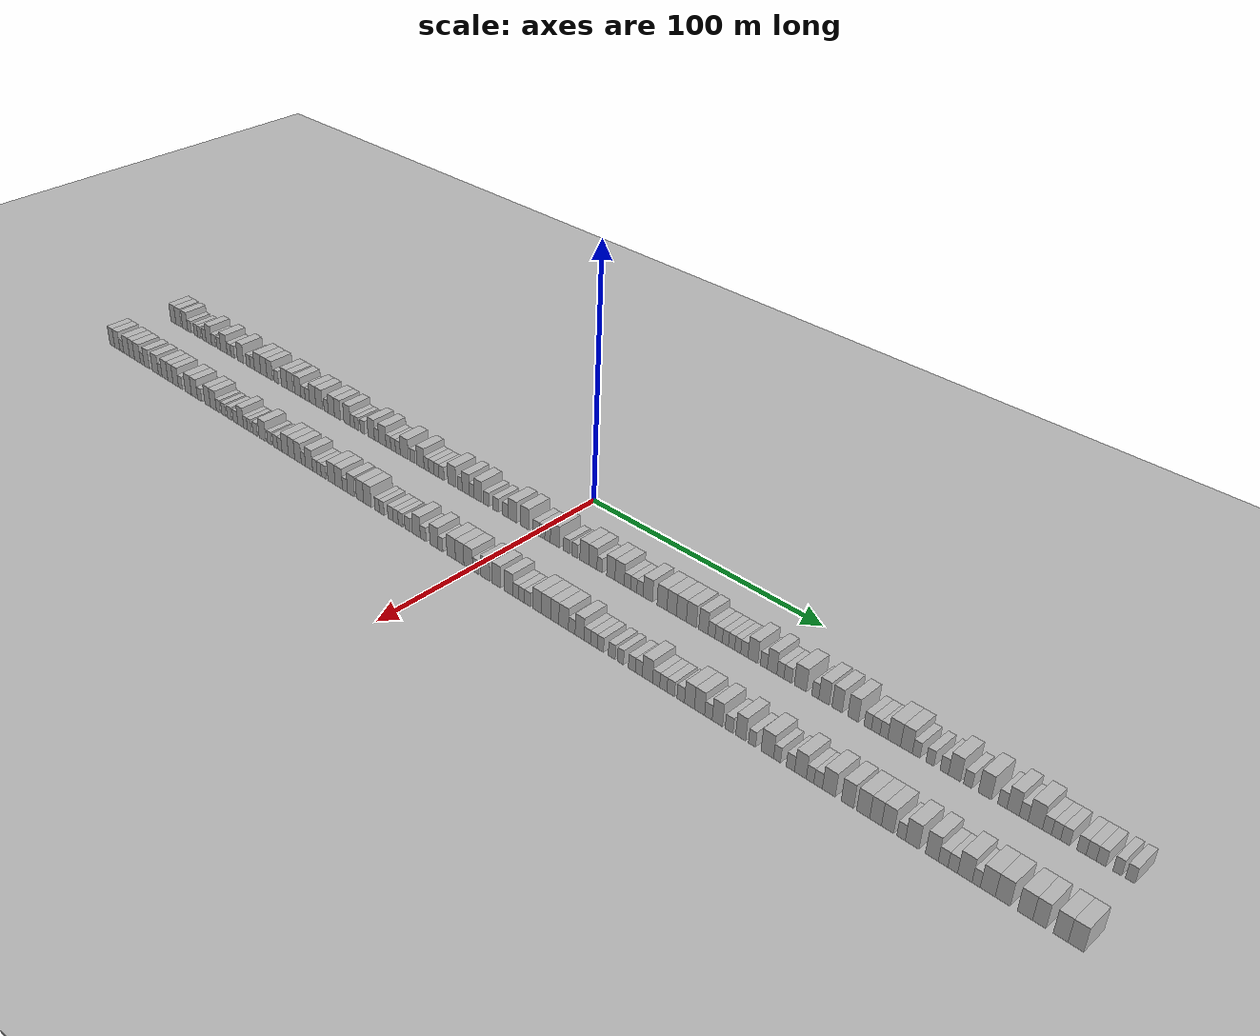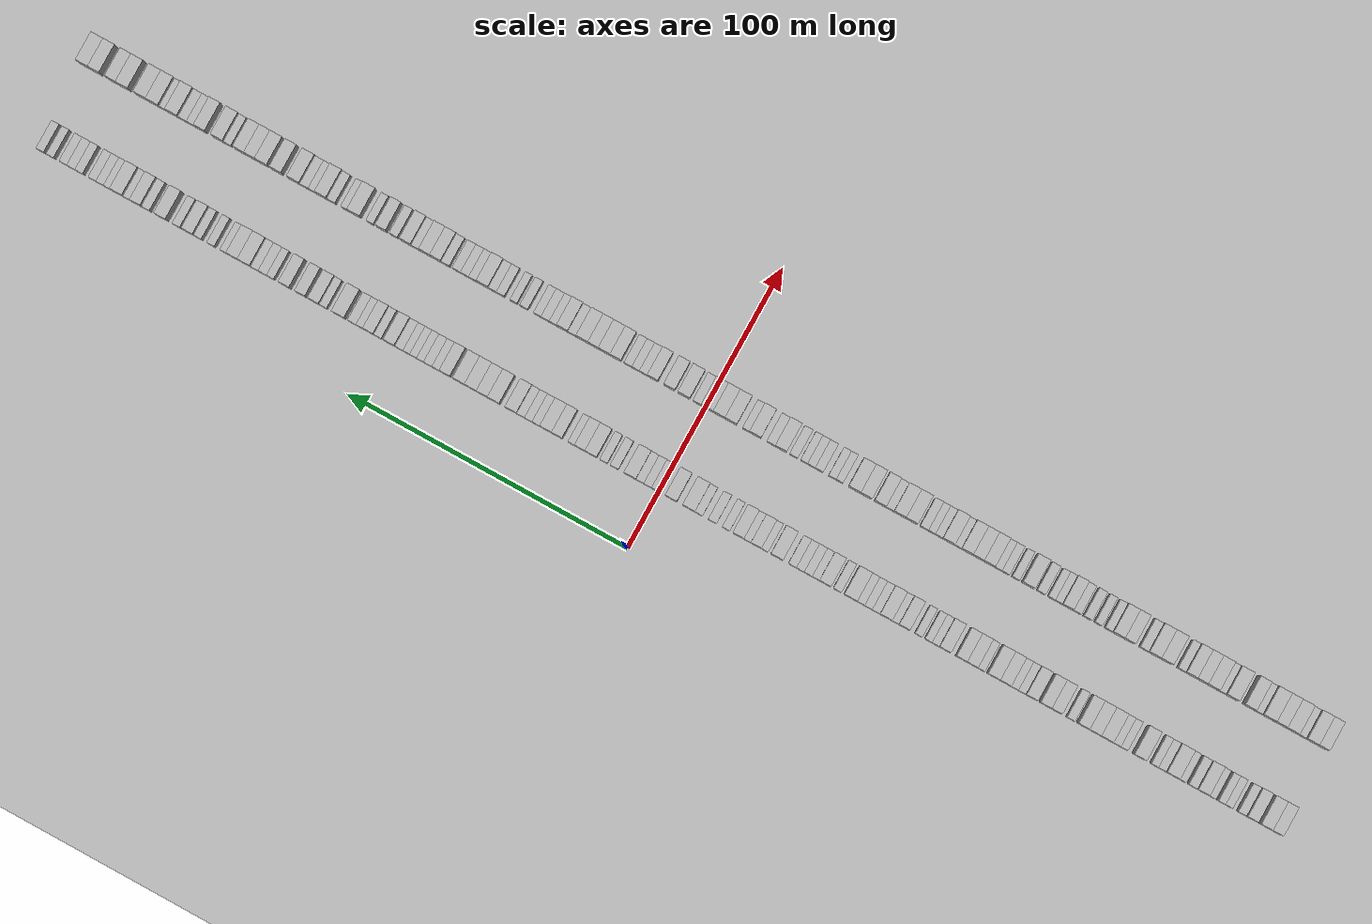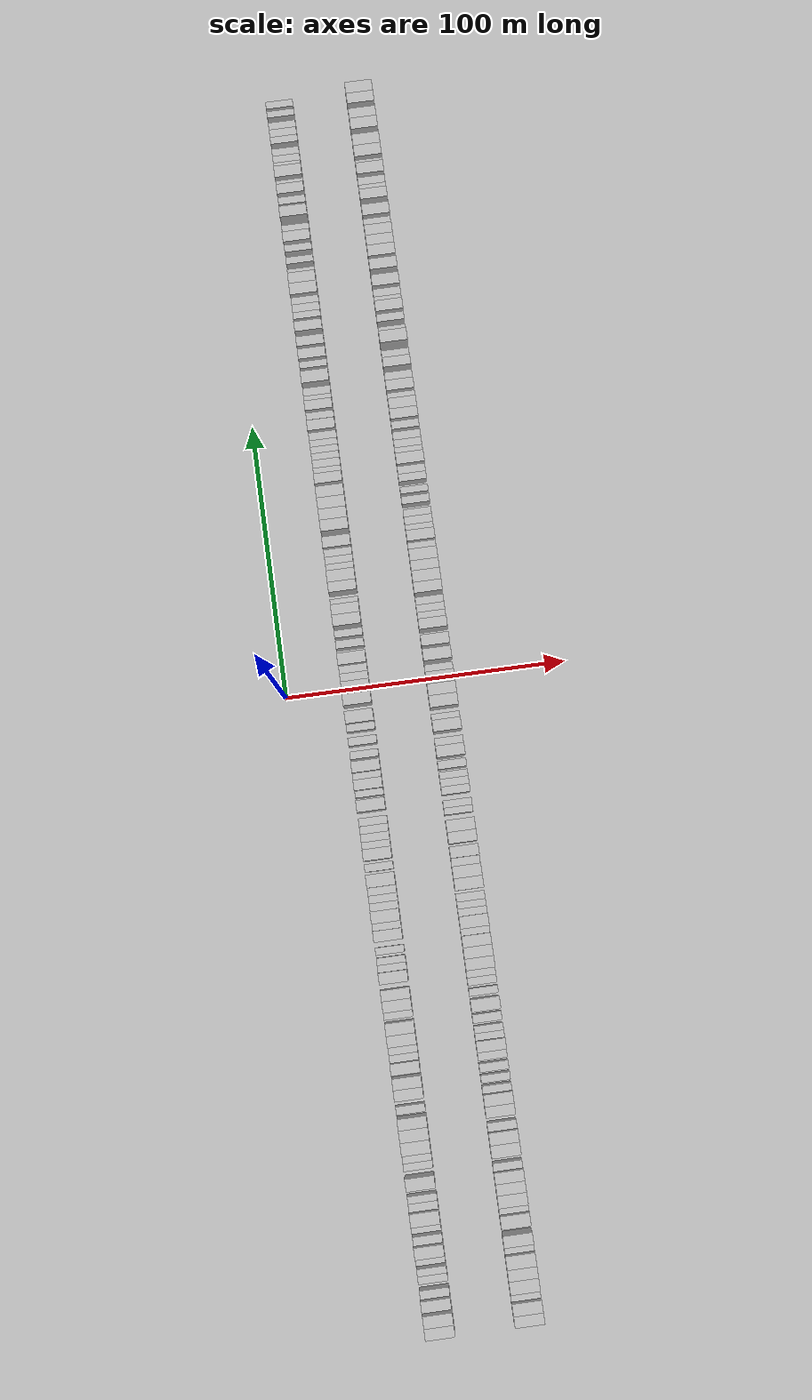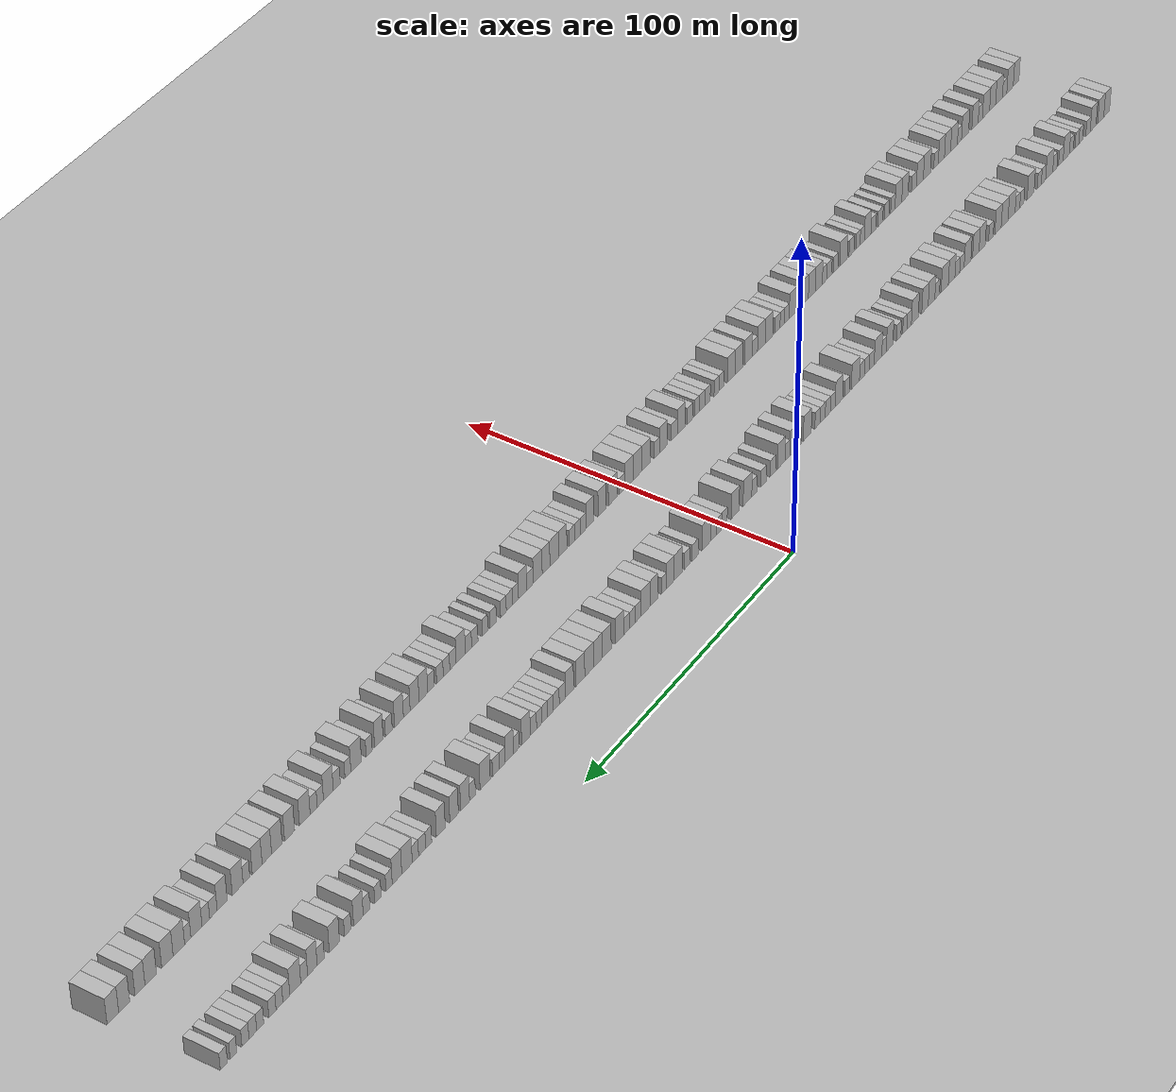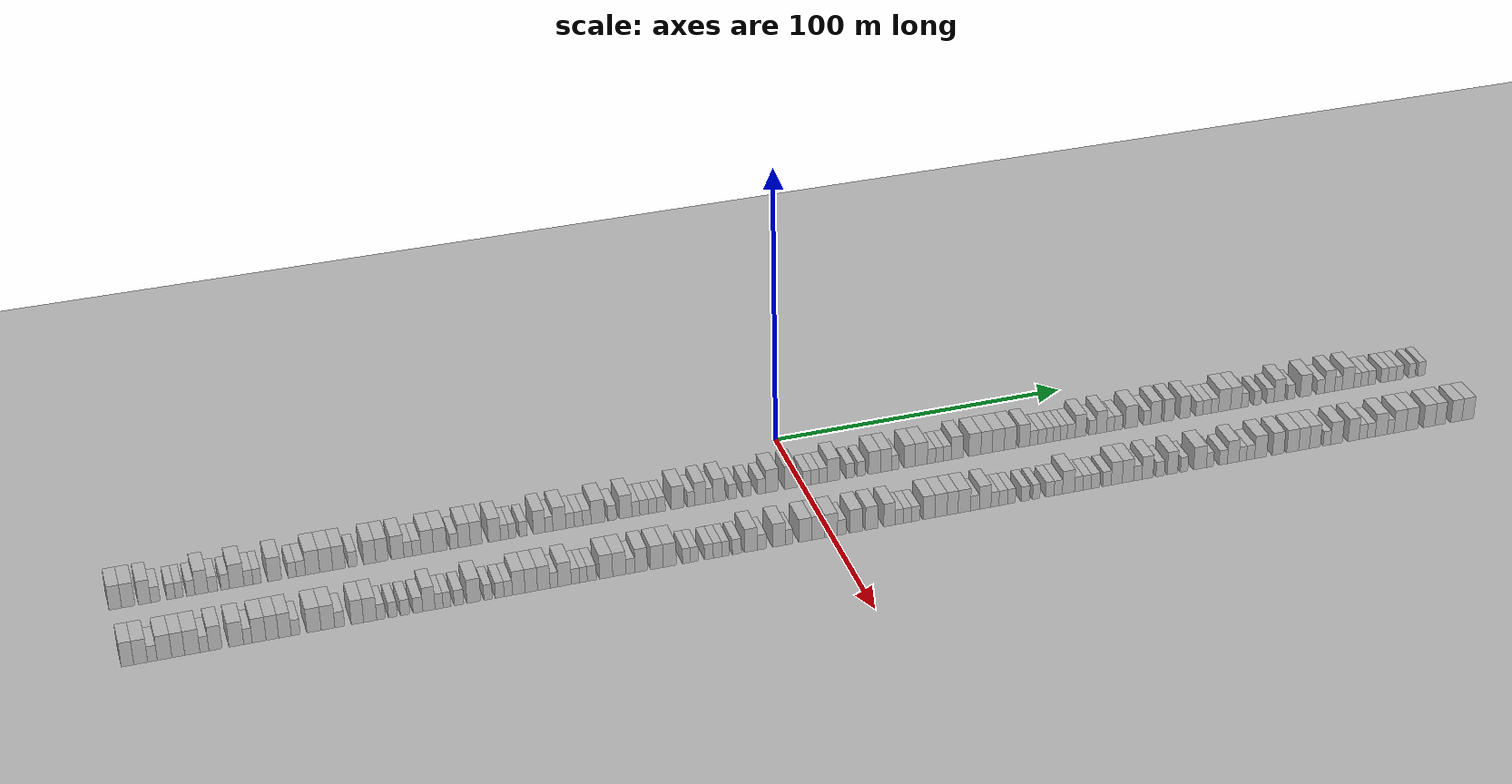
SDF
<?xml version="1.0" encoding="utf-8"?>

<sdf version="1.6">

   <world name="default">

      <gui fullscreen="0">

         <camera name="user_camera">

            <pose>-15 0 4.57585 0 0 0</pose>

            <view_controller>orbit</view_controller>

         </camera>

      </gui>

      <scene>

         <sky>

           <clouds>

             <speed>12</speed>

           </clouds>

         </sky>

         <ambient>0.4 0.4 0.4 1</ambient>

         <background>0.7 0.7 0.7 1</background>

         <shadows>1</shadows>

      </scene>

      <gravity>0 0 -9.8066</gravity>

      <magnetic_field>6e-06 2.3e-05 -4.2e-05</magnetic_field>

      <physics default="0" name="default_physics" type="ode">

         <ode>

            <solver>

               <type>quick</type>

               <iters>10</iters>

               <sor>1.0</sor>

               <use_dynamic_moi_rescaling>0</use_dynamic_moi_rescaling>

            </solver>

            <constraints>

               <cfm>0</cfm>

               <erp>0.2</erp>

               <contact_max_correcting_vel>100</contact_max_correcting_vel>

               <contact_surface_layer>0.001</contact_surface_layer>

            </constraints>

         </ode>

         <max_step_size>0.004</max_step_size>

         <real_time_factor>1</real_time_factor>

         <real_time_update_rate>250</real_time_update_rate>

      </physics>

      <light name="sun" type="directional">

         <cast_shadows>1</cast_shadows>

         <pose>0 0 10 0 0 0</pose>

         <diffuse>0.8 0.8 0.8 1</diffuse>

         <specular>0.2 0.2 0.2 1</specular>

         <attenuation>

            <range>1000</range>

            <constant>0.9</constant>

            <linear>0.01</linear>

            <quadratic>0.001</quadratic>

         </attenuation>

         <direction>-0.5 0.1 -0.9</direction>

      </light>

      <include>

         <name>ground_plane_1</name>

         <uri>model://HANNAS_ground_plane</uri>

         <pose>0 0 0  0 0 0</pose>

      </include>

      <include>

         <name>ground_plane_2</name>

         <uri>model://HANNAS_ground_plane</uri>

         <pose>100 0 0  0 0 0</pose>

      </include>

      <model name="building_1">

         <static>1</static>

         <pose frame="">25.0000 -218.1177 0 0.000000 0.000000 0.000000</pose>

         <link name="link">

            <pose frame="">0 0 4.50 0 0 0</pose>

            <collision name="collision">

               <geometry>

                  <box>

                     <size>10.0000 3.7646 9.0000</size>

                  </box>

               </geometry>

               <max_contacts>10</max_contacts>

               <surface>

                  <contact>

                     <ode/>

                  </contact>

                  <bounce/>

                  <friction>

                     <torsional>

                        <ode/>

                     </torsional>

                     <ode/>

                  </friction>

               </surface>

            </collision>

            <visual name="visual">

               <cast_shadows>0</cast_shadows>

               <geometry>

                  <box>

                     <size>10.0000 3.7646 9.0000</size>

                  </box>

               </geometry>

               <material>

                  <script>

                     <uri>model://HANNAS_wall/materials/scripts</uri>

                     <uri>model://HANNAS_wall/materials/textures</uri>

                     <name>vrc/HANNAS_wall</name>

                  </script>

               </material>

            </visual>

            <self_collide>0</self_collide>

            <enable_wind>0</enable_wind>

            <kinematic>0</kinematic>

         </link>

      </model>

      <model name="building_2">

         <static>1</static>

         <pose frame="">25.0000 -214.2348 0 0.000000 0.000000 0.000000</pose>

         <link name="link">

            <pose frame="">0 0 4.50 0 0 0</pose>

            <collision name="collision">

               <geometry>

                  <box>

                     <size>10.0000 4.0012 9.0000</size>

                  </box>

               </geometry>

               <max_contacts>10</max_contacts>

               <surface>

                  <contact>

                     <ode/>

                  </contact>

                  <bounce/>

                  <friction>

                     <torsional>

                        <ode/>

                     </torsional>

                     <ode/>

                  </friction>

               </surface>

            </collision>

            <visual name="visual">

               <cast_shadows>0</cast_shadows>

               <geometry>

                  <box>

                     <size>10.0000 4.0012 9.0000</size>

                  </box>

               </geometry>

               <material>

                  <script>

                     <uri>model://HANNAS_wall/materials/scripts</uri>

                     <uri>model://HANNAS_wall/materials/textures</uri>

                     <name>vrc/HANNAS_wall</name>

                  </script>

               </material>

            </visual>

            <self_collide>0</self_collide>

            <enable_wind>0</enable_wind>

            <kinematic>0</kinematic>

         </link>

      </model>

      <model name="building_3">

         <static>1</static>

         <pose frame="">25.0000 -209.3623 0 0.000000 0.000000 0.000000</pose>

         <link name="link">

            <pose frame="">0 0 4.50 0 0 0</pose>

            <collision name="collision">

               <geometry>

                  <box>

                     <size>10.0000 3.7438 9.0000</size>

                  </box>

               </geometry>

               <max_contacts>10</max_contacts>

               <surface>

                  <contact>

                     <ode/>

                  </contact>

                  <bounce/>

                  <friction>

                     <torsional>

                        <ode/>

                     </torsional>

                     <ode/>

                  </friction>

               </surface>

            </collision>

            <visual name="visual">

               <cast_shadows>0</cast_shadows>

               <geometry>

                  <box>

                     <size>10.0000 3.7438 9.0000</size>

                  </box>

               </geometry>

               <material>

                  <script>

                     <uri>model://HANNAS_wall/materials/scripts</uri>

                     <uri>model://HANNAS_wall/materials/textures</uri>

                     <name>vrc/HANNAS_wall</name>

                  </script>

               </material>

            </visual>

            <self_collide>0</self_collide>

            <enable_wind>0</enable_wind>

            <kinematic>0</kinematic>

         </link>

      </model>

      <model name="building_4">

         <static>1</static>

         <pose frame="">25.0000 -206.0749 0 0.000000 0.000000 0.000000</pose>

         <link name="link">

            <pose frame="">0 0 3.00 0 0 0</pose>

            <collision name="collision">

               <geometry>

                  <box>

                     <size>10.0000 2.8311 6.0000</size>

                  </box>

               </geometry>

               <max_contacts>10</max_contacts>

               <surface>

                  <contact>

                     <ode/>

                  </contact>

                  <bounce/>

                  <friction>

                     <torsional>

                        <ode/>

                     </torsional>

                     <ode/>

                  </friction>

               </surface>

            </collision>

            <visual name="visual">

               <cast_shadows>0</cast_shadows>

               <geometry>

                  <box>

                     <size>10.0000 2.8311 6.0000</size>

                  </box>

               </geometry>

               <material>

                  <script>

                     <uri>model://HANNAS_wall/materials/scripts</uri>

                     <uri>model://HANNAS_wall/materials/textures</uri>

                     <name>vrc/HANNAS_wall</name>

                  </script>

               </material>

            </visual>

            <self_collide>0</self_collide>

            <enable_wind>0</enable_wind>

            <kinematic>0</kinematic>

         </link>

      </model>

      <model name="building_5">

         <static>1</static>

         <pose frame="">25.0000 -201.3900 0 0.000000 0.000000 0.000000</pose>

         <link name="link">

            <pose frame="">0 0 3.00 0 0 0</pose>

            <collision name="collision">

               <geometry>

                  <box>

                     <size>10.0000 2.5387 6.0000</size>

                  </box>

               </geometry>

               <max_contacts>10</max_contacts>

               <surface>

                  <contact>

                     <ode/>

                  </contact>

                  <bounce/>

                  <friction>

                     <torsional>

                        <ode/>

                     </torsional>

                     <ode/>

                  </friction>

               </surface>

            </collision>

            <visual name="visual">

               <cast_shadows>0</cast_shadows>

               <geometry>

                  <box>

                     <size>10.0000 2.5387 6.0000</size>

                  </box>

               </geometry>

               <material>

                  <script>

                     <uri>model://HANNAS_wall/materials/scripts</uri>

                     <uri>model://HANNAS_wall/materials/textures</uri>

                     <name>vrc/HANNAS_wall</name>

                  </script>

               </material>

            </visual>

            <self_collide>0</self_collide>

            <enable_wind>0</enable_wind>

            <kinematic>0</kinematic>

         </link>

      </model>

      <model name="building_6">

         <static>1</static>

         <pose frame="">25.0000 -198.9170 0 0.000000 0.000000 0.000000</pose>

         <link name="link">

            <pose frame="">0 0 3.00 0 0 0</pose>

            <collision name="collision">

               <geometry>

                  <box>

                     <size>10.0000 2.4074 6.0000</size>

                  </box>

               </geometry>

               <max_contacts>10</max_contacts>

               <surface>

                  <contact>

                     <ode/>

                  </contact>

                  <bounce/>

                  <friction>

                     <torsional>

                        <ode/>

                     </torsional>

                     <ode/>

                  </friction>

               </surface>

            </collision>

            <visual name="visual">

               <cast_shadows>0</cast_shadows>

               <geometry>

                  <box>

                     <size>10.0000 2.4074 6.0000</size>

                  </box>

               </geometry>

               <material>

                  <script>

                     <uri>model://HANNAS_wall/materials/scripts</uri>

                     <uri>model://HANNAS_wall/materials/textures</uri>

                     <name>vrc/HANNAS_wall</name>

                  </script>

               </material>

            </visual>

            <self_collide>0</self_collide>

            <enable_wind>0</enable_wind>

            <kinematic>0</kinematic>

         </link>

      </model>

      <model name="building_7">

         <static>1</static>

         <pose frame="">25.0000 -195.4330 0 0.000000 0.000000 0.000000</pose>

         <link name="link">

            <pose frame="">0 0 3.00 0 0 0</pose>

            <collision name="collision">

               <geometry>

                  <box>

                     <size>10.0000 2.5606 6.0000</size>

                  </box>

               </geometry>

               <max_contacts>10</max_contacts>

               <surface>

                  <contact>

                     <ode/>

                  </contact>

                  <bounce/>

                  <friction>

                     <torsional>

                        <ode/>

                     </torsional>

                     <ode/>

                  </friction>

               </surface>

            </collision>

            <visual name="visual">

               <cast_shadows>0</cast_shadows>

               <geometry>

                  <box>

                     <size>10.0000 2.5606 6.0000</size>

                  </box>

               </geometry>

               <material>

                  <script>

                     <uri>model://HANNAS_wall/materials/scripts</uri>

                     <uri>model://HANNAS_wall/materials/textures</uri>

                     <name>vrc/HANNAS_wall</name>

                  </script>

               </material>

            </visual>

            <self_collide>0</self_collide>

            <enable_wind>0</enable_wind>

            <kinematic>0</kinematic>

         </link>

      </model>

      <model name="building_8">

         <static>1</static>

         <pose frame="">25.0000 -192.1857 0 0.000000 0.000000 0.000000</pose>

         <link name="link">

            <pose frame="">0 0 4.50 0 0 0</pose>

            <collision name="collision">

               <geometry>

                  <box>

                     <size>10.0000 3.9340 9.0000</size>

                  </box>

               </geometry>

               <max_contacts>10</max_contacts>

               <surface>

                  <contact>

                     <ode/>

                  </contact>

                  <bounce/>

                  <friction>

                     <torsional>

                        <ode/>

                     </torsional>

                     <ode/>

                  </friction>

               </surface>

            </collision>

            <visual name="visual">

               <cast_shadows>0</cast_shadows>

               <geometry>

                  <box>

                     <size>10.0000 3.9340 9.0000</size>

                  </box>

               </geometry>

               <material>

                  <script>

                     <uri>model://HANNAS_wall/materials/scripts</uri>

                     <uri>model://HANNAS_wall/materials/textures</uri>

                     <name>vrc/HANNAS_wall</name>

                  </script>

               </material>

            </visual>

            <self_collide>0</self_collide>

            <enable_wind>0</enable_wind>

            <kinematic>0</kinematic>

         </link>

      </model>

      <model name="building_9">

         <static>1</static>

         <pose frame="">25.0000 -188.7508 0 0.000000 0.000000 0.000000</pose>

         <link name="link">

            <pose frame="">0 0 3.00 0 0 0</pose>

            <collision name="collision">

               <geometry>

                  <box>

                     <size>10.0000 2.9357 6.0000</size>

                  </box>

               </geometry>

               <max_contacts>10</max_contacts>

               <surface>

                  <contact>

                     <ode/>

                  </contact>

                  <bounce/>

                  <friction>

                     <torsional>

                        <ode/>

                     </torsional>

                     <ode/>

                  </friction>

               </surface>

            </collision>

            <visual name="visual">

               <cast_shadows>0</cast_shadows>

               <geometry>

                  <box>

                     <size>10.0000 2.9357 6.0000</size>

                  </box>

               </geometry>

               <material>

                  <script>

                     <uri>model://HANNAS_wall/materials/scripts</uri>

                     <uri>model://HANNAS_wall/materials/textures</uri>

                     <name>vrc/HANNAS_wall</name>

                  </script>

               </material>

            </visual>

            <self_collide>0</self_collide>

            <enable_wind>0</enable_wind>

            <kinematic>0</kinematic>

         </link>

      </model>

      <model name="building_10">

         <static>1</static>

         <pose frame="">25.0000 -184.9936 0 0.000000 0.000000 0.000000</pose>

         <link name="link">

            <pose frame="">0 0 3.00 0 0 0</pose>

            <collision name="collision">

               <geometry>

                  <box>

                     <size>10.0000 2.5789 6.0000</size>

                  </box>

               </geometry>

               <max_contacts>10</max_contacts>

               <surface>

                  <contact>

                     <ode/>

                  </contact>

                  <bounce/>

                  <friction>

                     <torsional>

                        <ode/>

                     </torsional>

                     <ode/>

                  </friction>

               </surface>

            </collision>

            <visual name="visual">

               <cast_shadows>0</cast_shadows>

               <geometry>

                  <box>

                     <size>10.0000 2.5789 6.0000</size>

                  </box>

               </geometry>

               <material>

                  <script>

                     <uri>model://HANNAS_wall/materials/scripts</uri>

                     <uri>model://HANNAS_wall/materials/textures</uri>

                     <name>vrc/HANNAS_wall</name>

                  </script>

               </material>

            </visual>

            <self_collide>0</self_collide>

            <enable_wind>0</enable_wind>

            <kinematic>0</kinematic>

         </link>

      </model>

      <model name="building_11">

         <static>1</static>

         <pose frame="">25.0000 -181.4808 0 0.000000 0.000000 0.000000</pose>

         <link name="link">

            <pose frame="">0 0 4.50 0 0 0</pose>

            <collision name="collision">

               <geometry>

                  <box>

                     <size>10.0000 4.4466 9.0000</size>

                  </box>

               </geometry>

               <max_contacts>10</max_contacts>

               <surface>

                  <contact>

                     <ode/>

                  </contact>

                  <bounce/>

                  <friction>

                     <torsional>

                        <ode/>

                     </torsional>

                     <ode/>

                  </friction>

               </surface>

            </collision>

            <visual name="visual">

               <cast_shadows>0</cast_shadows>

               <geometry>

                  <box>

                     <size>10.0000 4.4466 9.0000</size>

                  </box>

               </geometry>

               <material>

                  <script>

                     <uri>model://HANNAS_wall/materials/scripts</uri>

                     <uri>model://HANNAS_wall/materials/textures</uri>

                     <name>vrc/HANNAS_wall</name>

                  </script>

               </material>

            </visual>

            <self_collide>0</self_collide>

            <enable_wind>0</enable_wind>

            <kinematic>0</kinematic>

         </link>

      </model>

      <model name="building_12">

         <static>1</static>

         <pose frame="">25.0000 -177.8910 0 0.000000 0.000000 0.000000</pose>

         <link name="link">

            <pose frame="">0 0 3.00 0 0 0</pose>

            <collision name="collision">

               <geometry>

                  <box>

                     <size>10.0000 2.7331 6.0000</size>

                  </box>

               </geometry>

               <max_contacts>10</max_contacts>

               <surface>

                  <contact>

                     <ode/>

                  </contact>

                  <bounce/>

                  <friction>

                     <torsional>

                        <ode/>

                     </torsional>

                     <ode/>

                  </friction>

               </surface>

            </collision>

            <visual name="visual">

               <cast_shadows>0</cast_shadows>

               <geometry>

                  <box>

                     <size>10.0000 2.7331 6.0000</size>

                  </box>

               </geometry>

               <material>

                  <script>

                     <uri>model://HANNAS_wall/materials/scripts</uri>

                     <uri>model://HANNAS_wall/materials/textures</uri>

                     <name>vrc/HANNAS_wall</name>

                  </script>

               </material>

            </visual>

            <self_collide>0</self_collide>

            <enable_wind>0</enable_wind>

            <kinematic>0</kinematic>

         </link>

      </model>

      <model name="building_13">

         <static>1</static>

         <pose frame="">25.0000 -175.2878 0 0.000000 0.000000 0.000000</pose>

         <link name="link">

            <pose frame="">0 0 3.00 0 0 0</pose>

            <collision name="collision">

               <geometry>

                  <box>

                     <size>10.0000 2.4733 6.0000</size>

                  </box>

               </geometry>

               <max_contacts>10</max_contacts>

               <surface>

                  <contact>

                     <ode/>

                  </contact>

                  <bounce/>

                  <friction>

                     <torsional>

                        <ode/>

                     </torsional>

                     <ode/>

                  </friction>

               </surface>

            </collision>

            <visual name="visual">

               <cast_shadows>0</cast_shadows>

               <geometry>

                  <box>

                     <size>10.0000 2.4733 6.0000</size>

                  </box>

               </geometry>

               <material>

                  <script>

                     <uri>model://HANNAS_wall/materials/scripts</uri>

                     <uri>model://HANNAS_wall/materials/textures</uri>

                     <name>vrc/HANNAS_wall</name>

                  </script>

               </material>

            </visual>

            <self_collide>0</self_collide>

            <enable_wind>0</enable_wind>

            <kinematic>0</kinematic>

         </link>

      </model>

      <model name="building_14">

         <static>1</static>

         <pose frame="">25.0000 -169.9233 0 0.000000 0.000000 0.000000</pose>

         <link name="link">

            <pose frame="">0 0 4.50 0 0 0</pose>

            <collision name="collision">

               <geometry>

                  <box>

                     <size>10.0000 4.2557 9.0000</size>

                  </box>

               </geometry>

               <max_contacts>10</max_contacts>

               <surface>

                  <contact>

                     <ode/>

                  </contact>

                  <bounce/>

                  <friction>

                     <torsional>

                        <ode/>

                     </torsional>

                     <ode/>

                  </friction>

               </surface>

            </collision>

            <visual name="visual">

               <cast_shadows>0</cast_shadows>

               <geometry>

                  <box>

                     <size>10.0000 4.2557 9.0000</size>

                  </box>

               </geometry>

               <material>

                  <script>

                     <uri>model://HANNAS_wall/materials/scripts</uri>

                     <uri>model://HANNAS_wall/materials/textures</uri>

                     <name>vrc/HANNAS_wall</name>

                  </script>

               </material>

            </visual>

            <self_collide>0</self_collide>

            <enable_wind>0</enable_wind>

            <kinematic>0</kinematic>

         </link>

      </model>

      <model name="building_15">

         <static>1</static>

         <pose frame="">25.0000 -164.5388 0 0.000000 0.000000 0.000000</pose>

         <link name="link">

            <pose frame="">0 0 3.00 0 0 0</pose>

            <collision name="collision">

               <geometry>

                  <box>

                     <size>10.0000 2.5134 6.0000</size>

                  </box>

               </geometry>

               <max_contacts>10</max_contacts>

               <surface>

                  <contact>

                     <ode/>

                  </contact>

                  <bounce/>

                  <friction>

                     <torsional>

                        <ode/>

                     </torsional>

                     <ode/>

                  </friction>

               </surface>

            </collision>

            <visual name="visual">

               <cast_shadows>0</cast_shadows>

               <geometry>

                  <box>

                     <size>10.0000 2.5134 6.0000</size>

                  </box>

               </geometry>

               <material>

                  <script>

                     <uri>model://HANNAS_wall/materials/scripts</uri>

                     <uri>model://HANNAS_wall/materials/textures</uri>

                     <name>vrc/HANNAS_wall</name>

                  </script>

               </material>

            </visual>

            <self_collide>0</self_collide>

            <enable_wind>0</enable_wind>

            <kinematic>0</kinematic>

         </link>

      </model>

      <model name="building_16">

         <static>1</static>

         <pose frame="">25.0000 -161.8554 0 0.000000 0.000000 0.000000</pose>

         <link name="link">

            <pose frame="">0 0 3.00 0 0 0</pose>

            <collision name="collision">

               <geometry>

                  <box>

                     <size>10.0000 2.8534 6.0000</size>

                  </box>

               </geometry>

               <max_contacts>10</max_contacts>

               <surface>

                  <contact>

                     <ode/>

                  </contact>

                  <bounce/>

                  <friction>

                     <torsional>

                        <ode/>

                     </torsional>

                     <ode/>

                  </friction>

               </surface>

            </collision>

            <visual name="visual">

               <cast_shadows>0</cast_shadows>

               <geometry>

                  <box>

                     <size>10.0000 2.8534 6.0000</size>

                  </box>

               </geometry>

               <material>

                  <script>

                     <uri>model://HANNAS_wall/materials/scripts</uri>

                     <uri>model://HANNAS_wall/materials/textures</uri>

                     <name>vrc/HANNAS_wall</name>

                  </script>

               </material>

            </visual>

            <self_collide>0</self_collide>

            <enable_wind>0</enable_wind>

            <kinematic>0</kinematic>

         </link>

      </model>

      <model name="building_17">

         <static>1</static>

         <pose frame="">25.0000 -158.2648 0 0.000000 0.000000 0.000000</pose>

         <link name="link">

            <pose frame="">0 0 4.50 0 0 0</pose>

            <collision name="collision">

               <geometry>

                  <box>

                     <size>10.0000 4.3278 9.0000</size>

                  </box>

               </geometry>

               <max_contacts>10</max_contacts>

               <surface>

                  <contact>

                     <ode/>

                  </contact>

                  <bounce/>

                  <friction>

                     <torsional>

                        <ode/>

                     </torsional>

                     <ode/>

                  </friction>

               </surface>

            </collision>

            <visual name="visual">

               <cast_shadows>0</cast_shadows>

               <geometry>

                  <box>

                     <size>10.0000 4.3278 9.0000</size>

                  </box>

               </geometry>

               <material>

                  <script>

                     <uri>model://HANNAS_wall/materials/scripts</uri>

                     <uri>model://HANNAS_wall/materials/textures</uri>

                     <name>vrc/HANNAS_wall</name>

                  </script>

               </material>

            </visual>

            <self_collide>0</self_collide>

            <enable_wind>0</enable_wind>

            <kinematic>0</kinematic>

         </link>

      </model>

      <model name="building_18">

         <static>1</static>

         <pose frame="">25.0000 -154.0507 0 0.000000 0.000000 0.000000</pose>

         <link name="link">

            <pose frame="">0 0 4.50 0 0 0</pose>

            <collision name="collision">

               <geometry>

                  <box>

                     <size>10.0000 4.1003 9.0000</size>

                  </box>

               </geometry>

               <max_contacts>10</max_contacts>

               <surface>

                  <contact>

                     <ode/>

                  </contact>

                  <bounce/>

                  <friction>

                     <torsional>

                        <ode/>

                     </torsional>

                     <ode/>

                  </friction>

               </surface>

            </collision>

            <visual name="visual">

               <cast_shadows>0</cast_shadows>

               <geometry>

                  <box>

                     <size>10.0000 4.1003 9.0000</size>

                  </box>

               </geometry>

               <material>

                  <script>

                     <uri>model://HANNAS_wall/materials/scripts</uri>

                     <uri>model://HANNAS_wall/materials/textures</uri>

                     <name>vrc/HANNAS_wall</name>

                  </script>

               </material>

            </visual>

            <self_collide>0</self_collide>

            <enable_wind>0</enable_wind>

            <kinematic>0</kinematic>

         </link>

      </model>

      <model name="building_19">

         <static>1</static>

         <pose frame="">25.0000 -150.0863 0 0.000000 0.000000 0.000000</pose>

         <link name="link">

            <pose frame="">0 0 4.50 0 0 0</pose>

            <collision name="collision">

               <geometry>

                  <box>

                     <size>10.0000 3.8285 9.0000</size>

                  </box>

               </geometry>

               <max_contacts>10</max_contacts>

               <surface>

                  <contact>

                     <ode/>

                  </contact>

                  <bounce/>

                  <friction>

                     <torsional>

                        <ode/>

                     </torsional>

                     <ode/>

                  </friction>

               </surface>

            </collision>

            <visual name="visual">

               <cast_shadows>0</cast_shadows>

               <geometry>

                  <box>

                     <size>10.0000 3.8285 9.0000</size>

                  </box>

               </geometry>

               <material>

                  <script>

                     <uri>model://HANNAS_wall/materials/scripts</uri>

                     <uri>model://HANNAS_wall/materials/textures</uri>

                     <name>vrc/HANNAS_wall</name>

                  </script>

               </material>

            </visual>

            <self_collide>0</self_collide>

            <enable_wind>0</enable_wind>

            <kinematic>0</kinematic>

         </link>

      </model>

      <model name="building_20">

         <static>1</static>

         <pose frame="">25.0000 -145.7861 0 0.000000 0.000000 0.000000</pose>

         <link name="link">

            <pose frame="">0 0 3.00 0 0 0</pose>

            <collision name="collision">

               <geometry>

                  <box>

                     <size>10.0000 2.7718 6.0000</size>

                  </box>

               </geometry>

               <max_contacts>10</max_contacts>

               <surface>

                  <contact>

                     <ode/>

                  </contact>

                  <bounce/>

                  <friction>

                     <torsional>

                        <ode/>

                     </torsional>

                     <ode/>

                  </friction>

               </surface>

            </collision>

            <visual name="visual">

               <cast_shadows>0</cast_shadows>

               <geometry>

                  <box>

                     <size>10.0000 2.7718 6.0000</size>

                  </box>

               </geometry>

               <material>

                  <script>

                     <uri>model://HANNAS_wall/materials/scripts</uri>

                     <uri>model://HANNAS_wall/materials/textures</uri>

                     <name>vrc/HANNAS_wall</name>

                  </script>

               </material>

            </visual>

            <self_collide>0</self_collide>

            <enable_wind>0</enable_wind>

            <kinematic>0</kinematic>

         </link>

      </model>

      <model name="building_21">

         <static>1</static>

         <pose frame="">25.0000 -140.5354 0 0.000000 0.000000 0.000000</pose>

         <link name="link">

            <pose frame="">0 0 4.50 0 0 0</pose>

            <collision name="collision">

               <geometry>

                  <box>

                     <size>10.0000 3.7296 9.0000</size>

                  </box>

               </geometry>

               <max_contacts>10</max_contacts>

               <surface>

                  <contact>

                     <ode/>

                  </contact>

                  <bounce/>

                  <friction>

                     <torsional>

                        <ode/>

                     </torsional>

                     <ode/>

                  </friction>

               </surface>

            </collision>

            <visual name="visual">

               <cast_shadows>0</cast_shadows>

               <geometry>

                  <box>

                     <size>10.0000 3.7296 9.0000</size>

                  </box>

               </geometry>

               <material>

                  <script>

                     <uri>model://HANNAS_wall/materials/scripts</uri>

                     <uri>model://HANNAS_wall/materials/textures</uri>

                     <name>vrc/HANNAS_wall</name>

                  </script>

               </material>

            </visual>

            <self_collide>0</self_collide>

            <enable_wind>0</enable_wind>

            <kinematic>0</kinematic>

         </link>

      </model>

      <model name="building_22">

         <static>1</static>

         <pose frame="">25.0000 -136.7452 0 0.000000 0.000000 0.000000</pose>

         <link name="link">

            <pose frame="">0 0 4.50 0 0 0</pose>

            <collision name="collision">

               <geometry>

                  <box>

                     <size>10.0000 3.8507 9.0000</size>

                  </box>

               </geometry>

               <max_contacts>10</max_contacts>

               <surface>

                  <contact>

                     <ode/>

                  </contact>

                  <bounce/>

                  <friction>

                     <torsional>

                        <ode/>

                     </torsional>

                     <ode/>

                  </friction>

               </surface>

            </collision>

            <visual name="visual">

               <cast_shadows>0</cast_shadows>

               <geometry>

                  <box>

                     <size>10.0000 3.8507 9.0000</size>

                  </box>

               </geometry>

               <material>

                  <script>

                     <uri>model://HANNAS_wall/materials/scripts</uri>

                     <uri>model://HANNAS_wall/materials/textures</uri>

                     <name>vrc/HANNAS_wall</name>

                  </script>

               </material>

            </visual>

            <self_collide>0</self_collide>

            <enable_wind>0</enable_wind>

            <kinematic>0</kinematic>

         </link>

      </model>

      <model name="building_23">

         <static>1</static>

         <pose frame="">25.0000 -131.8363 0 0.000000 0.000000 0.000000</pose>

         <link name="link">

            <pose frame="">0 0 4.50 0 0 0</pose>

            <collision name="collision">

               <geometry>

                  <box>

                     <size>10.0000 3.9670 9.0000</size>

                  </box>

               </geometry>

               <max_contacts>10</max_contacts>

               <surface>

                  <contact>

                     <ode/>

                  </contact>

                  <bounce/>

                  <friction>

                     <torsional>

                        <ode/>

                     </torsional>

                     <ode/>

                  </friction>

               </surface>

            </collision>

            <visual name="visual">

               <cast_shadows>0</cast_shadows>

               <geometry>

                  <box>

                     <size>10.0000 3.9670 9.0000</size>

                  </box>

               </geometry>

               <material>

                  <script>

                     <uri>model://HANNAS_wall/materials/scripts</uri>

                     <uri>model://HANNAS_wall/materials/textures</uri>

                     <name>vrc/HANNAS_wall</name>

                  </script>

               </material>

            </visual>

            <self_collide>0</self_collide>

            <enable_wind>0</enable_wind>

            <kinematic>0</kinematic>

         </link>

      </model>

      <model name="building_24">

         <static>1</static>

         <pose frame="">25.0000 -128.5348 0 0.000000 0.000000 0.000000</pose>

         <link name="link">

            <pose frame="">0 0 3.00 0 0 0</pose>

            <collision name="collision">

               <geometry>

                  <box>

                     <size>10.0000 2.6360 6.0000</size>

                  </box>

               </geometry>

               <max_contacts>10</max_contacts>

               <surface>

                  <contact>

                     <ode/>

                  </contact>

                  <bounce/>

                  <friction>

                     <torsional>

                        <ode/>

                     </torsional>

                     <ode/>

                  </friction>

               </surface>

            </collision>

            <visual name="visual">

               <cast_shadows>0</cast_shadows>

               <geometry>

                  <box>

                     <size>10.0000 2.6360 6.0000</size>

                  </box>

               </geometry>

               <material>

                  <script>

                     <uri>model://HANNAS_wall/materials/scripts</uri>

                     <uri>model://HANNAS_wall/materials/textures</uri>

                     <name>vrc/HANNAS_wall</name>

                  </script>

               </material>

            </visual>

            <self_collide>0</self_collide>

            <enable_wind>0</enable_wind>

            <kinematic>0</kinematic>

         </link>

      </model>

      <model name="building_25">

         <static>1</static>

         <pose frame="">25.0000 -125.8305 0 0.000000 0.000000 0.000000</pose>

         <link name="link">

            <pose frame="">0 0 3.00 0 0 0</pose>

            <collision name="collision">

               <geometry>

                  <box>

                     <size>10.0000 2.7727 6.0000</size>

                  </box>

               </geometry>

               <max_contacts>10</max_contacts>

               <surface>

                  <contact>

                     <ode/>

                  </contact>

                  <bounce/>

                  <friction>

                     <torsional>

                        <ode/>

                     </torsional>

                     <ode/>

                  </friction>

               </surface>

            </collision>

            <visual name="visual">

               <cast_shadows>0</cast_shadows>

               <geometry>

                  <box>

                     <size>10.0000 2.7727 6.0000</size>

                  </box>

               </geometry>

               <material>

                  <script>

                     <uri>model://HANNAS_wall/materials/scripts</uri>

                     <uri>model://HANNAS_wall/materials/textures</uri>

                     <name>vrc/HANNAS_wall</name>

                  </script>

               </material>

            </visual>

            <self_collide>0</self_collide>

            <enable_wind>0</enable_wind>

            <kinematic>0</kinematic>

         </link>

      </model>

      <model name="building_26">

         <static>1</static>

         <pose frame="">25.0000 -122.5052 0 0.000000 0.000000 0.000000</pose>

         <link name="link">

            <pose frame="">0 0 4.50 0 0 0</pose>

            <collision name="collision">

               <geometry>

                  <box>

                     <size>10.0000 3.8780 9.0000</size>

                  </box>

               </geometry>

               <max_contacts>10</max_contacts>

               <surface>

                  <contact>

                     <ode/>

                  </contact>

                  <bounce/>

                  <friction>

                     <torsional>

                        <ode/>

                     </torsional>

                     <ode/>

                  </friction>

               </surface>

            </collision>

            <visual name="visual">

               <cast_shadows>0</cast_shadows>

               <geometry>

                  <box>

                     <size>10.0000 3.8780 9.0000</size>

                  </box>

               </geometry>

               <material>

                  <script>

                     <uri>model://HANNAS_wall/materials/scripts</uri>

                     <uri>model://HANNAS_wall/materials/textures</uri>

                     <name>vrc/HANNAS_wall</name>

                  </script>

               </material>

            </visual>

            <self_collide>0</self_collide>

            <enable_wind>0</enable_wind>

            <kinematic>0</kinematic>

         </link>

      </model>

      <model name="building_27">

         <static>1</static>

         <pose frame="">25.0000 -118.4681 0 0.000000 0.000000 0.000000</pose>

         <link name="link">

            <pose frame="">0 0 4.50 0 0 0</pose>

            <collision name="collision">

               <geometry>

                  <box>

                     <size>10.0000 4.1962 9.0000</size>

                  </box>

               </geometry>

               <max_contacts>10</max_contacts>

               <surface>

                  <contact>

                     <ode/>

                  </contact>

                  <bounce/>

                  <friction>

                     <torsional>

                        <ode/>

                     </torsional>

                     <ode/>

                  </friction>

               </surface>

            </collision>

            <visual name="visual">

               <cast_shadows>0</cast_shadows>

               <geometry>

                  <box>

                     <size>10.0000 4.1962 9.0000</size>

                  </box>

               </geometry>

               <material>

                  <script>

                     <uri>model://HANNAS_wall/materials/scripts</uri>

                     <uri>model://HANNAS_wall/materials/textures</uri>

                     <name>vrc/HANNAS_wall</name>

                  </script>

               </material>

            </visual>

            <self_collide>0</self_collide>

            <enable_wind>0</enable_wind>

            <kinematic>0</kinematic>

         </link>

      </model>

      <model name="building_28">

         <static>1</static>

         <pose frame="">25.0000 -114.0590 0 0.000000 0.000000 0.000000</pose>

         <link name="link">

            <pose frame="">0 0 3.00 0 0 0</pose>

            <collision name="collision">

               <geometry>

                  <box>

                     <size>10.0000 2.6220 6.0000</size>

                  </box>

               </geometry>

               <max_contacts>10</max_contacts>

               <surface>

                  <contact>

                     <ode/>

                  </contact>

                  <bounce/>

                  <friction>

                     <torsional>

                        <ode/>

                     </torsional>

                     <ode/>

                  </friction>

               </surface>

            </collision>

            <visual name="visual">

               <cast_shadows>0</cast_shadows>

               <geometry>

                  <box>

                     <size>10.0000 2.6220 6.0000</size>

                  </box>

               </geometry>

               <material>

                  <script>

                     <uri>model://HANNAS_wall/materials/scripts</uri>

                     <uri>model://HANNAS_wall/materials/textures</uri>

                     <name>vrc/HANNAS_wall</name>

                  </script>

               </material>

            </visual>

            <self_collide>0</self_collide>

            <enable_wind>0</enable_wind>

            <kinematic>0</kinematic>

         </link>

      </model>

      <model name="building_29">

         <static>1</static>

         <pose frame="">25.0000 -110.8329 0 0.000000 0.000000 0.000000</pose>

         <link name="link">

            <pose frame="">0 0 4.50 0 0 0</pose>

            <collision name="collision">

               <geometry>

                  <box>

                     <size>10.0000 3.8302 9.0000</size>

                  </box>

               </geometry>

               <max_contacts>10</max_contacts>

               <surface>

                  <contact>

                     <ode/>

                  </contact>

                  <bounce/>

                  <friction>

                     <torsional>

                        <ode/>

                     </torsional>

                     <ode/>

                  </friction>

               </surface>

            </collision>

            <visual name="visual">

               <cast_shadows>0</cast_shadows>

               <geometry>

                  <box>

                     <size>10.0000 3.8302 9.0000</size>

                  </box>

               </geometry>

               <material>

                  <script>

                     <uri>model://HANNAS_wall/materials/scripts</uri>

                     <uri>model://HANNAS_wall/materials/textures</uri>

                     <name>vrc/HANNAS_wall</name>

                  </script>

               </material>

            </visual>

            <self_collide>0</self_collide>

            <enable_wind>0</enable_wind>

            <kinematic>0</kinematic>

         </link>

      </model>

      <model name="building_30">

         <static>1</static>

         <pose frame="">25.0000 -107.0710 0 0.000000 0.000000 0.000000</pose>

         <link name="link">

            <pose frame="">0 0 4.50 0 0 0</pose>

            <collision name="collision">

               <geometry>

                  <box>

                     <size>10.0000 3.6937 9.0000</size>

                  </box>

               </geometry>

               <max_contacts>10</max_contacts>

               <surface>

                  <contact>

                     <ode/>

                  </contact>

                  <bounce/>

                  <friction>

                     <torsional>

                        <ode/>

                     </torsional>

                     <ode/>

                  </friction>

               </surface>

            </collision>

            <visual name="visual">

               <cast_shadows>0</cast_shadows>

               <geometry>

                  <box>

                     <size>10.0000 3.6937 9.0000</size>

                  </box>

               </geometry>

               <material>

                  <script>

                     <uri>model://HANNAS_wall/materials/scripts</uri>

                     <uri>model://HANNAS_wall/materials/textures</uri>

                     <name>vrc/HANNAS_wall</name>

                  </script>

               </material>

            </visual>

            <self_collide>0</self_collide>

            <enable_wind>0</enable_wind>

            <kinematic>0</kinematic>

         </link>

      </model>

      <model name="building_31">

         <static>1</static>

         <pose frame="">25.0000 -101.2576 0 0.000000 0.000000 0.000000</pose>

         <link name="link">

            <pose frame="">0 0 4.50 0 0 0</pose>

            <collision name="collision">

               <geometry>

                  <box>

                     <size>10.0000 3.9331 9.0000</size>

                  </box>

               </geometry>

               <max_contacts>10</max_contacts>

               <surface>

                  <contact>

                     <ode/>

                  </contact>

                  <bounce/>

                  <friction>

                     <torsional>

                        <ode/>

                     </torsional>

                     <ode/>

                  </friction>

               </surface>

            </collision>

            <visual name="visual">

               <cast_shadows>0</cast_shadows>

               <geometry>

                  <box>

                     <size>10.0000 3.9331 9.0000</size>

                  </box>

               </geometry>

               <material>

                  <script>

                     <uri>model://HANNAS_wall/materials/scripts</uri>

                     <uri>model://HANNAS_wall/materials/textures</uri>

                     <name>vrc/HANNAS_wall</name>

                  </script>

               </material>

            </visual>

            <self_collide>0</self_collide>

            <enable_wind>0</enable_wind>

            <kinematic>0</kinematic>

         </link>

      </model>

      <model name="building_32">

         <static>1</static>

         <pose frame="">25.0000 -98.0210 0 0.000000 0.000000 0.000000</pose>

         <link name="link">

            <pose frame="">0 0 3.00 0 0 0</pose>

            <collision name="collision">

               <geometry>

                  <box>

                     <size>10.0000 2.5402 6.0000</size>

                  </box>

               </geometry>

               <max_contacts>10</max_contacts>

               <surface>

                  <contact>

                     <ode/>

                  </contact>

                  <bounce/>

                  <friction>

                     <torsional>

                        <ode/>

                     </torsional>

                     <ode/>

                  </friction>

               </surface>

            </collision>

            <visual name="visual">

               <cast_shadows>0</cast_shadows>

               <geometry>

                  <box>

                     <size>10.0000 2.5402 6.0000</size>

                  </box>

               </geometry>

               <material>

                  <script>

                     <uri>model://HANNAS_wall/materials/scripts</uri>

                     <uri>model://HANNAS_wall/materials/textures</uri>

                     <name>vrc/HANNAS_wall</name>

                  </script>

               </material>

            </visual>

            <self_collide>0</self_collide>

            <enable_wind>0</enable_wind>

            <kinematic>0</kinematic>

         </link>

      </model>

      <model name="building_33">

         <static>1</static>

         <pose frame="">25.0000 -95.5394 0 0.000000 0.000000 0.000000</pose>

         <link name="link">

            <pose frame="">0 0 3.00 0 0 0</pose>

            <collision name="collision">

               <geometry>

                  <box>

                     <size>10.0000 2.4229 6.0000</size>

                  </box>

               </geometry>

               <max_contacts>10</max_contacts>

               <surface>

                  <contact>

                     <ode/>

                  </contact>

                  <bounce/>

                  <friction>

                     <torsional>

                        <ode/>

                     </torsional>

                     <ode/>

                  </friction>

               </surface>

            </collision>

            <visual name="visual">

               <cast_shadows>0</cast_shadows>

               <geometry>

                  <box>

                     <size>10.0000 2.4229 6.0000</size>

                  </box>

               </geometry>

               <material>

                  <script>

                     <uri>model://HANNAS_wall/materials/scripts</uri>

                     <uri>model://HANNAS_wall/materials/textures</uri>

                     <name>vrc/HANNAS_wall</name>

                  </script>

               </material>

            </visual>

            <self_collide>0</self_collide>

            <enable_wind>0</enable_wind>

            <kinematic>0</kinematic>

         </link>

      </model>

      <model name="building_34">

         <static>1</static>

         <pose frame="">25.0000 -92.0725 0 0.000000 0.000000 0.000000</pose>

         <link name="link">

            <pose frame="">0 0 3.00 0 0 0</pose>

            <collision name="collision">

               <geometry>

                  <box>

                     <size>10.0000 2.5108 6.0000</size>

                  </box>

               </geometry>

               <max_contacts>10</max_contacts>

               <surface>

                  <contact>

                     <ode/>

                  </contact>

                  <bounce/>

                  <friction>

                     <torsional>

                        <ode/>

                     </torsional>

                     <ode/>

                  </friction>

               </surface>

            </collision>

            <visual name="visual">

               <cast_shadows>0</cast_shadows>

               <geometry>

                  <box>

                     <size>10.0000 2.5108 6.0000</size>

                  </box>

               </geometry>

               <material>

                  <script>

                     <uri>model://HANNAS_wall/materials/scripts</uri>

                     <uri>model://HANNAS_wall/materials/textures</uri>

                     <name>vrc/HANNAS_wall</name>

                  </script>

               </material>

            </visual>

            <self_collide>0</self_collide>

            <enable_wind>0</enable_wind>

            <kinematic>0</kinematic>

         </link>

      </model>

      <model name="building_35">

         <static>1</static>

         <pose frame="">25.0000 -86.9352 0 0.000000 0.000000 0.000000</pose>

         <link name="link">

            <pose frame="">0 0 4.50 0 0 0</pose>

            <collision name="collision">

               <geometry>

                  <box>

                     <size>10.0000 3.7638 9.0000</size>

                  </box>

               </geometry>

               <max_contacts>10</max_contacts>

               <surface>

                  <contact>

                     <ode/>

                  </contact>

                  <bounce/>

                  <friction>

                     <torsional>

                        <ode/>

                     </torsional>

                     <ode/>

                  </friction>

               </surface>

            </collision>

            <visual name="visual">

               <cast_shadows>0</cast_shadows>

               <geometry>

                  <box>

                     <size>10.0000 3.7638 9.0000</size>

                  </box>

               </geometry>

               <material>

                  <script>

                     <uri>model://HANNAS_wall/materials/scripts</uri>

                     <uri>model://HANNAS_wall/materials/textures</uri>

                     <name>vrc/HANNAS_wall</name>

                  </script>

               </material>

            </visual>

            <self_collide>0</self_collide>

            <enable_wind>0</enable_wind>

            <kinematic>0</kinematic>

         </link>

      </model>

      <model name="building_36">

         <static>1</static>

         <pose frame="">25.0000 -83.7981 0 0.000000 0.000000 0.000000</pose>

         <link name="link">

            <pose frame="">0 0 3.00 0 0 0</pose>

            <collision name="collision">

               <geometry>

                  <box>

                     <size>10.0000 2.5105 6.0000</size>

                  </box>

               </geometry>

               <max_contacts>10</max_contacts>

               <surface>

                  <contact>

                     <ode/>

                  </contact>

                  <bounce/>

                  <friction>

                     <torsional>

                        <ode/>

                     </torsional>

                     <ode/>

                  </friction>

               </surface>

            </collision>

            <visual name="visual">

               <cast_shadows>0</cast_shadows>

               <geometry>

                  <box>

                     <size>10.0000 2.5105 6.0000</size>

                  </box>

               </geometry>

               <material>

                  <script>

                     <uri>model://HANNAS_wall/materials/scripts</uri>

                     <uri>model://HANNAS_wall/materials/textures</uri>

                     <name>vrc/HANNAS_wall</name>

                  </script>

               </material>

            </visual>

            <self_collide>0</self_collide>

            <enable_wind>0</enable_wind>

            <kinematic>0</kinematic>

         </link>

      </model>

      <model name="building_37">

         <static>1</static>

         <pose frame="">25.0000 -80.4423 0 0.000000 0.000000 0.000000</pose>

         <link name="link">

            <pose frame="">0 0 4.50 0 0 0</pose>

            <collision name="collision">

               <geometry>

                  <box>

                     <size>10.0000 4.2010 9.0000</size>

                  </box>

               </geometry>

               <max_contacts>10</max_contacts>

               <surface>

                  <contact>

                     <ode/>

                  </contact>

                  <bounce/>

                  <friction>

                     <torsional>

                        <ode/>

                     </torsional>

                     <ode/>

                  </friction>

               </surface>

            </collision>

            <visual name="visual">

               <cast_shadows>0</cast_shadows>

               <geometry>

                  <box>

                     <size>10.0000 4.2010 9.0000</size>

                  </box>

               </geometry>

               <material>

                  <script>

                     <uri>model://HANNAS_wall/materials/scripts</uri>

                     <uri>model://HANNAS_wall/materials/textures</uri>

                     <name>vrc/HANNAS_wall</name>

                  </script>

               </material>

            </visual>

            <self_collide>0</self_collide>

            <enable_wind>0</enable_wind>

            <kinematic>0</kinematic>

         </link>

      </model>

      <model name="building_38">

         <static>1</static>

         <pose frame="">25.0000 -76.9729 0 0.000000 0.000000 0.000000</pose>

         <link name="link">

            <pose frame="">0 0 3.00 0 0 0</pose>

            <collision name="collision">

               <geometry>

                  <box>

                     <size>10.0000 2.7378 6.0000</size>

                  </box>

               </geometry>

               <max_contacts>10</max_contacts>

               <surface>

                  <contact>

                     <ode/>

                  </contact>

                  <bounce/>

                  <friction>

                     <torsional>

                        <ode/>

                     </torsional>

                     <ode/>

                  </friction>

               </surface>

            </collision>

            <visual name="visual">

               <cast_shadows>0</cast_shadows>

               <geometry>

                  <box>

                     <size>10.0000 2.7378 6.0000</size>

                  </box>

               </geometry>

               <material>

                  <script>

                     <uri>model://HANNAS_wall/materials/scripts</uri>

                     <uri>model://HANNAS_wall/materials/textures</uri>

                     <name>vrc/HANNAS_wall</name>

                  </script>

               </material>

            </visual>

            <self_collide>0</self_collide>

            <enable_wind>0</enable_wind>

            <kinematic>0</kinematic>

         </link>

      </model>

      <model name="building_39">

         <static>1</static>

         <pose frame="">25.0000 -74.2615 0 0.000000 0.000000 0.000000</pose>

         <link name="link">

            <pose frame="">0 0 3.00 0 0 0</pose>

            <collision name="collision">

               <geometry>

                  <box>

                     <size>10.0000 2.6850 6.0000</size>

                  </box>

               </geometry>

               <max_contacts>10</max_contacts>

               <surface>

                  <contact>

                     <ode/>

                  </contact>

                  <bounce/>

                  <friction>

                     <torsional>

                        <ode/>

                     </torsional>

                     <ode/>

                  </friction>

               </surface>

            </collision>

            <visual name="visual">

               <cast_shadows>0</cast_shadows>

               <geometry>

                  <box>

                     <size>10.0000 2.6850 6.0000</size>

                  </box>

               </geometry>

               <material>

                  <script>

                     <uri>model://HANNAS_wall/materials/scripts</uri>

                     <uri>model://HANNAS_wall/materials/textures</uri>

                     <name>vrc/HANNAS_wall</name>

                  </script>

               </material>

            </visual>

            <self_collide>0</self_collide>

            <enable_wind>0</enable_wind>

            <kinematic>0</kinematic>

         </link>

      </model>

      <model name="building_40">

         <static>1</static>

         <pose frame="">25.0000 -71.5659 0 0.000000 0.000000 0.000000</pose>

         <link name="link">

            <pose frame="">0 0 3.00 0 0 0</pose>

            <collision name="collision">

               <geometry>

                  <box>

                     <size>10.0000 2.7063 6.0000</size>

                  </box>

               </geometry>

               <max_contacts>10</max_contacts>

               <surface>

                  <contact>

                     <ode/>

                  </contact>

                  <bounce/>

                  <friction>

                     <torsional>

                        <ode/>

                     </torsional>

                     <ode/>

                  </friction>

               </surface>

            </collision>

            <visual name="visual">

               <cast_shadows>0</cast_shadows>

               <geometry>

                  <box>

                     <size>10.0000 2.7063 6.0000</size>

                  </box>

               </geometry>

               <material>

                  <script>

                     <uri>model://HANNAS_wall/materials/scripts</uri>

                     <uri>model://HANNAS_wall/materials/textures</uri>

                     <name>vrc/HANNAS_wall</name>

                  </script>

               </material>

            </visual>

            <self_collide>0</self_collide>

            <enable_wind>0</enable_wind>

            <kinematic>0</kinematic>

         </link>

      </model>

      <model name="building_41">

         <static>1</static>

         <pose frame="">25.0000 -67.9681 0 0.000000 0.000000 0.000000</pose>

         <link name="link">

            <pose frame="">0 0 4.50 0 0 0</pose>

            <collision name="collision">

               <geometry>

                  <box>

                     <size>10.0000 4.4892 9.0000</size>

                  </box>

               </geometry>

               <max_contacts>10</max_contacts>

               <surface>

                  <contact>

                     <ode/>

                  </contact>

                  <bounce/>

                  <friction>

                     <torsional>

                        <ode/>

                     </torsional>

                     <ode/>

                  </friction>

               </surface>

            </collision>

            <visual name="visual">

               <cast_shadows>0</cast_shadows>

               <geometry>

                  <box>

                     <size>10.0000 4.4892 9.0000</size>

                  </box>

               </geometry>

               <material>

                  <script>

                     <uri>model://HANNAS_wall/materials/scripts</uri>

                     <uri>model://HANNAS_wall/materials/textures</uri>

                     <name>vrc/HANNAS_wall</name>

                  </script>

               </material>

            </visual>

            <self_collide>0</self_collide>

            <enable_wind>0</enable_wind>

            <kinematic>0</kinematic>

         </link>

      </model>

      <model name="building_42">

         <static>1</static>

         <pose frame="">25.0000 -63.3430 0 0.000000 0.000000 0.000000</pose>

         <link name="link">

            <pose frame="">0 0 3.00 0 0 0</pose>

            <collision name="collision">

               <geometry>

                  <box>

                     <size>10.0000 2.7610 6.0000</size>

                  </box>

               </geometry>

               <max_contacts>10</max_contacts>

               <surface>

                  <contact>

                     <ode/>

                  </contact>

                  <bounce/>

                  <friction>

                     <torsional>

                        <ode/>

                     </torsional>

                     <ode/>

                  </friction>

               </surface>

            </collision>

            <visual name="visual">

               <cast_shadows>0</cast_shadows>

               <geometry>

                  <box>

                     <size>10.0000 2.7610 6.0000</size>

                  </box>

               </geometry>

               <material>

                  <script>

                     <uri>model://HANNAS_wall/materials/scripts</uri>

                     <uri>model://HANNAS_wall/materials/textures</uri>

                     <name>vrc/HANNAS_wall</name>

                  </script>

               </material>

            </visual>

            <self_collide>0</self_collide>

            <enable_wind>0</enable_wind>

            <kinematic>0</kinematic>

         </link>

      </model>

      <model name="building_43">

         <static>1</static>

         <pose frame="">25.0000 -58.9447 0 0.000000 0.000000 0.000000</pose>

         <link name="link">

            <pose frame="">0 0 4.50 0 0 0</pose>

            <collision name="collision">

               <geometry>

                  <box>

                     <size>10.0000 4.0356 9.0000</size>

                  </box>

               </geometry>

               <max_contacts>10</max_contacts>

               <surface>

                  <contact>

                     <ode/>

                  </contact>

                  <bounce/>

                  <friction>

                     <torsional>

                        <ode/>

                     </torsional>

                     <ode/>

                  </friction>

               </surface>

            </collision>

            <visual name="visual">

               <cast_shadows>0</cast_shadows>

               <geometry>

                  <box>

                     <size>10.0000 4.0356 9.0000</size>

                  </box>

               </geometry>

               <material>

                  <script>

                     <uri>model://HANNAS_wall/materials/scripts</uri>

                     <uri>model://HANNAS_wall/materials/textures</uri>

                     <name>vrc/HANNAS_wall</name>

                  </script>

               </material>

            </visual>

            <self_collide>0</self_collide>

            <enable_wind>0</enable_wind>

            <kinematic>0</kinematic>

         </link>

      </model>

      <model name="building_44">

         <static>1</static>

         <pose frame="">25.0000 -55.6526 0 0.000000 0.000000 0.000000</pose>

         <link name="link">

            <pose frame="">0 0 3.00 0 0 0</pose>

            <collision name="collision">

               <geometry>

                  <box>

                     <size>10.0000 2.5485 6.0000</size>

                  </box>

               </geometry>

               <max_contacts>10</max_contacts>

               <surface>

                  <contact>

                     <ode/>

                  </contact>

                  <bounce/>

                  <friction>

                     <torsional>

                        <ode/>

                     </torsional>

                     <ode/>

                  </friction>

               </surface>

            </collision>

            <visual name="visual">

               <cast_shadows>0</cast_shadows>

               <geometry>

                  <box>

                     <size>10.0000 2.5485 6.0000</size>

                  </box>

               </geometry>

               <material>

                  <script>

                     <uri>model://HANNAS_wall/materials/scripts</uri>

                     <uri>model://HANNAS_wall/materials/textures</uri>

                     <name>vrc/HANNAS_wall</name>

                  </script>

               </material>

            </visual>

            <self_collide>0</self_collide>

            <enable_wind>0</enable_wind>

            <kinematic>0</kinematic>

         </link>

      </model>

      <model name="building_45">

         <static>1</static>

         <pose frame="">25.0000 -52.9642 0 0.000000 0.000000 0.000000</pose>

         <link name="link">

            <pose frame="">0 0 3.00 0 0 0</pose>

            <collision name="collision">

               <geometry>

                  <box>

                     <size>10.0000 2.8284 6.0000</size>

                  </box>

               </geometry>

               <max_contacts>10</max_contacts>

               <surface>

                  <contact>

                     <ode/>

                  </contact>

                  <bounce/>

                  <friction>

                     <torsional>

                        <ode/>

                     </torsional>

                     <ode/>

                  </friction>

               </surface>

            </collision>

            <visual name="visual">

               <cast_shadows>0</cast_shadows>

               <geometry>

                  <box>

                     <size>10.0000 2.8284 6.0000</size>

                  </box>

               </geometry>

               <material>

                  <script>

                     <uri>model://HANNAS_wall/materials/scripts</uri>

                     <uri>model://HANNAS_wall/materials/textures</uri>

                     <name>vrc/HANNAS_wall</name>

                  </script>

               </material>

            </visual>

            <self_collide>0</self_collide>

            <enable_wind>0</enable_wind>

            <kinematic>0</kinematic>

         </link>

      </model>

      <model name="building_46">

         <static>1</static>

         <pose frame="">25.0000 -50.1796 0 0.000000 0.000000 0.000000</pose>

         <link name="link">

            <pose frame="">0 0 3.00 0 0 0</pose>

            <collision name="collision">

               <geometry>

                  <box>

                     <size>10.0000 2.7408 6.0000</size>

                  </box>

               </geometry>

               <max_contacts>10</max_contacts>

               <surface>

                  <contact>

                     <ode/>

                  </contact>

                  <bounce/>

                  <friction>

                     <torsional>

                        <ode/>

                     </torsional>

                     <ode/>

                  </friction>

               </surface>

            </collision>

            <visual name="visual">

               <cast_shadows>0</cast_shadows>

               <geometry>

                  <box>

                     <size>10.0000 2.7408 6.0000</size>

                  </box>

               </geometry>

               <material>

                  <script>

                     <uri>model://HANNAS_wall/materials/scripts</uri>

                     <uri>model://HANNAS_wall/materials/textures</uri>

                     <name>vrc/HANNAS_wall</name>

                  </script>

               </material>

            </visual>

            <self_collide>0</self_collide>

            <enable_wind>0</enable_wind>

            <kinematic>0</kinematic>

         </link>

      </model>

      <model name="building_47">

         <static>1</static>

         <pose frame="">25.0000 -47.4117 0 0.000000 0.000000 0.000000</pose>

         <link name="link">

            <pose frame="">0 0 3.00 0 0 0</pose>

            <collision name="collision">

               <geometry>

                  <box>

                     <size>10.0000 2.7948 6.0000</size>

                  </box>

               </geometry>

               <max_contacts>10</max_contacts>

               <surface>

                  <contact>

                     <ode/>

                  </contact>

                  <bounce/>

                  <friction>

                     <torsional>

                        <ode/>

                     </torsional>

                     <ode/>

                  </friction>

               </surface>

            </collision>

            <visual name="visual">

               <cast_shadows>0</cast_shadows>

               <geometry>

                  <box>

                     <size>10.0000 2.7948 6.0000</size>

                  </box>

               </geometry>

               <material>

                  <script>

                     <uri>model://HANNAS_wall/materials/scripts</uri>

                     <uri>model://HANNAS_wall/materials/textures</uri>

                     <name>vrc/HANNAS_wall</name>

                  </script>

               </material>

            </visual>

            <self_collide>0</self_collide>

            <enable_wind>0</enable_wind>

            <kinematic>0</kinematic>

         </link>

      </model>

      <model name="building_48">

         <static>1</static>

         <pose frame="">25.0000 -41.9068 0 0.000000 0.000000 0.000000</pose>

         <link name="link">

            <pose frame="">0 0 4.50 0 0 0</pose>

            <collision name="collision">

               <geometry>

                  <box>

                     <size>10.0000 4.2150 9.0000</size>

                  </box>

               </geometry>

               <max_contacts>10</max_contacts>

               <surface>

                  <contact>

                     <ode/>

                  </contact>

                  <bounce/>

                  <friction>

                     <torsional>

                        <ode/>

                     </torsional>

                     <ode/>

                  </friction>

               </surface>

            </collision>

            <visual name="visual">

               <cast_shadows>0</cast_shadows>

               <geometry>

                  <box>

                     <size>10.0000 4.2150 9.0000</size>

                  </box>

               </geometry>

               <material>

                  <script>

                     <uri>model://HANNAS_wall/materials/scripts</uri>

                     <uri>model://HANNAS_wall/materials/textures</uri>

                     <name>vrc/HANNAS_wall</name>

                  </script>

               </material>

            </visual>

            <self_collide>0</self_collide>

            <enable_wind>0</enable_wind>

            <kinematic>0</kinematic>

         </link>

      </model>

      <model name="building_49">

         <static>1</static>

         <pose frame="">25.0000 -37.5975 0 0.000000 0.000000 0.000000</pose>

         <link name="link">

            <pose frame="">0 0 3.00 0 0 0</pose>

            <collision name="collision">

               <geometry>

                  <box>

                     <size>10.0000 2.4036 6.0000</size>

                  </box>

               </geometry>

               <max_contacts>10</max_contacts>

               <surface>

                  <contact>

                     <ode/>

                  </contact>

                  <bounce/>

                  <friction>

                     <torsional>

                        <ode/>

                     </torsional>

                     <ode/>

                  </friction>

               </surface>

            </collision>

            <visual name="visual">

               <cast_shadows>0</cast_shadows>

               <geometry>

                  <box>

                     <size>10.0000 2.4036 6.0000</size>

                  </box>

               </geometry>

               <material>

                  <script>

                     <uri>model://HANNAS_wall/materials/scripts</uri>

                     <uri>model://HANNAS_wall/materials/textures</uri>

                     <name>vrc/HANNAS_wall</name>

                  </script>

               </material>

            </visual>

            <self_collide>0</self_collide>

            <enable_wind>0</enable_wind>

            <kinematic>0</kinematic>

         </link>

      </model>

      <model name="building_50">

         <static>1</static>

         <pose frame="">25.0000 -34.5441 0 0.000000 0.000000 0.000000</pose>

         <link name="link">

            <pose frame="">0 0 4.50 0 0 0</pose>

            <collision name="collision">

               <geometry>

                  <box>

                     <size>10.0000 3.7032 9.0000</size>

                  </box>

               </geometry>

               <max_contacts>10</max_contacts>

               <surface>

                  <contact>

                     <ode/>

                  </contact>

                  <bounce/>

                  <friction>

                     <torsional>

                        <ode/>

                     </torsional>

                     <ode/>

                  </friction>

               </surface>

            </collision>

            <visual name="visual">

               <cast_shadows>0</cast_shadows>

               <geometry>

                  <box>

                     <size>10.0000 3.7032 9.0000</size>

                  </box>

               </geometry>

               <material>

                  <script>

                     <uri>model://HANNAS_wall/materials/scripts</uri>

                     <uri>model://HANNAS_wall/materials/textures</uri>

                     <name>vrc/HANNAS_wall</name>

                  </script>

               </material>

            </visual>

            <self_collide>0</self_collide>

            <enable_wind>0</enable_wind>

            <kinematic>0</kinematic>

         </link>

      </model>

      <model name="building_51">

         <static>1</static>

         <pose frame="">25.0000 -31.4358 0 0.000000 0.000000 0.000000</pose>

         <link name="link">

            <pose frame="">0 0 3.00 0 0 0</pose>

            <collision name="collision">

               <geometry>

                  <box>

                     <size>10.0000 2.5134 6.0000</size>

                  </box>

               </geometry>

               <max_contacts>10</max_contacts>

               <surface>

                  <contact>

                     <ode/>

                  </contact>

                  <bounce/>

                  <friction>

                     <torsional>

                        <ode/>

                     </torsional>

                     <ode/>

                  </friction>

               </surface>

            </collision>

            <visual name="visual">

               <cast_shadows>0</cast_shadows>

               <geometry>

                  <box>

                     <size>10.0000 2.5134 6.0000</size>

                  </box>

               </geometry>

               <material>

                  <script>

                     <uri>model://HANNAS_wall/materials/scripts</uri>

                     <uri>model://HANNAS_wall/materials/textures</uri>

                     <name>vrc/HANNAS_wall</name>

                  </script>

               </material>

            </visual>

            <self_collide>0</self_collide>

            <enable_wind>0</enable_wind>

            <kinematic>0</kinematic>

         </link>

      </model>

      <model name="building_52">

         <static>1</static>

         <pose frame="">25.0000 -28.2039 0 0.000000 0.000000 0.000000</pose>

         <link name="link">

            <pose frame="">0 0 4.50 0 0 0</pose>

            <collision name="collision">

               <geometry>

                  <box>

                     <size>10.0000 3.9502 9.0000</size>

                  </box>

               </geometry>

               <max_contacts>10</max_contacts>

               <surface>

                  <contact>

                     <ode/>

                  </contact>

                  <bounce/>

                  <friction>

                     <torsional>

                        <ode/>

                     </torsional>

                     <ode/>

                  </friction>

               </surface>

            </collision>

            <visual name="visual">

               <cast_shadows>0</cast_shadows>

               <geometry>

                  <box>

                     <size>10.0000 3.9502 9.0000</size>

                  </box>

               </geometry>

               <material>

                  <script>

                     <uri>model://HANNAS_wall/materials/scripts</uri>

                     <uri>model://HANNAS_wall/materials/textures</uri>

                     <name>vrc/HANNAS_wall</name>

                  </script>

               </material>

            </visual>

            <self_collide>0</self_collide>

            <enable_wind>0</enable_wind>

            <kinematic>0</kinematic>

         </link>

      </model>

      <model name="building_53">

         <static>1</static>

         <pose frame="">25.0000 -23.8718 0 0.000000 0.000000 0.000000</pose>

         <link name="link">

            <pose frame="">0 0 3.00 0 0 0</pose>

            <collision name="collision">

               <geometry>

                  <box>

                     <size>10.0000 2.7140 6.0000</size>

                  </box>

               </geometry>

               <max_contacts>10</max_contacts>

               <surface>

                  <contact>

                     <ode/>

                  </contact>

                  <bounce/>

                  <friction>

                     <torsional>

                        <ode/>

                     </torsional>

                     <ode/>

                  </friction>

               </surface>

            </collision>

            <visual name="visual">

               <cast_shadows>0</cast_shadows>

               <geometry>

                  <box>

                     <size>10.0000 2.7140 6.0000</size>

                  </box>

               </geometry>

               <material>

                  <script>

                     <uri>model://HANNAS_wall/materials/scripts</uri>

                     <uri>model://HANNAS_wall/materials/textures</uri>

                     <name>vrc/HANNAS_wall</name>

                  </script>

               </material>

            </visual>

            <self_collide>0</self_collide>

            <enable_wind>0</enable_wind>

            <kinematic>0</kinematic>

         </link>

      </model>

      <model name="building_54">

         <static>1</static>

         <pose frame="">25.0000 -19.0356 0 0.000000 0.000000 0.000000</pose>

         <link name="link">

            <pose frame="">0 0 3.00 0 0 0</pose>

            <collision name="collision">

               <geometry>

                  <box>

                     <size>10.0000 2.9583 6.0000</size>

                  </box>

               </geometry>

               <max_contacts>10</max_contacts>

               <surface>

                  <contact>

                     <ode/>

                  </contact>

                  <bounce/>

                  <friction>

                     <torsional>

                        <ode/>

                     </torsional>

                     <ode/>

                  </friction>

               </surface>

            </collision>

            <visual name="visual">

               <cast_shadows>0</cast_shadows>

               <geometry>

                  <box>

                     <size>10.0000 2.9583 6.0000</size>

                  </box>

               </geometry>

               <material>

                  <script>

                     <uri>model://HANNAS_wall/materials/scripts</uri>

                     <uri>model://HANNAS_wall/materials/textures</uri>

                     <name>vrc/HANNAS_wall</name>

                  </script>

               </material>

            </visual>

            <self_collide>0</self_collide>

            <enable_wind>0</enable_wind>

            <kinematic>0</kinematic>

         </link>

      </model>

      <model name="building_55">

         <static>1</static>

         <pose frame="">25.0000 -14.2076 0 0.000000 0.000000 0.000000</pose>

         <link name="link">

            <pose frame="">0 0 3.00 0 0 0</pose>

            <collision name="collision">

               <geometry>

                  <box>

                     <size>10.0000 2.6978 6.0000</size>

                  </box>

               </geometry>

               <max_contacts>10</max_contacts>

               <surface>

                  <contact>

                     <ode/>

                  </contact>

                  <bounce/>

                  <friction>

                     <torsional>

                        <ode/>

                     </torsional>

                     <ode/>

                  </friction>

               </surface>

            </collision>

            <visual name="visual">

               <cast_shadows>0</cast_shadows>

               <geometry>

                  <box>

                     <size>10.0000 2.6978 6.0000</size>

                  </box>

               </geometry>

               <material>

                  <script>

                     <uri>model://HANNAS_wall/materials/scripts</uri>

                     <uri>model://HANNAS_wall/materials/textures</uri>

                     <name>vrc/HANNAS_wall</name>

                  </script>

               </material>

            </visual>

            <self_collide>0</self_collide>

            <enable_wind>0</enable_wind>

            <kinematic>0</kinematic>

         </link>

      </model>

      <model name="building_56">

         <static>1</static>

         <pose frame="">25.0000 -10.6530 0 0.000000 0.000000 0.000000</pose>

         <link name="link">

            <pose frame="">0 0 4.50 0 0 0</pose>

            <collision name="collision">

               <geometry>

                  <box>

                     <size>10.0000 4.4113 9.0000</size>

                  </box>

               </geometry>

               <max_contacts>10</max_contacts>

               <surface>

                  <contact>

                     <ode/>

                  </contact>

                  <bounce/>

                  <friction>

                     <torsional>

                        <ode/>

                     </torsional>

                     <ode/>

                  </friction>

               </surface>

            </collision>

            <visual name="visual">

               <cast_shadows>0</cast_shadows>

               <geometry>

                  <box>

                     <size>10.0000 4.4113 9.0000</size>

                  </box>

               </geometry>

               <material>

                  <script>

                     <uri>model://HANNAS_wall/materials/scripts</uri>

                     <uri>model://HANNAS_wall/materials/textures</uri>

                     <name>vrc/HANNAS_wall</name>

                  </script>

               </material>

            </visual>

            <self_collide>0</self_collide>

            <enable_wind>0</enable_wind>

            <kinematic>0</kinematic>

         </link>

      </model>

      <model name="building_57">

         <static>1</static>

         <pose frame="">25.0000 -4.3810 0 0.000000 0.000000 0.000000</pose>

         <link name="link">

            <pose frame="">0 0 4.50 0 0 0</pose>

            <collision name="collision">

               <geometry>

                  <box>

                     <size>10.0000 4.1327 9.0000</size>

                  </box>

               </geometry>

               <max_contacts>10</max_contacts>

               <surface>

                  <contact>

                     <ode/>

                  </contact>

                  <bounce/>

                  <friction>

                     <torsional>

                        <ode/>

                     </torsional>

                     <ode/>

                  </friction>

               </surface>

            </collision>

            <visual name="visual">

               <cast_shadows>0</cast_shadows>

               <geometry>

                  <box>

                     <size>10.0000 4.1327 9.0000</size>

                  </box>

               </geometry>

               <material>

                  <script>

                     <uri>model://HANNAS_wall/materials/scripts</uri>

                     <uri>model://HANNAS_wall/materials/textures</uri>

                     <name>vrc/HANNAS_wall</name>

                  </script>

               </material>

            </visual>

            <self_collide>0</self_collide>

            <enable_wind>0</enable_wind>

            <kinematic>0</kinematic>

         </link>

      </model>

      <model name="building_58">

         <static>1</static>

         <pose frame="">25.0000 1.1150 0 0.000000 0.000000 0.000000</pose>

         <link name="link">

            <pose frame="">0 0 3.00 0 0 0</pose>

            <collision name="collision">

               <geometry>

                  <box>

                     <size>10.0000 2.8594 6.0000</size>

                  </box>

               </geometry>

               <max_contacts>10</max_contacts>

               <surface>

                  <contact>

                     <ode/>

                  </contact>

                  <bounce/>

                  <friction>

                     <torsional>

                        <ode/>

                     </torsional>

                     <ode/>

                  </friction>

               </surface>

            </collision>

            <visual name="visual">

               <cast_shadows>0</cast_shadows>

               <geometry>

                  <box>

                     <size>10.0000 2.8594 6.0000</size>

                  </box>

               </geometry>

               <material>

                  <script>

                     <uri>model://HANNAS_wall/materials/scripts</uri>

                     <uri>model://HANNAS_wall/materials/textures</uri>

                     <name>vrc/HANNAS_wall</name>

                  </script>

               </material>

            </visual>

            <self_collide>0</self_collide>

            <enable_wind>0</enable_wind>

            <kinematic>0</kinematic>

         </link>

      </model>

      <model name="building_59">

         <static>1</static>

         <pose frame="">25.0000 3.9281 0 0.000000 0.000000 0.000000</pose>

         <link name="link">

            <pose frame="">0 0 3.00 0 0 0</pose>

            <collision name="collision">

               <geometry>

                  <box>

                     <size>10.0000 2.7669 6.0000</size>

                  </box>

               </geometry>

               <max_contacts>10</max_contacts>

               <surface>

                  <contact>

                     <ode/>

                  </contact>

                  <bounce/>

                  <friction>

                     <torsional>

                        <ode/>

                     </torsional>

                     <ode/>

                  </friction>

               </surface>

            </collision>

            <visual name="visual">

               <cast_shadows>0</cast_shadows>

               <geometry>

                  <box>

                     <size>10.0000 2.7669 6.0000</size>

                  </box>

               </geometry>

               <material>

                  <script>

                     <uri>model://HANNAS_wall/materials/scripts</uri>

                     <uri>model://HANNAS_wall/materials/textures</uri>

                     <name>vrc/HANNAS_wall</name>

                  </script>

               </material>

            </visual>

            <self_collide>0</self_collide>

            <enable_wind>0</enable_wind>

            <kinematic>0</kinematic>

         </link>

      </model>

      <model name="building_60">

         <static>1</static>

         <pose frame="">25.0000 6.6697 0 0.000000 0.000000 0.000000</pose>

         <link name="link">

            <pose frame="">0 0 3.00 0 0 0</pose>

            <collision name="collision">

               <geometry>

                  <box>

                     <size>10.0000 2.7162 6.0000</size>

                  </box>

               </geometry>

               <max_contacts>10</max_contacts>

               <surface>

                  <contact>

                     <ode/>

                  </contact>

                  <bounce/>

                  <friction>

                     <torsional>

                        <ode/>

                     </torsional>

                     <ode/>

                  </friction>

               </surface>

            </collision>

            <visual name="visual">

               <cast_shadows>0</cast_shadows>

               <geometry>

                  <box>

                     <size>10.0000 2.7162 6.0000</size>

                  </box>

               </geometry>

               <material>

                  <script>

                     <uri>model://HANNAS_wall/materials/scripts</uri>

                     <uri>model://HANNAS_wall/materials/textures</uri>

                     <name>vrc/HANNAS_wall</name>

                  </script>

               </material>

            </visual>

            <self_collide>0</self_collide>

            <enable_wind>0</enable_wind>

            <kinematic>0</kinematic>

         </link>

      </model>

      <model name="building_61">

         <static>1</static>

         <pose frame="">25.0000 10.1709 0 0.000000 0.000000 0.000000</pose>

         <link name="link">

            <pose frame="">0 0 4.50 0 0 0</pose>

            <collision name="collision">

               <geometry>

                  <box>

                     <size>10.0000 4.2864 9.0000</size>

                  </box>

               </geometry>

               <max_contacts>10</max_contacts>

               <surface>

                  <contact>

                     <ode/>

                  </contact>

                  <bounce/>

                  <friction>

                     <torsional>

                        <ode/>

                     </torsional>

                     <ode/>

                  </friction>

               </surface>

            </collision>

            <visual name="visual">

               <cast_shadows>0</cast_shadows>

               <geometry>

                  <box>

                     <size>10.0000 4.2864 9.0000</size>

                  </box>

               </geometry>

               <material>

                  <script>

                     <uri>model://HANNAS_wall/materials/scripts</uri>

                     <uri>model://HANNAS_wall/materials/textures</uri>

                     <name>vrc/HANNAS_wall</name>

                  </script>

               </material>

            </visual>

            <self_collide>0</self_collide>

            <enable_wind>0</enable_wind>

            <kinematic>0</kinematic>

         </link>

      </model>

      <model name="building_62">

         <static>1</static>

         <pose frame="">25.0000 15.7684 0 0.000000 0.000000 0.000000</pose>

         <link name="link">

            <pose frame="">0 0 3.00 0 0 0</pose>

            <collision name="collision">

               <geometry>

                  <box>

                     <size>10.0000 2.9085 6.0000</size>

                  </box>

               </geometry>

               <max_contacts>10</max_contacts>

               <surface>

                  <contact>

                     <ode/>

                  </contact>

                  <bounce/>

                  <friction>

                     <torsional>

                        <ode/>

                     </torsional>

                     <ode/>

                  </friction>

               </surface>

            </collision>

            <visual name="visual">

               <cast_shadows>0</cast_shadows>

               <geometry>

                  <box>

                     <size>10.0000 2.9085 6.0000</size>

                  </box>

               </geometry>

               <material>

                  <script>

                     <uri>model://HANNAS_wall/materials/scripts</uri>

                     <uri>model://HANNAS_wall/materials/textures</uri>

                     <name>vrc/HANNAS_wall</name>

                  </script>

               </material>

            </visual>

            <self_collide>0</self_collide>

            <enable_wind>0</enable_wind>

            <kinematic>0</kinematic>

         </link>

      </model>

      <model name="building_63">

         <static>1</static>

         <pose frame="">25.0000 19.5804 0 0.000000 0.000000 0.000000</pose>

         <link name="link">

            <pose frame="">0 0 3.00 0 0 0</pose>

            <collision name="collision">

               <geometry>

                  <box>

                     <size>10.0000 2.7154 6.0000</size>

                  </box>

               </geometry>

               <max_contacts>10</max_contacts>

               <surface>

                  <contact>

                     <ode/>

                  </contact>

                  <bounce/>

                  <friction>

                     <torsional>

                        <ode/>

                     </torsional>

                     <ode/>

                  </friction>

               </surface>

            </collision>

            <visual name="visual">

               <cast_shadows>0</cast_shadows>

               <geometry>

                  <box>

                     <size>10.0000 2.7154 6.0000</size>

                  </box>

               </geometry>

               <material>

                  <script>

                     <uri>model://HANNAS_wall/materials/scripts</uri>

                     <uri>model://HANNAS_wall/materials/textures</uri>

                     <name>vrc/HANNAS_wall</name>

                  </script>

               </material>

            </visual>

            <self_collide>0</self_collide>

            <enable_wind>0</enable_wind>

            <kinematic>0</kinematic>

         </link>

      </model>

      <model name="building_64">

         <static>1</static>

         <pose frame="">25.0000 24.0106 0 0.000000 0.000000 0.000000</pose>

         <link name="link">

            <pose frame="">0 0 4.50 0 0 0</pose>

            <collision name="collision">

               <geometry>

                  <box>

                     <size>10.0000 4.1451 9.0000</size>

                  </box>

               </geometry>

               <max_contacts>10</max_contacts>

               <surface>

                  <contact>

                     <ode/>

                  </contact>

                  <bounce/>

                  <friction>

                     <torsional>

                        <ode/>

                     </torsional>

                     <ode/>

                  </friction>

               </surface>

            </collision>

            <visual name="visual">

               <cast_shadows>0</cast_shadows>

               <geometry>

                  <box>

                     <size>10.0000 4.1451 9.0000</size>

                  </box>

               </geometry>

               <material>

                  <script>

                     <uri>model://HANNAS_wall/materials/scripts</uri>

                     <uri>model://HANNAS_wall/materials/textures</uri>

                     <name>vrc/HANNAS_wall</name>

                  </script>

               </material>

            </visual>

            <self_collide>0</self_collide>

            <enable_wind>0</enable_wind>

            <kinematic>0</kinematic>

         </link>

      </model>

      <model name="building_65">

         <static>1</static>

         <pose frame="">25.0000 27.9372 0 0.000000 0.000000 0.000000</pose>

         <link name="link">

            <pose frame="">0 0 4.50 0 0 0</pose>

            <collision name="collision">

               <geometry>

                  <box>

                     <size>10.0000 3.7080 9.0000</size>

                  </box>

               </geometry>

               <max_contacts>10</max_contacts>

               <surface>

                  <contact>

                     <ode/>

                  </contact>

                  <bounce/>

                  <friction>

                     <torsional>

                        <ode/>

                     </torsional>

                     <ode/>

                  </friction>

               </surface>

            </collision>

            <visual name="visual">

               <cast_shadows>0</cast_shadows>

               <geometry>

                  <box>

                     <size>10.0000 3.7080 9.0000</size>

                  </box>

               </geometry>

               <material>

                  <script>

                     <uri>model://HANNAS_wall/materials/scripts</uri>

                     <uri>model://HANNAS_wall/materials/textures</uri>

                     <name>vrc/HANNAS_wall</name>

                  </script>

               </material>

            </visual>

            <self_collide>0</self_collide>

            <enable_wind>0</enable_wind>

            <kinematic>0</kinematic>

         </link>

      </model>

      <model name="building_66">

         <static>1</static>

         <pose frame="">25.0000 31.0018 0 0.000000 0.000000 0.000000</pose>

         <link name="link">

            <pose frame="">0 0 3.00 0 0 0</pose>

            <collision name="collision">

               <geometry>

                  <box>

                     <size>10.0000 2.4212 6.0000</size>

                  </box>

               </geometry>

               <max_contacts>10</max_contacts>

               <surface>

                  <contact>

                     <ode/>

                  </contact>

                  <bounce/>

                  <friction>

                     <torsional>

                        <ode/>

                     </torsional>

                     <ode/>

                  </friction>

               </surface>

            </collision>

            <visual name="visual">

               <cast_shadows>0</cast_shadows>

               <geometry>

                  <box>

                     <size>10.0000 2.4212 6.0000</size>

                  </box>

               </geometry>

               <material>

                  <script>

                     <uri>model://HANNAS_wall/materials/scripts</uri>

                     <uri>model://HANNAS_wall/materials/textures</uri>

                     <name>vrc/HANNAS_wall</name>

                  </script>

               </material>

            </visual>

            <self_collide>0</self_collide>

            <enable_wind>0</enable_wind>

            <kinematic>0</kinematic>

         </link>

      </model>

      <model name="building_67">

         <static>1</static>

         <pose frame="">25.0000 36.0762 0 0.000000 0.000000 0.000000</pose>

         <link name="link">

            <pose frame="">0 0 4.50 0 0 0</pose>

            <collision name="collision">

               <geometry>

                  <box>

                     <size>10.0000 3.7278 9.0000</size>

                  </box>

               </geometry>

               <max_contacts>10</max_contacts>

               <surface>

                  <contact>

                     <ode/>

                  </contact>

                  <bounce/>

                  <friction>

                     <torsional>

                        <ode/>

                     </torsional>

                     <ode/>

                  </friction>

               </surface>

            </collision>

            <visual name="visual">

               <cast_shadows>0</cast_shadows>

               <geometry>

                  <box>

                     <size>10.0000 3.7278 9.0000</size>

                  </box>

               </geometry>

               <material>

                  <script>

                     <uri>model://HANNAS_wall/materials/scripts</uri>

                     <uri>model://HANNAS_wall/materials/textures</uri>

                     <name>vrc/HANNAS_wall</name>

                  </script>

               </material>

            </visual>

            <self_collide>0</self_collide>

            <enable_wind>0</enable_wind>

            <kinematic>0</kinematic>

         </link>

      </model>

      <model name="building_68">

         <static>1</static>

         <pose frame="">25.0000 40.0286 0 0.000000 0.000000 0.000000</pose>

         <link name="link">

            <pose frame="">0 0 4.50 0 0 0</pose>

            <collision name="collision">

               <geometry>

                  <box>

                     <size>10.0000 4.1769 9.0000</size>

                  </box>

               </geometry>

               <max_contacts>10</max_contacts>

               <surface>

                  <contact>

                     <ode/>

                  </contact>

                  <bounce/>

                  <friction>

                     <torsional>

                        <ode/>

                     </torsional>

                     <ode/>

                  </friction>

               </surface>

            </collision>

            <visual name="visual">

               <cast_shadows>0</cast_shadows>

               <geometry>

                  <box>

                     <size>10.0000 4.1769 9.0000</size>

                  </box>

               </geometry>

               <material>

                  <script>

                     <uri>model://HANNAS_wall/materials/scripts</uri>

                     <uri>model://HANNAS_wall/materials/textures</uri>

                     <name>vrc/HANNAS_wall</name>

                  </script>

               </material>

            </visual>

            <self_collide>0</self_collide>

            <enable_wind>0</enable_wind>

            <kinematic>0</kinematic>

         </link>

      </model>

      <model name="building_69">

         <static>1</static>

         <pose frame="">25.0000 43.5361 0 0.000000 0.000000 0.000000</pose>

         <link name="link">

            <pose frame="">0 0 3.00 0 0 0</pose>

            <collision name="collision">

               <geometry>

                  <box>

                     <size>10.0000 2.8380 6.0000</size>

                  </box>

               </geometry>

               <max_contacts>10</max_contacts>

               <surface>

                  <contact>

                     <ode/>

                  </contact>

                  <bounce/>

                  <friction>

                     <torsional>

                        <ode/>

                     </torsional>

                     <ode/>

                  </friction>

               </surface>

            </collision>

            <visual name="visual">

               <cast_shadows>0</cast_shadows>

               <geometry>

                  <box>

                     <size>10.0000 2.8380 6.0000</size>

                  </box>

               </geometry>

               <material>

                  <script>

                     <uri>model://HANNAS_wall/materials/scripts</uri>

                     <uri>model://HANNAS_wall/materials/textures</uri>

                     <name>vrc/HANNAS_wall</name>

                  </script>

               </material>

            </visual>

            <self_collide>0</self_collide>

            <enable_wind>0</enable_wind>

            <kinematic>0</kinematic>

         </link>

      </model>

      <model name="building_70">

         <static>1</static>

         <pose frame="">25.0000 46.2946 0 0.000000 0.000000 0.000000</pose>

         <link name="link">

            <pose frame="">0 0 3.00 0 0 0</pose>

            <collision name="collision">

               <geometry>

                  <box>

                     <size>10.0000 2.6791 6.0000</size>

                  </box>

               </geometry>

               <max_contacts>10</max_contacts>

               <surface>

                  <contact>

                     <ode/>

                  </contact>

                  <bounce/>

                  <friction>

                     <torsional>

                        <ode/>

                     </torsional>

                     <ode/>

                  </friction>

               </surface>

            </collision>

            <visual name="visual">

               <cast_shadows>0</cast_shadows>

               <geometry>

                  <box>

                     <size>10.0000 2.6791 6.0000</size>

                  </box>

               </geometry>

               <material>

                  <script>

                     <uri>model://HANNAS_wall/materials/scripts</uri>

                     <uri>model://HANNAS_wall/materials/textures</uri>

                     <name>vrc/HANNAS_wall</name>

                  </script>

               </material>

            </visual>

            <self_collide>0</self_collide>

            <enable_wind>0</enable_wind>

            <kinematic>0</kinematic>

         </link>

      </model>

      <model name="building_71">

         <static>1</static>

         <pose frame="">25.0000 49.0042 0 0.000000 0.000000 0.000000</pose>

         <link name="link">

            <pose frame="">0 0 3.00 0 0 0</pose>

            <collision name="collision">

               <geometry>

                  <box>

                     <size>10.0000 2.7400 6.0000</size>

                  </box>

               </geometry>

               <max_contacts>10</max_contacts>

               <surface>

                  <contact>

                     <ode/>

                  </contact>

                  <bounce/>

                  <friction>

                     <torsional>

                        <ode/>

                     </torsional>

                     <ode/>

                  </friction>

               </surface>

            </collision>

            <visual name="visual">

               <cast_shadows>0</cast_shadows>

               <geometry>

                  <box>

                     <size>10.0000 2.7400 6.0000</size>

                  </box>

               </geometry>

               <material>

                  <script>

                     <uri>model://HANNAS_wall/materials/scripts</uri>

                     <uri>model://HANNAS_wall/materials/textures</uri>

                     <name>vrc/HANNAS_wall</name>

                  </script>

               </material>

            </visual>

            <self_collide>0</self_collide>

            <enable_wind>0</enable_wind>

            <kinematic>0</kinematic>

         </link>

      </model>

      <model name="building_72">

         <static>1</static>

         <pose frame="">25.0000 52.4080 0 0.000000 0.000000 0.000000</pose>

         <link name="link">

            <pose frame="">0 0 4.50 0 0 0</pose>

            <collision name="collision">

               <geometry>

                  <box>

                     <size>10.0000 4.0677 9.0000</size>

                  </box>

               </geometry>

               <max_contacts>10</max_contacts>

               <surface>

                  <contact>

                     <ode/>

                  </contact>

                  <bounce/>

                  <friction>

                     <torsional>

                        <ode/>

                     </torsional>

                     <ode/>

                  </friction>

               </surface>

            </collision>

            <visual name="visual">

               <cast_shadows>0</cast_shadows>

               <geometry>

                  <box>

                     <size>10.0000 4.0677 9.0000</size>

                  </box>

               </geometry>

               <material>

                  <script>

                     <uri>model://HANNAS_wall/materials/scripts</uri>

                     <uri>model://HANNAS_wall/materials/textures</uri>

                     <name>vrc/HANNAS_wall</name>

                  </script>

               </material>

            </visual>

            <self_collide>0</self_collide>

            <enable_wind>0</enable_wind>

            <kinematic>0</kinematic>

         </link>

      </model>

      <model name="building_73">

         <static>1</static>

         <pose frame="">25.0000 58.5388 0 0.000000 0.000000 0.000000</pose>

         <link name="link">

            <pose frame="">0 0 4.50 0 0 0</pose>

            <collision name="collision">

               <geometry>

                  <box>

                     <size>10.0000 4.1938 9.0000</size>

                  </box>

               </geometry>

               <max_contacts>10</max_contacts>

               <surface>

                  <contact>

                     <ode/>

                  </contact>

                  <bounce/>

                  <friction>

                     <torsional>

                        <ode/>

                     </torsional>

                     <ode/>

                  </friction>

               </surface>

            </collision>

            <visual name="visual">

               <cast_shadows>0</cast_shadows>

               <geometry>

                  <box>

                     <size>10.0000 4.1938 9.0000</size>

                  </box>

               </geometry>

               <material>

                  <script>

                     <uri>model://HANNAS_wall/materials/scripts</uri>

                     <uri>model://HANNAS_wall/materials/textures</uri>

                     <name>vrc/HANNAS_wall</name>

                  </script>

               </material>

            </visual>

            <self_collide>0</self_collide>

            <enable_wind>0</enable_wind>

            <kinematic>0</kinematic>

         </link>

      </model>

      <model name="building_74">

         <static>1</static>

         <pose frame="">25.0000 62.6216 0 0.000000 0.000000 0.000000</pose>

         <link name="link">

            <pose frame="">0 0 4.50 0 0 0</pose>

            <collision name="collision">

               <geometry>

                  <box>

                     <size>10.0000 3.9719 9.0000</size>

                  </box>

               </geometry>

               <max_contacts>10</max_contacts>

               <surface>

                  <contact>

                     <ode/>

                  </contact>

                  <bounce/>

                  <friction>

                     <torsional>

                        <ode/>

                     </torsional>

                     <ode/>

                  </friction>

               </surface>

            </collision>

            <visual name="visual">

               <cast_shadows>0</cast_shadows>

               <geometry>

                  <box>

                     <size>10.0000 3.9719 9.0000</size>

                  </box>

               </geometry>

               <material>

                  <script>

                     <uri>model://HANNAS_wall/materials/scripts</uri>

                     <uri>model://HANNAS_wall/materials/textures</uri>

                     <name>vrc/HANNAS_wall</name>

                  </script>

               </material>

            </visual>

            <self_collide>0</self_collide>

            <enable_wind>0</enable_wind>

            <kinematic>0</kinematic>

         </link>

      </model>

      <model name="building_75">

         <static>1</static>

         <pose frame="">25.0000 66.7093 0 0.000000 0.000000 0.000000</pose>

         <link name="link">

            <pose frame="">0 0 4.50 0 0 0</pose>

            <collision name="collision">

               <geometry>

                  <box>

                     <size>10.0000 4.2034 9.0000</size>

                  </box>

               </geometry>

               <max_contacts>10</max_contacts>

               <surface>

                  <contact>

                     <ode/>

                  </contact>

                  <bounce/>

                  <friction>

                     <torsional>

                        <ode/>

                     </torsional>

                     <ode/>

                  </friction>

               </surface>

            </collision>

            <visual name="visual">

               <cast_shadows>0</cast_shadows>

               <geometry>

                  <box>

                     <size>10.0000 4.2034 9.0000</size>

                  </box>

               </geometry>

               <material>

                  <script>

                     <uri>model://HANNAS_wall/materials/scripts</uri>

                     <uri>model://HANNAS_wall/materials/textures</uri>

                     <name>vrc/HANNAS_wall</name>

                  </script>

               </material>

            </visual>

            <self_collide>0</self_collide>

            <enable_wind>0</enable_wind>

            <kinematic>0</kinematic>

         </link>

      </model>

      <model name="building_76">

         <static>1</static>

         <pose frame="">25.0000 70.8967 0 0.000000 0.000000 0.000000</pose>

         <link name="link">

            <pose frame="">0 0 4.50 0 0 0</pose>

            <collision name="collision">

               <geometry>

                  <box>

                     <size>10.0000 4.1715 9.0000</size>

                  </box>

               </geometry>

               <max_contacts>10</max_contacts>

               <surface>

                  <contact>

                     <ode/>

                  </contact>

                  <bounce/>

                  <friction>

                     <torsional>

                        <ode/>

                     </torsional>

                     <ode/>

                  </friction>

               </surface>

            </collision>

            <visual name="visual">

               <cast_shadows>0</cast_shadows>

               <geometry>

                  <box>

                     <size>10.0000 4.1715 9.0000</size>

                  </box>

               </geometry>

               <material>

                  <script>

                     <uri>model://HANNAS_wall/materials/scripts</uri>

                     <uri>model://HANNAS_wall/materials/textures</uri>

                     <name>vrc/HANNAS_wall</name>

                  </script>

               </material>

            </visual>

            <self_collide>0</self_collide>

            <enable_wind>0</enable_wind>

            <kinematic>0</kinematic>

         </link>

      </model>

      <model name="building_77">

         <static>1</static>

         <pose frame="">25.0000 75.8681 0 0.000000 0.000000 0.000000</pose>

         <link name="link">

            <pose frame="">0 0 4.50 0 0 0</pose>

            <collision name="collision">

               <geometry>

                  <box>

                     <size>10.0000 3.7712 9.0000</size>

                  </box>

               </geometry>

               <max_contacts>10</max_contacts>

               <surface>

                  <contact>

                     <ode/>

                  </contact>

                  <bounce/>

                  <friction>

                     <torsional>

                        <ode/>

                     </torsional>

                     <ode/>

                  </friction>

               </surface>

            </collision>

            <visual name="visual">

               <cast_shadows>0</cast_shadows>

               <geometry>

                  <box>

                     <size>10.0000 3.7712 9.0000</size>

                  </box>

               </geometry>

               <material>

                  <script>

                     <uri>model://HANNAS_wall/materials/scripts</uri>

                     <uri>model://HANNAS_wall/materials/textures</uri>

                     <name>vrc/HANNAS_wall</name>

                  </script>

               </material>

            </visual>

            <self_collide>0</self_collide>

            <enable_wind>0</enable_wind>

            <kinematic>0</kinematic>

         </link>

      </model>

      <model name="building_78">

         <static>1</static>

         <pose frame="">25.0000 79.1650 0 0.000000 0.000000 0.000000</pose>

         <link name="link">

            <pose frame="">0 0 3.00 0 0 0</pose>

            <collision name="collision">

               <geometry>

                  <box>

                     <size>10.0000 2.8226 6.0000</size>

                  </box>

               </geometry>

               <max_contacts>10</max_contacts>

               <surface>

                  <contact>

                     <ode/>

                  </contact>

                  <bounce/>

                  <friction>

                     <torsional>

                        <ode/>

                     </torsional>

                     <ode/>

                  </friction>

               </surface>

            </collision>

            <visual name="visual">

               <cast_shadows>0</cast_shadows>

               <geometry>

                  <box>

                     <size>10.0000 2.8226 6.0000</size>

                  </box>

               </geometry>

               <material>

                  <script>

                     <uri>model://HANNAS_wall/materials/scripts</uri>

                     <uri>model://HANNAS_wall/materials/textures</uri>

                     <name>vrc/HANNAS_wall</name>

                  </script>

               </material>

            </visual>

            <self_collide>0</self_collide>

            <enable_wind>0</enable_wind>

            <kinematic>0</kinematic>

         </link>

      </model>

      <model name="building_79">

         <static>1</static>

         <pose frame="">25.0000 82.0449 0 0.000000 0.000000 0.000000</pose>

         <link name="link">

            <pose frame="">0 0 3.00 0 0 0</pose>

            <collision name="collision">

               <geometry>

                  <box>

                     <size>10.0000 2.9370 6.0000</size>

                  </box>

               </geometry>

               <max_contacts>10</max_contacts>

               <surface>

                  <contact>

                     <ode/>

                  </contact>

                  <bounce/>

                  <friction>

                     <torsional>

                        <ode/>

                     </torsional>

                     <ode/>

                  </friction>

               </surface>

            </collision>

            <visual name="visual">

               <cast_shadows>0</cast_shadows>

               <geometry>

                  <box>

                     <size>10.0000 2.9370 6.0000</size>

                  </box>

               </geometry>

               <material>

                  <script>

                     <uri>model://HANNAS_wall/materials/scripts</uri>

                     <uri>model://HANNAS_wall/materials/textures</uri>

                     <name>vrc/HANNAS_wall</name>

                  </script>

               </material>

            </visual>

            <self_collide>0</self_collide>

            <enable_wind>0</enable_wind>

            <kinematic>0</kinematic>

         </link>

      </model>

      <model name="building_80">

         <static>1</static>

         <pose frame="">25.0000 84.7592 0 0.000000 0.000000 0.000000</pose>

         <link name="link">

            <pose frame="">0 0 3.00 0 0 0</pose>

            <collision name="collision">

               <geometry>

                  <box>

                     <size>10.0000 2.4918 6.0000</size>

                  </box>

               </geometry>

               <max_contacts>10</max_contacts>

               <surface>

                  <contact>

                     <ode/>

                  </contact>

                  <bounce/>

                  <friction>

                     <torsional>

                        <ode/>

                     </torsional>

                     <ode/>

                  </friction>

               </surface>

            </collision>

            <visual name="visual">

               <cast_shadows>0</cast_shadows>

               <geometry>

                  <box>

                     <size>10.0000 2.4918 6.0000</size>

                  </box>

               </geometry>

               <material>

                  <script>

                     <uri>model://HANNAS_wall/materials/scripts</uri>

                     <uri>model://HANNAS_wall/materials/textures</uri>

                     <name>vrc/HANNAS_wall</name>

                  </script>

               </material>

            </visual>

            <self_collide>0</self_collide>

            <enable_wind>0</enable_wind>

            <kinematic>0</kinematic>

         </link>

      </model>

      <model name="building_81">

         <static>1</static>

         <pose frame="">25.0000 87.2324 0 0.000000 0.000000 0.000000</pose>

         <link name="link">

            <pose frame="">0 0 3.00 0 0 0</pose>

            <collision name="collision">

               <geometry>

                  <box>

                     <size>10.0000 2.4546 6.0000</size>

                  </box>

               </geometry>

               <max_contacts>10</max_contacts>

               <surface>

                  <contact>

                     <ode/>

                  </contact>

                  <bounce/>

                  <friction>

                     <torsional>

                        <ode/>

                     </torsional>

                     <ode/>

                  </friction>

               </surface>

            </collision>

            <visual name="visual">

               <cast_shadows>0</cast_shadows>

               <geometry>

                  <box>

                     <size>10.0000 2.4546 6.0000</size>

                  </box>

               </geometry>

               <material>

                  <script>

                     <uri>model://HANNAS_wall/materials/scripts</uri>

                     <uri>model://HANNAS_wall/materials/textures</uri>

                     <name>vrc/HANNAS_wall</name>

                  </script>

               </material>

            </visual>

            <self_collide>0</self_collide>

            <enable_wind>0</enable_wind>

            <kinematic>0</kinematic>

         </link>

      </model>

      <model name="building_82">

         <static>1</static>

         <pose frame="">25.0000 89.6727 0 0.000000 0.000000 0.000000</pose>

         <link name="link">

            <pose frame="">0 0 3.00 0 0 0</pose>

            <collision name="collision">

               <geometry>

                  <box>

                     <size>10.0000 2.4259 6.0000</size>

                  </box>

               </geometry>

               <max_contacts>10</max_contacts>

               <surface>

                  <contact>

                     <ode/>

                  </contact>

                  <bounce/>

                  <friction>

                     <torsional>

                        <ode/>

                     </torsional>

                     <ode/>

                  </friction>

               </surface>

            </collision>

            <visual name="visual">

               <cast_shadows>0</cast_shadows>

               <geometry>

                  <box>

                     <size>10.0000 2.4259 6.0000</size>

                  </box>

               </geometry>

               <material>

                  <script>

                     <uri>model://HANNAS_wall/materials/scripts</uri>

                     <uri>model://HANNAS_wall/materials/textures</uri>

                     <name>vrc/HANNAS_wall</name>

                  </script>

               </material>

            </visual>

            <self_collide>0</self_collide>

            <enable_wind>0</enable_wind>

            <kinematic>0</kinematic>

         </link>

      </model>

      <model name="building_83">

         <static>1</static>

         <pose frame="">25.0000 92.3049 0 0.000000 0.000000 0.000000</pose>

         <link name="link">

            <pose frame="">0 0 3.00 0 0 0</pose>

            <collision name="collision">

               <geometry>

                  <box>

                     <size>10.0000 2.8386 6.0000</size>

                  </box>

               </geometry>

               <max_contacts>10</max_contacts>

               <surface>

                  <contact>

                     <ode/>

                  </contact>

                  <bounce/>

                  <friction>

                     <torsional>

                        <ode/>

                     </torsional>

                     <ode/>

                  </friction>

               </surface>

            </collision>

            <visual name="visual">

               <cast_shadows>0</cast_shadows>

               <geometry>

                  <box>

                     <size>10.0000 2.8386 6.0000</size>

                  </box>

               </geometry>

               <material>

                  <script>

                     <uri>model://HANNAS_wall/materials/scripts</uri>

                     <uri>model://HANNAS_wall/materials/textures</uri>

                     <name>vrc/HANNAS_wall</name>

                  </script>

               </material>

            </visual>

            <self_collide>0</self_collide>

            <enable_wind>0</enable_wind>

            <kinematic>0</kinematic>

         </link>

      </model>

      <model name="building_84">

         <static>1</static>

         <pose frame="">25.0000 95.6611 0 0.000000 0.000000 0.000000</pose>

         <link name="link">

            <pose frame="">0 0 4.50 0 0 0</pose>

            <collision name="collision">

               <geometry>

                  <box>

                     <size>10.0000 3.8737 9.0000</size>

                  </box>

               </geometry>

               <max_contacts>10</max_contacts>

               <surface>

                  <contact>

                     <ode/>

                  </contact>

                  <bounce/>

                  <friction>

                     <torsional>

                        <ode/>

                     </torsional>

                     <ode/>

                  </friction>

               </surface>

            </collision>

            <visual name="visual">

               <cast_shadows>0</cast_shadows>

               <geometry>

                  <box>

                     <size>10.0000 3.8737 9.0000</size>

                  </box>

               </geometry>

               <material>

                  <script>

                     <uri>model://HANNAS_wall/materials/scripts</uri>

                     <uri>model://HANNAS_wall/materials/textures</uri>

                     <name>vrc/HANNAS_wall</name>

                  </script>

               </material>

            </visual>

            <self_collide>0</self_collide>

            <enable_wind>0</enable_wind>

            <kinematic>0</kinematic>

         </link>

      </model>

      <model name="building_85">

         <static>1</static>

         <pose frame="">25.0000 99.9263 0 0.000000 0.000000 0.000000</pose>

         <link name="link">

            <pose frame="">0 0 3.00 0 0 0</pose>

            <collision name="collision">

               <geometry>

                  <box>

                     <size>10.0000 2.6568 6.0000</size>

                  </box>

               </geometry>

               <max_contacts>10</max_contacts>

               <surface>

                  <contact>

                     <ode/>

                  </contact>

                  <bounce/>

                  <friction>

                     <torsional>

                        <ode/>

                     </torsional>

                     <ode/>

                  </friction>

               </surface>

            </collision>

            <visual name="visual">

               <cast_shadows>0</cast_shadows>

               <geometry>

                  <box>

                     <size>10.0000 2.6568 6.0000</size>

                  </box>

               </geometry>

               <material>

                  <script>

                     <uri>model://HANNAS_wall/materials/scripts</uri>

                     <uri>model://HANNAS_wall/materials/textures</uri>

                     <name>vrc/HANNAS_wall</name>

                  </script>

               </material>

            </visual>

            <self_collide>0</self_collide>

            <enable_wind>0</enable_wind>

            <kinematic>0</kinematic>

         </link>

      </model>

      <model name="building_86">

         <static>1</static>

         <pose frame="">25.0000 103.0856 0 0.000000 0.000000 0.000000</pose>

         <link name="link">

            <pose frame="">0 0 4.50 0 0 0</pose>

            <collision name="collision">

               <geometry>

                  <box>

                     <size>10.0000 3.6617 9.0000</size>

                  </box>

               </geometry>

               <max_contacts>10</max_contacts>

               <surface>

                  <contact>

                     <ode/>

                  </contact>

                  <bounce/>

                  <friction>

                     <torsional>

                        <ode/>

                     </torsional>

                     <ode/>

                  </friction>

               </surface>

            </collision>

            <visual name="visual">

               <cast_shadows>0</cast_shadows>

               <geometry>

                  <box>

                     <size>10.0000 3.6617 9.0000</size>

                  </box>

               </geometry>

               <material>

                  <script>

                     <uri>model://HANNAS_wall/materials/scripts</uri>

                     <uri>model://HANNAS_wall/materials/textures</uri>

                     <name>vrc/HANNAS_wall</name>

                  </script>

               </material>

            </visual>

            <self_collide>0</self_collide>

            <enable_wind>0</enable_wind>

            <kinematic>0</kinematic>

         </link>

      </model>

      <model name="building_87">

         <static>1</static>

         <pose frame="">25.0000 106.2497 0 0.000000 0.000000 0.000000</pose>

         <link name="link">

            <pose frame="">0 0 3.00 0 0 0</pose>

            <collision name="collision">

               <geometry>

                  <box>

                     <size>10.0000 2.6665 6.0000</size>

                  </box>

               </geometry>

               <max_contacts>10</max_contacts>

               <surface>

                  <contact>

                     <ode/>

                  </contact>

                  <bounce/>

                  <friction>

                     <torsional>

                        <ode/>

                     </torsional>

                     <ode/>

                  </friction>

               </surface>

            </collision>

            <visual name="visual">

               <cast_shadows>0</cast_shadows>

               <geometry>

                  <box>

                     <size>10.0000 2.6665 6.0000</size>

                  </box>

               </geometry>

               <material>

                  <script>

                     <uri>model://HANNAS_wall/materials/scripts</uri>

                     <uri>model://HANNAS_wall/materials/textures</uri>

                     <name>vrc/HANNAS_wall</name>

                  </script>

               </material>

            </visual>

            <self_collide>0</self_collide>

            <enable_wind>0</enable_wind>

            <kinematic>0</kinematic>

         </link>

      </model>

      <model name="building_88">

         <static>1</static>

         <pose frame="">25.0000 109.0697 0 0.000000 0.000000 0.000000</pose>

         <link name="link">

            <pose frame="">0 0 3.00 0 0 0</pose>

            <collision name="collision">

               <geometry>

                  <box>

                     <size>10.0000 2.9735 6.0000</size>

                  </box>

               </geometry>

               <max_contacts>10</max_contacts>

               <surface>

                  <contact>

                     <ode/>

                  </contact>

                  <bounce/>

                  <friction>

                     <torsional>

                        <ode/>

                     </torsional>

                     <ode/>

                  </friction>

               </surface>

            </collision>

            <visual name="visual">

               <cast_shadows>0</cast_shadows>

               <geometry>

                  <box>

                     <size>10.0000 2.9735 6.0000</size>

                  </box>

               </geometry>

               <material>

                  <script>

                     <uri>model://HANNAS_wall/materials/scripts</uri>

                     <uri>model://HANNAS_wall/materials/textures</uri>

                     <name>vrc/HANNAS_wall</name>

                  </script>

               </material>

            </visual>

            <self_collide>0</self_collide>

            <enable_wind>0</enable_wind>

            <kinematic>0</kinematic>

         </link>

      </model>

      <model name="building_89">

         <static>1</static>

         <pose frame="">25.0000 113.8046 0 0.000000 0.000000 0.000000</pose>

         <link name="link">

            <pose frame="">0 0 4.50 0 0 0</pose>

            <collision name="collision">

               <geometry>

                  <box>

                     <size>10.0000 4.4964 9.0000</size>

                  </box>

               </geometry>

               <max_contacts>10</max_contacts>

               <surface>

                  <contact>

                     <ode/>

                  </contact>

                  <bounce/>

                  <friction>

                     <torsional>

                        <ode/>

                     </torsional>

                     <ode/>

                  </friction>

               </surface>

            </collision>

            <visual name="visual">

               <cast_shadows>0</cast_shadows>

               <geometry>

                  <box>

                     <size>10.0000 4.4964 9.0000</size>

                  </box>

               </geometry>

               <material>

                  <script>

                     <uri>model://HANNAS_wall/materials/scripts</uri>

                     <uri>model://HANNAS_wall/materials/textures</uri>

                     <name>vrc/HANNAS_wall</name>

                  </script>

               </material>

            </visual>

            <self_collide>0</self_collide>

            <enable_wind>0</enable_wind>

            <kinematic>0</kinematic>

         </link>

      </model>

      <model name="building_90">

         <static>1</static>

         <pose frame="">25.0000 119.3390 0 0.000000 0.000000 0.000000</pose>

         <link name="link">

            <pose frame="">0 0 3.00 0 0 0</pose>

            <collision name="collision">

               <geometry>

                  <box>

                     <size>10.0000 2.5724 6.0000</size>

                  </box>

               </geometry>

               <max_contacts>10</max_contacts>

               <surface>

                  <contact>

                     <ode/>

                  </contact>

                  <bounce/>

                  <friction>

                     <torsional>

                        <ode/>

                     </torsional>

                     <ode/>

                  </friction>

               </surface>

            </collision>

            <visual name="visual">

               <cast_shadows>0</cast_shadows>

               <geometry>

                  <box>

                     <size>10.0000 2.5724 6.0000</size>

                  </box>

               </geometry>

               <material>

                  <script>

                     <uri>model://HANNAS_wall/materials/scripts</uri>

                     <uri>model://HANNAS_wall/materials/textures</uri>

                     <name>vrc/HANNAS_wall</name>

                  </script>

               </material>

            </visual>

            <self_collide>0</self_collide>

            <enable_wind>0</enable_wind>

            <kinematic>0</kinematic>

         </link>

      </model>

      <model name="building_91">

         <static>1</static>

         <pose frame="">25.0000 122.5465 0 0.000000 0.000000 0.000000</pose>

         <link name="link">

            <pose frame="">0 0 4.50 0 0 0</pose>

            <collision name="collision">

               <geometry>

                  <box>

                     <size>10.0000 3.8426 9.0000</size>

                  </box>

               </geometry>

               <max_contacts>10</max_contacts>

               <surface>

                  <contact>

                     <ode/>

                  </contact>

                  <bounce/>

                  <friction>

                     <torsional>

                        <ode/>

                     </torsional>

                     <ode/>

                  </friction>

               </surface>

            </collision>

            <visual name="visual">

               <cast_shadows>0</cast_shadows>

               <geometry>

                  <box>

                     <size>10.0000 3.8426 9.0000</size>

                  </box>

               </geometry>

               <material>

                  <script>

                     <uri>model://HANNAS_wall/materials/scripts</uri>

                     <uri>model://HANNAS_wall/materials/textures</uri>

                     <name>vrc/HANNAS_wall</name>

                  </script>

               </material>

            </visual>

            <self_collide>0</self_collide>

            <enable_wind>0</enable_wind>

            <kinematic>0</kinematic>

         </link>

      </model>

      <model name="building_92">

         <static>1</static>

         <pose frame="">25.0000 127.2949 0 0.000000 0.000000 0.000000</pose>

         <link name="link">

            <pose frame="">0 0 4.50 0 0 0</pose>

            <collision name="collision">

               <geometry>

                  <box>

                     <size>10.0000 3.6543 9.0000</size>

                  </box>

               </geometry>

               <max_contacts>10</max_contacts>

               <surface>

                  <contact>

                     <ode/>

                  </contact>

                  <bounce/>

                  <friction>

                     <torsional>

                        <ode/>

                     </torsional>

                     <ode/>

                  </friction>

               </surface>

            </collision>

            <visual name="visual">

               <cast_shadows>0</cast_shadows>

               <geometry>

                  <box>

                     <size>10.0000 3.6543 9.0000</size>

                  </box>

               </geometry>

               <material>

                  <script>

                     <uri>model://HANNAS_wall/materials/scripts</uri>

                     <uri>model://HANNAS_wall/materials/textures</uri>

                     <name>vrc/HANNAS_wall</name>

                  </script>

               </material>

            </visual>

            <self_collide>0</self_collide>

            <enable_wind>0</enable_wind>

            <kinematic>0</kinematic>

         </link>

      </model>

      <model name="building_93">

         <static>1</static>

         <pose frame="">25.0000 133.0107 0 0.000000 0.000000 0.000000</pose>

         <link name="link">

            <pose frame="">0 0 4.50 0 0 0</pose>

            <collision name="collision">

               <geometry>

                  <box>

                     <size>10.0000 3.7772 9.0000</size>

                  </box>

               </geometry>

               <max_contacts>10</max_contacts>

               <surface>

                  <contact>

                     <ode/>

                  </contact>

                  <bounce/>

                  <friction>

                     <torsional>

                        <ode/>

                     </torsional>

                     <ode/>

                  </friction>

               </surface>

            </collision>

            <visual name="visual">

               <cast_shadows>0</cast_shadows>

               <geometry>

                  <box>

                     <size>10.0000 3.7772 9.0000</size>

                  </box>

               </geometry>

               <material>

                  <script>

                     <uri>model://HANNAS_wall/materials/scripts</uri>

                     <uri>model://HANNAS_wall/materials/textures</uri>

                     <name>vrc/HANNAS_wall</name>

                  </script>

               </material>

            </visual>

            <self_collide>0</self_collide>

            <enable_wind>0</enable_wind>

            <kinematic>0</kinematic>

         </link>

      </model>

      <model name="building_94">

         <static>1</static>

         <pose frame="">25.0000 138.1841 0 0.000000 0.000000 0.000000</pose>

         <link name="link">

            <pose frame="">0 0 3.00 0 0 0</pose>

            <collision name="collision">

               <geometry>

                  <box>

                     <size>10.0000 2.5696 6.0000</size>

                  </box>

               </geometry>

               <max_contacts>10</max_contacts>

               <surface>

                  <contact>

                     <ode/>

                  </contact>

                  <bounce/>

                  <friction>

                     <torsional>

                        <ode/>

                     </torsional>

                     <ode/>

                  </friction>

               </surface>

            </collision>

            <visual name="visual">

               <cast_shadows>0</cast_shadows>

               <geometry>

                  <box>

                     <size>10.0000 2.5696 6.0000</size>

                  </box>

               </geometry>

               <material>

                  <script>

                     <uri>model://HANNAS_wall/materials/scripts</uri>

                     <uri>model://HANNAS_wall/materials/textures</uri>

                     <name>vrc/HANNAS_wall</name>

                  </script>

               </material>

            </visual>

            <self_collide>0</self_collide>

            <enable_wind>0</enable_wind>

            <kinematic>0</kinematic>

         </link>

      </model>

      <model name="building_95">

         <static>1</static>

         <pose frame="">25.0000 140.9648 0 0.000000 0.000000 0.000000</pose>

         <link name="link">

            <pose frame="">0 0 3.00 0 0 0</pose>

            <collision name="collision">

               <geometry>

                  <box>

                     <size>10.0000 2.9919 6.0000</size>

                  </box>

               </geometry>

               <max_contacts>10</max_contacts>

               <surface>

                  <contact>

                     <ode/>

                  </contact>

                  <bounce/>

                  <friction>

                     <torsional>

                        <ode/>

                     </torsional>

                     <ode/>

                  </friction>

               </surface>

            </collision>

            <visual name="visual">

               <cast_shadows>0</cast_shadows>

               <geometry>

                  <box>

                     <size>10.0000 2.9919 6.0000</size>

                  </box>

               </geometry>

               <material>

                  <script>

                     <uri>model://HANNAS_wall/materials/scripts</uri>

                     <uri>model://HANNAS_wall/materials/textures</uri>

                     <name>vrc/HANNAS_wall</name>

                  </script>

               </material>

            </visual>

            <self_collide>0</self_collide>

            <enable_wind>0</enable_wind>

            <kinematic>0</kinematic>

         </link>

      </model>

      <model name="building_96">

         <static>1</static>

         <pose frame="">25.0000 143.8011 0 0.000000 0.000000 0.000000</pose>

         <link name="link">

            <pose frame="">0 0 3.00 0 0 0</pose>

            <collision name="collision">

               <geometry>

                  <box>

                     <size>10.0000 2.6808 6.0000</size>

                  </box>

               </geometry>

               <max_contacts>10</max_contacts>

               <surface>

                  <contact>

                     <ode/>

                  </contact>

                  <bounce/>

                  <friction>

                     <torsional>

                        <ode/>

                     </torsional>

                     <ode/>

                  </friction>

               </surface>

            </collision>

            <visual name="visual">

               <cast_shadows>0</cast_shadows>

               <geometry>

                  <box>

                     <size>10.0000 2.6808 6.0000</size>

                  </box>

               </geometry>

               <material>

                  <script>

                     <uri>model://HANNAS_wall/materials/scripts</uri>

                     <uri>model://HANNAS_wall/materials/textures</uri>

                     <name>vrc/HANNAS_wall</name>

                  </script>

               </material>

            </visual>

            <self_collide>0</self_collide>

            <enable_wind>0</enable_wind>

            <kinematic>0</kinematic>

         </link>

      </model>

      <model name="building_97">

         <static>1</static>

         <pose frame="">25.0000 147.3322 0 0.000000 0.000000 0.000000</pose>

         <link name="link">

            <pose frame="">0 0 4.50 0 0 0</pose>

            <collision name="collision">

               <geometry>

                  <box>

                     <size>10.0000 4.3813 9.0000</size>

                  </box>

               </geometry>

               <max_contacts>10</max_contacts>

               <surface>

                  <contact>

                     <ode/>

                  </contact>

                  <bounce/>

                  <friction>

                     <torsional>

                        <ode/>

                     </torsional>

                     <ode/>

                  </friction>

               </surface>

            </collision>

            <visual name="visual">

               <cast_shadows>0</cast_shadows>

               <geometry>

                  <box>

                     <size>10.0000 4.3813 9.0000</size>

                  </box>

               </geometry>

               <material>

                  <script>

                     <uri>model://HANNAS_wall/materials/scripts</uri>

                     <uri>model://HANNAS_wall/materials/textures</uri>

                     <name>vrc/HANNAS_wall</name>

                  </script>

               </material>

            </visual>

            <self_collide>0</self_collide>

            <enable_wind>0</enable_wind>

            <kinematic>0</kinematic>

         </link>

      </model>

      <model name="building_98">

         <static>1</static>

         <pose frame="">25.0000 151.5172 0 0.000000 0.000000 0.000000</pose>

         <link name="link">

            <pose frame="">0 0 4.50 0 0 0</pose>

            <collision name="collision">

               <geometry>

                  <box>

                     <size>10.0000 3.9888 9.0000</size>

                  </box>

               </geometry>

               <max_contacts>10</max_contacts>

               <surface>

                  <contact>

                     <ode/>

                  </contact>

                  <bounce/>

                  <friction>

                     <torsional>

                        <ode/>

                     </torsional>

                     <ode/>

                  </friction>

               </surface>

            </collision>

            <visual name="visual">

               <cast_shadows>0</cast_shadows>

               <geometry>

                  <box>

                     <size>10.0000 3.9888 9.0000</size>

                  </box>

               </geometry>

               <material>

                  <script>

                     <uri>model://HANNAS_wall/materials/scripts</uri>

                     <uri>model://HANNAS_wall/materials/textures</uri>

                     <name>vrc/HANNAS_wall</name>

                  </script>

               </material>

            </visual>

            <self_collide>0</self_collide>

            <enable_wind>0</enable_wind>

            <kinematic>0</kinematic>

         </link>

      </model>

      <model name="building_99">

         <static>1</static>

         <pose frame="">25.0000 154.8065 0 0.000000 0.000000 0.000000</pose>

         <link name="link">

            <pose frame="">0 0 3.00 0 0 0</pose>

            <collision name="collision">

               <geometry>

                  <box>

                     <size>10.0000 2.5898 6.0000</size>

                  </box>

               </geometry>

               <max_contacts>10</max_contacts>

               <surface>

                  <contact>

                     <ode/>

                  </contact>

                  <bounce/>

                  <friction>

                     <torsional>

                        <ode/>

                     </torsional>

                     <ode/>

                  </friction>

               </surface>

            </collision>

            <visual name="visual">

               <cast_shadows>0</cast_shadows>

               <geometry>

                  <box>

                     <size>10.0000 2.5898 6.0000</size>

                  </box>

               </geometry>

               <material>

                  <script>

                     <uri>model://HANNAS_wall/materials/scripts</uri>

                     <uri>model://HANNAS_wall/materials/textures</uri>

                     <name>vrc/HANNAS_wall</name>

                  </script>

               </material>

            </visual>

            <self_collide>0</self_collide>

            <enable_wind>0</enable_wind>

            <kinematic>0</kinematic>

         </link>

      </model>

      <model name="building_100">

         <static>1</static>

         <pose frame="">25.0000 159.4271 0 0.000000 0.000000 0.000000</pose>

         <link name="link">

            <pose frame="">0 0 3.00 0 0 0</pose>

            <collision name="collision">

               <geometry>

                  <box>

                     <size>10.0000 2.6514 6.0000</size>

                  </box>

               </geometry>

               <max_contacts>10</max_contacts>

               <surface>

                  <contact>

                     <ode/>

                  </contact>

                  <bounce/>

                  <friction>

                     <torsional>

                        <ode/>

                     </torsional>

                     <ode/>

                  </friction>

               </surface>

            </collision>

            <visual name="visual">

               <cast_shadows>0</cast_shadows>

               <geometry>

                  <box>

                     <size>10.0000 2.6514 6.0000</size>

                  </box>

               </geometry>

               <material>

                  <script>

                     <uri>model://HANNAS_wall/materials/scripts</uri>

                     <uri>model://HANNAS_wall/materials/textures</uri>

                     <name>vrc/HANNAS_wall</name>

                  </script>

               </material>

            </visual>

            <self_collide>0</self_collide>

            <enable_wind>0</enable_wind>

            <kinematic>0</kinematic>

         </link>

      </model>

      <model name="building_101">

         <static>1</static>

         <pose frame="">25.0000 164.1142 0 0.000000 0.000000 0.000000</pose>

         <link name="link">

            <pose frame="">0 0 3.00 0 0 0</pose>

            <collision name="collision">

               <geometry>

                  <box>

                     <size>10.0000 2.7228 6.0000</size>

                  </box>

               </geometry>

               <max_contacts>10</max_contacts>

               <surface>

                  <contact>

                     <ode/>

                  </contact>

                  <bounce/>

                  <friction>

                     <torsional>

                        <ode/>

                     </torsional>

                     <ode/>

                  </friction>

               </surface>

            </collision>

            <visual name="visual">

               <cast_shadows>0</cast_shadows>

               <geometry>

                  <box>

                     <size>10.0000 2.7228 6.0000</size>

                  </box>

               </geometry>

               <material>

                  <script>

                     <uri>model://HANNAS_wall/materials/scripts</uri>

                     <uri>model://HANNAS_wall/materials/textures</uri>

                     <name>vrc/HANNAS_wall</name>

                  </script>

               </material>

            </visual>

            <self_collide>0</self_collide>

            <enable_wind>0</enable_wind>

            <kinematic>0</kinematic>

         </link>

      </model>

      <model name="building_102">

         <static>1</static>

         <pose frame="">25.0000 167.4475 0 0.000000 0.000000 0.000000</pose>

         <link name="link">

            <pose frame="">0 0 4.50 0 0 0</pose>

            <collision name="collision">

               <geometry>

                  <box>

                     <size>10.0000 3.9439 9.0000</size>

                  </box>

               </geometry>

               <max_contacts>10</max_contacts>

               <surface>

                  <contact>

                     <ode/>

                  </contact>

                  <bounce/>

                  <friction>

                     <torsional>

                        <ode/>

                     </torsional>

                     <ode/>

                  </friction>

               </surface>

            </collision>

            <visual name="visual">

               <cast_shadows>0</cast_shadows>

               <geometry>

                  <box>

                     <size>10.0000 3.9439 9.0000</size>

                  </box>

               </geometry>

               <material>

                  <script>

                     <uri>model://HANNAS_wall/materials/scripts</uri>

                     <uri>model://HANNAS_wall/materials/textures</uri>

                     <name>vrc/HANNAS_wall</name>

                  </script>

               </material>

            </visual>

            <self_collide>0</self_collide>

            <enable_wind>0</enable_wind>

            <kinematic>0</kinematic>

         </link>

      </model>

      <model name="building_103">

         <static>1</static>

         <pose frame="">25.0000 171.7697 0 0.000000 0.000000 0.000000</pose>

         <link name="link">

            <pose frame="">0 0 3.00 0 0 0</pose>

            <collision name="collision">

               <geometry>

                  <box>

                     <size>10.0000 2.7006 6.0000</size>

                  </box>

               </geometry>

               <max_contacts>10</max_contacts>

               <surface>

                  <contact>

                     <ode/>

                  </contact>

                  <bounce/>

                  <friction>

                     <torsional>

                        <ode/>

                     </torsional>

                     <ode/>

                  </friction>

               </surface>

            </collision>

            <visual name="visual">

               <cast_shadows>0</cast_shadows>

               <geometry>

                  <box>

                     <size>10.0000 2.7006 6.0000</size>

                  </box>

               </geometry>

               <material>

                  <script>

                     <uri>model://HANNAS_wall/materials/scripts</uri>

                     <uri>model://HANNAS_wall/materials/textures</uri>

                     <name>vrc/HANNAS_wall</name>

                  </script>

               </material>

            </visual>

            <self_collide>0</self_collide>

            <enable_wind>0</enable_wind>

            <kinematic>0</kinematic>

         </link>

      </model>

      <model name="building_104">

         <static>1</static>

         <pose frame="">25.0000 177.1848 0 0.000000 0.000000 0.000000</pose>

         <link name="link">

            <pose frame="">0 0 4.50 0 0 0</pose>

            <collision name="collision">

               <geometry>

                  <box>

                     <size>10.0000 4.1296 9.0000</size>

                  </box>

               </geometry>

               <max_contacts>10</max_contacts>

               <surface>

                  <contact>

                     <ode/>

                  </contact>

                  <bounce/>

                  <friction>

                     <torsional>

                        <ode/>

                     </torsional>

                     <ode/>

                  </friction>

               </surface>

            </collision>

            <visual name="visual">

               <cast_shadows>0</cast_shadows>

               <geometry>

                  <box>

                     <size>10.0000 4.1296 9.0000</size>

                  </box>

               </geometry>

               <material>

                  <script>

                     <uri>model://HANNAS_wall/materials/scripts</uri>

                     <uri>model://HANNAS_wall/materials/textures</uri>

                     <name>vrc/HANNAS_wall</name>

                  </script>

               </material>

            </visual>

            <self_collide>0</self_collide>

            <enable_wind>0</enable_wind>

            <kinematic>0</kinematic>

         </link>

      </model>

      <model name="building_105">

         <static>1</static>

         <pose frame="">25.0000 182.6782 0 0.000000 0.000000 0.000000</pose>

         <link name="link">

            <pose frame="">0 0 3.00 0 0 0</pose>

            <collision name="collision">

               <geometry>

                  <box>

                     <size>10.0000 2.8571 6.0000</size>

                  </box>

               </geometry>

               <max_contacts>10</max_contacts>

               <surface>

                  <contact>

                     <ode/>

                  </contact>

                  <bounce/>

                  <friction>

                     <torsional>

                        <ode/>

                     </torsional>

                     <ode/>

                  </friction>

               </surface>

            </collision>

            <visual name="visual">

               <cast_shadows>0</cast_shadows>

               <geometry>

                  <box>

                     <size>10.0000 2.8571 6.0000</size>

                  </box>

               </geometry>

               <material>

                  <script>

                     <uri>model://HANNAS_wall/materials/scripts</uri>

                     <uri>model://HANNAS_wall/materials/textures</uri>

                     <name>vrc/HANNAS_wall</name>

                  </script>

               </material>

            </visual>

            <self_collide>0</self_collide>

            <enable_wind>0</enable_wind>

            <kinematic>0</kinematic>

         </link>

      </model>

      <model name="building_106">

         <static>1</static>

         <pose frame="">25.0000 186.0044 0 0.000000 0.000000 0.000000</pose>

         <link name="link">

            <pose frame="">0 0 4.50 0 0 0</pose>

            <collision name="collision">

               <geometry>

                  <box>

                     <size>10.0000 3.7953 9.0000</size>

                  </box>

               </geometry>

               <max_contacts>10</max_contacts>

               <surface>

                  <contact>

                     <ode/>

                  </contact>

                  <bounce/>

                  <friction>

                     <torsional>

                        <ode/>

                     </torsional>

                     <ode/>

                  </friction>

               </surface>

            </collision>

            <visual name="visual">

               <cast_shadows>0</cast_shadows>

               <geometry>

                  <box>

                     <size>10.0000 3.7953 9.0000</size>

                  </box>

               </geometry>

               <material>

                  <script>

                     <uri>model://HANNAS_wall/materials/scripts</uri>

                     <uri>model://HANNAS_wall/materials/textures</uri>

                     <name>vrc/HANNAS_wall</name>

                  </script>

               </material>

            </visual>

            <self_collide>0</self_collide>

            <enable_wind>0</enable_wind>

            <kinematic>0</kinematic>

         </link>

      </model>

      <model name="building_107">

         <static>1</static>

         <pose frame="">25.0000 189.2682 0 0.000000 0.000000 0.000000</pose>

         <link name="link">

            <pose frame="">0 0 3.00 0 0 0</pose>

            <collision name="collision">

               <geometry>

                  <box>

                     <size>10.0000 2.7324 6.0000</size>

                  </box>

               </geometry>

               <max_contacts>10</max_contacts>

               <surface>

                  <contact>

                     <ode/>

                  </contact>

                  <bounce/>

                  <friction>

                     <torsional>

                        <ode/>

                     </torsional>

                     <ode/>

                  </friction>

               </surface>

            </collision>

            <visual name="visual">

               <cast_shadows>0</cast_shadows>

               <geometry>

                  <box>

                     <size>10.0000 2.7324 6.0000</size>

                  </box>

               </geometry>

               <material>

                  <script>

                     <uri>model://HANNAS_wall/materials/scripts</uri>

                     <uri>model://HANNAS_wall/materials/textures</uri>

                     <name>vrc/HANNAS_wall</name>

                  </script>

               </material>

            </visual>

            <self_collide>0</self_collide>

            <enable_wind>0</enable_wind>

            <kinematic>0</kinematic>

         </link>

      </model>

      <model name="building_108">

         <static>1</static>

         <pose frame="">25.0000 192.8067 0 0.000000 0.000000 0.000000</pose>

         <link name="link">

            <pose frame="">0 0 4.50 0 0 0</pose>

            <collision name="collision">

               <geometry>

                  <box>

                     <size>10.0000 4.3445 9.0000</size>

                  </box>

               </geometry>

               <max_contacts>10</max_contacts>

               <surface>

                  <contact>

                     <ode/>

                  </contact>

                  <bounce/>

                  <friction>

                     <torsional>

                        <ode/>

                     </torsional>

                     <ode/>

                  </friction>

               </surface>

            </collision>

            <visual name="visual">

               <cast_shadows>0</cast_shadows>

               <geometry>

                  <box>

                     <size>10.0000 4.3445 9.0000</size>

                  </box>

               </geometry>

               <material>

                  <script>

                     <uri>model://HANNAS_wall/materials/scripts</uri>

                     <uri>model://HANNAS_wall/materials/textures</uri>

                     <name>vrc/HANNAS_wall</name>

                  </script>

               </material>

            </visual>

            <self_collide>0</self_collide>

            <enable_wind>0</enable_wind>

            <kinematic>0</kinematic>

         </link>

      </model>

      <model name="building_109">

         <static>1</static>

         <pose frame="">25.0000 196.3278 0 0.000000 0.000000 0.000000</pose>

         <link name="link">

            <pose frame="">0 0 3.00 0 0 0</pose>

            <collision name="collision">

               <geometry>

                  <box>

                     <size>10.0000 2.6976 6.0000</size>

                  </box>

               </geometry>

               <max_contacts>10</max_contacts>

               <surface>

                  <contact>

                     <ode/>

                  </contact>

                  <bounce/>

                  <friction>

                     <torsional>

                        <ode/>

                     </torsional>

                     <ode/>

                  </friction>

               </surface>

            </collision>

            <visual name="visual">

               <cast_shadows>0</cast_shadows>

               <geometry>

                  <box>

                     <size>10.0000 2.6976 6.0000</size>

                  </box>

               </geometry>

               <material>

                  <script>

                     <uri>model://HANNAS_wall/materials/scripts</uri>

                     <uri>model://HANNAS_wall/materials/textures</uri>

                     <name>vrc/HANNAS_wall</name>

                  </script>

               </material>

            </visual>

            <self_collide>0</self_collide>

            <enable_wind>0</enable_wind>

            <kinematic>0</kinematic>

         </link>

      </model>

      <model name="building_110">

         <static>1</static>

         <pose frame="">25.0000 199.0196 0 0.000000 0.000000 0.000000</pose>

         <link name="link">

            <pose frame="">0 0 3.00 0 0 0</pose>

            <collision name="collision">

               <geometry>

                  <box>

                     <size>10.0000 2.6861 6.0000</size>

                  </box>

               </geometry>

               <max_contacts>10</max_contacts>

               <surface>

                  <contact>

                     <ode/>

                  </contact>

                  <bounce/>

                  <friction>

                     <torsional>

                        <ode/>

                     </torsional>

                     <ode/>

                  </friction>

               </surface>

            </collision>

            <visual name="visual">

               <cast_shadows>0</cast_shadows>

               <geometry>

                  <box>

                     <size>10.0000 2.6861 6.0000</size>

                  </box>

               </geometry>

               <material>

                  <script>

                     <uri>model://HANNAS_wall/materials/scripts</uri>

                     <uri>model://HANNAS_wall/materials/textures</uri>

                     <name>vrc/HANNAS_wall</name>

                  </script>

               </material>

            </visual>

            <self_collide>0</self_collide>

            <enable_wind>0</enable_wind>

            <kinematic>0</kinematic>

         </link>

      </model>

      <model name="building_111">

         <static>1</static>

         <pose frame="">25.0000 201.7484 0 0.000000 0.000000 0.000000</pose>

         <link name="link">

            <pose frame="">0 0 3.00 0 0 0</pose>

            <collision name="collision">

               <geometry>

                  <box>

                     <size>10.0000 2.7716 6.0000</size>

                  </box>

               </geometry>

               <max_contacts>10</max_contacts>

               <surface>

                  <contact>

                     <ode/>

                  </contact>

                  <bounce/>

                  <friction>

                     <torsional>

                        <ode/>

                     </torsional>

                     <ode/>

                  </friction>

               </surface>

            </collision>

            <visual name="visual">

               <cast_shadows>0</cast_shadows>

               <geometry>

                  <box>

                     <size>10.0000 2.7716 6.0000</size>

                  </box>

               </geometry>

               <material>

                  <script>

                     <uri>model://HANNAS_wall/materials/scripts</uri>

                     <uri>model://HANNAS_wall/materials/textures</uri>

                     <name>vrc/HANNAS_wall</name>

                  </script>

               </material>

            </visual>

            <self_collide>0</self_collide>

            <enable_wind>0</enable_wind>

            <kinematic>0</kinematic>

         </link>

      </model>

      <model name="building_112">

         <static>1</static>

         <pose frame="">25.0000 206.5028 0 0.000000 0.000000 0.000000</pose>

         <link name="link">

            <pose frame="">0 0 3.00 0 0 0</pose>

            <collision name="collision">

               <geometry>

                  <box>

                     <size>10.0000 2.7372 6.0000</size>

                  </box>

               </geometry>

               <max_contacts>10</max_contacts>

               <surface>

                  <contact>

                     <ode/>

                  </contact>

                  <bounce/>

                  <friction>

                     <torsional>

                        <ode/>

                     </torsional>

                     <ode/>

                  </friction>

               </surface>

            </collision>

            <visual name="visual">

               <cast_shadows>0</cast_shadows>

               <geometry>

                  <box>

                     <size>10.0000 2.7372 6.0000</size>

                  </box>

               </geometry>

               <material>

                  <script>

                     <uri>model://HANNAS_wall/materials/scripts</uri>

                     <uri>model://HANNAS_wall/materials/textures</uri>

                     <name>vrc/HANNAS_wall</name>

                  </script>

               </material>

            </visual>

            <self_collide>0</self_collide>

            <enable_wind>0</enable_wind>

            <kinematic>0</kinematic>

         </link>

      </model>

      <model name="building_113">

         <static>1</static>

         <pose frame="">25.0000 209.3496 0 0.000000 0.000000 0.000000</pose>

         <link name="link">

            <pose frame="">0 0 3.00 0 0 0</pose>

            <collision name="collision">

               <geometry>

                  <box>

                     <size>10.0000 2.9563 6.0000</size>

                  </box>

               </geometry>

               <max_contacts>10</max_contacts>

               <surface>

                  <contact>

                     <ode/>

                  </contact>

                  <bounce/>

                  <friction>

                     <torsional>

                        <ode/>

                     </torsional>

                     <ode/>

                  </friction>

               </surface>

            </collision>

            <visual name="visual">

               <cast_shadows>0</cast_shadows>

               <geometry>

                  <box>

                     <size>10.0000 2.9563 6.0000</size>

                  </box>

               </geometry>

               <material>

                  <script>

                     <uri>model://HANNAS_wall/materials/scripts</uri>

                     <uri>model://HANNAS_wall/materials/textures</uri>

                     <name>vrc/HANNAS_wall</name>

                  </script>

               </material>

            </visual>

            <self_collide>0</self_collide>

            <enable_wind>0</enable_wind>

            <kinematic>0</kinematic>

         </link>

      </model>

      <model name="building_114">

         <static>1</static>

         <pose frame="">25.0000 212.1903 0 0.000000 0.000000 0.000000</pose>

         <link name="link">

            <pose frame="">0 0 3.00 0 0 0</pose>

            <collision name="collision">

               <geometry>

                  <box>

                     <size>10.0000 2.7252 6.0000</size>

                  </box>

               </geometry>

               <max_contacts>10</max_contacts>

               <surface>

                  <contact>

                     <ode/>

                  </contact>

                  <bounce/>

                  <friction>

                     <torsional>

                        <ode/>

                     </torsional>

                     <ode/>

                  </friction>

               </surface>

            </collision>

            <visual name="visual">

               <cast_shadows>0</cast_shadows>

               <geometry>

                  <box>

                     <size>10.0000 2.7252 6.0000</size>

                  </box>

               </geometry>

               <material>

                  <script>

                     <uri>model://HANNAS_wall/materials/scripts</uri>

                     <uri>model://HANNAS_wall/materials/textures</uri>

                     <name>vrc/HANNAS_wall</name>

                  </script>

               </material>

            </visual>

            <self_collide>0</self_collide>

            <enable_wind>0</enable_wind>

            <kinematic>0</kinematic>

         </link>

      </model>

      <model name="building_115">

         <static>1</static>

         <pose frame="">25.0000 216.8197 0 0.000000 0.000000 0.000000</pose>

         <link name="link">

            <pose frame="">0 0 3.00 0 0 0</pose>

            <collision name="collision">

               <geometry>

                  <box>

                     <size>10.0000 2.5337 6.0000</size>

                  </box>

               </geometry>

               <max_contacts>10</max_contacts>

               <surface>

                  <contact>

                     <ode/>

                  </contact>

                  <bounce/>

                  <friction>

                     <torsional>

                        <ode/>

                     </torsional>

                     <ode/>

                  </friction>

               </surface>

            </collision>

            <visual name="visual">

               <cast_shadows>0</cast_shadows>

               <geometry>

                  <box>

                     <size>10.0000 2.5337 6.0000</size>

                  </box>

               </geometry>

               <material>

                  <script>

                     <uri>model://HANNAS_wall/materials/scripts</uri>

                     <uri>model://HANNAS_wall/materials/textures</uri>

                     <name>vrc/HANNAS_wall</name>

                  </script>

               </material>

            </visual>

            <self_collide>0</self_collide>

            <enable_wind>0</enable_wind>

            <kinematic>0</kinematic>

         </link>

      </model>

      <model name="building_116">

         <static>1</static>

         <pose frame="">25.0000 220.4525 0 0.000000 0.000000 0.000000</pose>

         <link name="link">

            <pose frame="">0 0 3.00 0 0 0</pose>

            <collision name="collision">

               <geometry>

                  <box>

                     <size>10.0000 2.7319 6.0000</size>

                  </box>

               </geometry>

               <max_contacts>10</max_contacts>

               <surface>

                  <contact>

                     <ode/>

                  </contact>

                  <bounce/>

                  <friction>

                     <torsional>

                        <ode/>

                     </torsional>

                     <ode/>

                  </friction>

               </surface>

            </collision>

            <visual name="visual">

               <cast_shadows>0</cast_shadows>

               <geometry>

                  <box>

                     <size>10.0000 2.7319 6.0000</size>

                  </box>

               </geometry>

               <material>

                  <script>

                     <uri>model://HANNAS_wall/materials/scripts</uri>

                     <uri>model://HANNAS_wall/materials/textures</uri>

                     <name>vrc/HANNAS_wall</name>

                  </script>

               </material>

            </visual>

            <self_collide>0</self_collide>

            <enable_wind>0</enable_wind>

            <kinematic>0</kinematic>

         </link>

      </model>

      <model name="building_117">

         <static>1</static>

         <pose frame="">55.0000 -218.1801 0 0.000000 0.000000 0.000000</pose>

         <link name="link">

            <pose frame="">0 0 4.50 0 0 0</pose>

            <collision name="collision">

               <geometry>

                  <box>

                     <size>10.0000 3.6397 9.0000</size>

                  </box>

               </geometry>

               <max_contacts>10</max_contacts>

               <surface>

                  <contact>

                     <ode/>

                  </contact>

                  <bounce/>

                  <friction>

                     <torsional>

                        <ode/>

                     </torsional>

                     <ode/>

                  </friction>

               </surface>

            </collision>

            <visual name="visual">

               <cast_shadows>0</cast_shadows>

               <geometry>

                  <box>

                     <size>10.0000 3.6397 9.0000</size>

                  </box>

               </geometry>

               <material>

                  <script>

                     <uri>model://HANNAS_wall/materials/scripts</uri>

                     <uri>model://HANNAS_wall/materials/textures</uri>

                     <name>vrc/HANNAS_wall</name>

                  </script>

               </material>

            </visual>

            <self_collide>0</self_collide>

            <enable_wind>0</enable_wind>

            <kinematic>0</kinematic>

         </link>

      </model>

      <model name="building_118">

         <static>1</static>

         <pose frame="">55.0000 -214.3243 0 0.000000 0.000000 0.000000</pose>

         <link name="link">

            <pose frame="">0 0 4.50 0 0 0</pose>

            <collision name="collision">

               <geometry>

                  <box>

                     <size>10.0000 4.0719 9.0000</size>

                  </box>

               </geometry>

               <max_contacts>10</max_contacts>

               <surface>

                  <contact>

                     <ode/>

                  </contact>

                  <bounce/>

                  <friction>

                     <torsional>

                        <ode/>

                     </torsional>

                     <ode/>

                  </friction>

               </surface>

            </collision>

            <visual name="visual">

               <cast_shadows>0</cast_shadows>

               <geometry>

                  <box>

                     <size>10.0000 4.0719 9.0000</size>

                  </box>

               </geometry>

               <material>

                  <script>

                     <uri>model://HANNAS_wall/materials/scripts</uri>

                     <uri>model://HANNAS_wall/materials/textures</uri>

                     <name>vrc/HANNAS_wall</name>

                  </script>

               </material>

            </visual>

            <self_collide>0</self_collide>

            <enable_wind>0</enable_wind>

            <kinematic>0</kinematic>

         </link>

      </model>

      <model name="building_119">

         <static>1</static>

         <pose frame="">55.0000 -210.8907 0 0.000000 0.000000 0.000000</pose>

         <link name="link">

            <pose frame="">0 0 3.00 0 0 0</pose>

            <collision name="collision">

               <geometry>

                  <box>

                     <size>10.0000 2.7954 6.0000</size>

                  </box>

               </geometry>

               <max_contacts>10</max_contacts>

               <surface>

                  <contact>

                     <ode/>

                  </contact>

                  <bounce/>

                  <friction>

                     <torsional>

                        <ode/>

                     </torsional>

                     <ode/>

                  </friction>

               </surface>

            </collision>

            <visual name="visual">

               <cast_shadows>0</cast_shadows>

               <geometry>

                  <box>

                     <size>10.0000 2.7954 6.0000</size>

                  </box>

               </geometry>

               <material>

                  <script>

                     <uri>model://HANNAS_wall/materials/scripts</uri>

                     <uri>model://HANNAS_wall/materials/textures</uri>

                     <name>vrc/HANNAS_wall</name>

                  </script>

               </material>

            </visual>

            <self_collide>0</self_collide>

            <enable_wind>0</enable_wind>

            <kinematic>0</kinematic>

         </link>

      </model>

      <model name="building_120">

         <static>1</static>

         <pose frame="">55.0000 -207.3523 0 0.000000 0.000000 0.000000</pose>

         <link name="link">

            <pose frame="">0 0 4.50 0 0 0</pose>

            <collision name="collision">

               <geometry>

                  <box>

                     <size>10.0000 4.2812 9.0000</size>

                  </box>

               </geometry>

               <max_contacts>10</max_contacts>

               <surface>

                  <contact>

                     <ode/>

                  </contact>

                  <bounce/>

                  <friction>

                     <torsional>

                        <ode/>

                     </torsional>

                     <ode/>

                  </friction>

               </surface>

            </collision>

            <visual name="visual">

               <cast_shadows>0</cast_shadows>

               <geometry>

                  <box>

                     <size>10.0000 4.2812 9.0000</size>

                  </box>

               </geometry>

               <material>

                  <script>

                     <uri>model://HANNAS_wall/materials/scripts</uri>

                     <uri>model://HANNAS_wall/materials/textures</uri>

                     <name>vrc/HANNAS_wall</name>

                  </script>

               </material>

            </visual>

            <self_collide>0</self_collide>

            <enable_wind>0</enable_wind>

            <kinematic>0</kinematic>

         </link>

      </model>

      <model name="building_121">

         <static>1</static>

         <pose frame="">55.0000 -203.3330 0 0.000000 0.000000 0.000000</pose>

         <link name="link">

            <pose frame="">0 0 4.50 0 0 0</pose>

            <collision name="collision">

               <geometry>

                  <box>

                     <size>10.0000 3.7576 9.0000</size>

                  </box>

               </geometry>

               <max_contacts>10</max_contacts>

               <surface>

                  <contact>

                     <ode/>

                  </contact>

                  <bounce/>

                  <friction>

                     <torsional>

                        <ode/>

                     </torsional>

                     <ode/>

                  </friction>

               </surface>

            </collision>

            <visual name="visual">

               <cast_shadows>0</cast_shadows>

               <geometry>

                  <box>

                     <size>10.0000 3.7576 9.0000</size>

                  </box>

               </geometry>

               <material>

                  <script>

                     <uri>model://HANNAS_wall/materials/scripts</uri>

                     <uri>model://HANNAS_wall/materials/textures</uri>

                     <name>vrc/HANNAS_wall</name>

                  </script>

               </material>

            </visual>

            <self_collide>0</self_collide>

            <enable_wind>0</enable_wind>

            <kinematic>0</kinematic>

         </link>

      </model>

      <model name="building_122">

         <static>1</static>

         <pose frame="">55.0000 -199.2296 0 0.000000 0.000000 0.000000</pose>

         <link name="link">

            <pose frame="">0 0 4.50 0 0 0</pose>

            <collision name="collision">

               <geometry>

                  <box>

                     <size>10.0000 4.4492 9.0000</size>

                  </box>

               </geometry>

               <max_contacts>10</max_contacts>

               <surface>

                  <contact>

                     <ode/>

                  </contact>

                  <bounce/>

                  <friction>

                     <torsional>

                        <ode/>

                     </torsional>

                     <ode/>

                  </friction>

               </surface>

            </collision>

            <visual name="visual">

               <cast_shadows>0</cast_shadows>

               <geometry>

                  <box>

                     <size>10.0000 4.4492 9.0000</size>

                  </box>

               </geometry>

               <material>

                  <script>

                     <uri>model://HANNAS_wall/materials/scripts</uri>

                     <uri>model://HANNAS_wall/materials/textures</uri>

                     <name>vrc/HANNAS_wall</name>

                  </script>

               </material>

            </visual>

            <self_collide>0</self_collide>

            <enable_wind>0</enable_wind>

            <kinematic>0</kinematic>

         </link>

      </model>

      <model name="building_123">

         <static>1</static>

         <pose frame="">55.0000 -195.6865 0 0.000000 0.000000 0.000000</pose>

         <link name="link">

            <pose frame="">0 0 3.00 0 0 0</pose>

            <collision name="collision">

               <geometry>

                  <box>

                     <size>10.0000 2.6368 6.0000</size>

                  </box>

               </geometry>

               <max_contacts>10</max_contacts>

               <surface>

                  <contact>

                     <ode/>

                  </contact>

                  <bounce/>

                  <friction>

                     <torsional>

                        <ode/>

                     </torsional>

                     <ode/>

                  </friction>

               </surface>

            </collision>

            <visual name="visual">

               <cast_shadows>0</cast_shadows>

               <geometry>

                  <box>

                     <size>10.0000 2.6368 6.0000</size>

                  </box>

               </geometry>

               <material>

                  <script>

                     <uri>model://HANNAS_wall/materials/scripts</uri>

                     <uri>model://HANNAS_wall/materials/textures</uri>

                     <name>vrc/HANNAS_wall</name>

                  </script>

               </material>

            </visual>

            <self_collide>0</self_collide>

            <enable_wind>0</enable_wind>

            <kinematic>0</kinematic>

         </link>

      </model>

      <model name="building_124">

         <static>1</static>

         <pose frame="">55.0000 -192.4064 0 0.000000 0.000000 0.000000</pose>

         <link name="link">

            <pose frame="">0 0 4.50 0 0 0</pose>

            <collision name="collision">

               <geometry>

                  <box>

                     <size>10.0000 3.9234 9.0000</size>

                  </box>

               </geometry>

               <max_contacts>10</max_contacts>

               <surface>

                  <contact>

                     <ode/>

                  </contact>

                  <bounce/>

                  <friction>

                     <torsional>

                        <ode/>

                     </torsional>

                     <ode/>

                  </friction>

               </surface>

            </collision>

            <visual name="visual">

               <cast_shadows>0</cast_shadows>

               <geometry>

                  <box>

                     <size>10.0000 3.9234 9.0000</size>

                  </box>

               </geometry>

               <material>

                  <script>

                     <uri>model://HANNAS_wall/materials/scripts</uri>

                     <uri>model://HANNAS_wall/materials/textures</uri>

                     <name>vrc/HANNAS_wall</name>

                  </script>

               </material>

            </visual>

            <self_collide>0</self_collide>

            <enable_wind>0</enable_wind>

            <kinematic>0</kinematic>

         </link>

      </model>

      <model name="building_125">

         <static>1</static>

         <pose frame="">55.0000 -186.2597 0 0.000000 0.000000 0.000000</pose>

         <link name="link">

            <pose frame="">0 0 4.50 0 0 0</pose>

            <collision name="collision">

               <geometry>

                  <box>

                     <size>10.0000 4.3700 9.0000</size>

                  </box>

               </geometry>

               <max_contacts>10</max_contacts>

               <surface>

                  <contact>

                     <ode/>

                  </contact>

                  <bounce/>

                  <friction>

                     <torsional>

                        <ode/>

                     </torsional>

                     <ode/>

                  </friction>

               </surface>

            </collision>

            <visual name="visual">

               <cast_shadows>0</cast_shadows>

               <geometry>

                  <box>

                     <size>10.0000 4.3700 9.0000</size>

                  </box>

               </geometry>

               <material>

                  <script>

                     <uri>model://HANNAS_wall/materials/scripts</uri>

                     <uri>model://HANNAS_wall/materials/textures</uri>

                     <name>vrc/HANNAS_wall</name>

                  </script>

               </material>

            </visual>

            <self_collide>0</self_collide>

            <enable_wind>0</enable_wind>

            <kinematic>0</kinematic>

         </link>

      </model>

      <model name="building_126">

         <static>1</static>

         <pose frame="">55.0000 -182.8068 0 0.000000 0.000000 0.000000</pose>

         <link name="link">

            <pose frame="">0 0 3.00 0 0 0</pose>

            <collision name="collision">

               <geometry>

                  <box>

                     <size>10.0000 2.5359 6.0000</size>

                  </box>

               </geometry>

               <max_contacts>10</max_contacts>

               <surface>

                  <contact>

                     <ode/>

                  </contact>

                  <bounce/>

                  <friction>

                     <torsional>

                        <ode/>

                     </torsional>

                     <ode/>

                  </friction>

               </surface>

            </collision>

            <visual name="visual">

               <cast_shadows>0</cast_shadows>

               <geometry>

                  <box>

                     <size>10.0000 2.5359 6.0000</size>

                  </box>

               </geometry>

               <material>

                  <script>

                     <uri>model://HANNAS_wall/materials/scripts</uri>

                     <uri>model://HANNAS_wall/materials/textures</uri>

                     <name>vrc/HANNAS_wall</name>

                  </script>

               </material>

            </visual>

            <self_collide>0</self_collide>

            <enable_wind>0</enable_wind>

            <kinematic>0</kinematic>

         </link>

      </model>

      <model name="building_127">

         <static>1</static>

         <pose frame="">55.0000 -179.4733 0 0.000000 0.000000 0.000000</pose>

         <link name="link">

            <pose frame="">0 0 4.50 0 0 0</pose>

            <collision name="collision">

               <geometry>

                  <box>

                     <size>10.0000 4.1312 9.0000</size>

                  </box>

               </geometry>

               <max_contacts>10</max_contacts>

               <surface>

                  <contact>

                     <ode/>

                  </contact>

                  <bounce/>

                  <friction>

                     <torsional>

                        <ode/>

                     </torsional>

                     <ode/>

                  </friction>

               </surface>

            </collision>

            <visual name="visual">

               <cast_shadows>0</cast_shadows>

               <geometry>

                  <box>

                     <size>10.0000 4.1312 9.0000</size>

                  </box>

               </geometry>

               <material>

                  <script>

                     <uri>model://HANNAS_wall/materials/scripts</uri>

                     <uri>model://HANNAS_wall/materials/textures</uri>

                     <name>vrc/HANNAS_wall</name>

                  </script>

               </material>

            </visual>

            <self_collide>0</self_collide>

            <enable_wind>0</enable_wind>

            <kinematic>0</kinematic>

         </link>

      </model>

      <model name="building_128">

         <static>1</static>

         <pose frame="">55.0000 -175.5440 0 0.000000 0.000000 0.000000</pose>

         <link name="link">

            <pose frame="">0 0 4.50 0 0 0</pose>

            <collision name="collision">

               <geometry>

                  <box>

                     <size>10.0000 3.7274 9.0000</size>

                  </box>

               </geometry>

               <max_contacts>10</max_contacts>

               <surface>

                  <contact>

                     <ode/>

                  </contact>

                  <bounce/>

                  <friction>

                     <torsional>

                        <ode/>

                     </torsional>

                     <ode/>

                  </friction>

               </surface>

            </collision>

            <visual name="visual">

               <cast_shadows>0</cast_shadows>

               <geometry>

                  <box>

                     <size>10.0000 3.7274 9.0000</size>

                  </box>

               </geometry>

               <material>

                  <script>

                     <uri>model://HANNAS_wall/materials/scripts</uri>

                     <uri>model://HANNAS_wall/materials/textures</uri>

                     <name>vrc/HANNAS_wall</name>

                  </script>

               </material>

            </visual>

            <self_collide>0</self_collide>

            <enable_wind>0</enable_wind>

            <kinematic>0</kinematic>

         </link>

      </model>

      <model name="building_129">

         <static>1</static>

         <pose frame="">55.0000 -171.7988 0 0.000000 0.000000 0.000000</pose>

         <link name="link">

            <pose frame="">0 0 4.50 0 0 0</pose>

            <collision name="collision">

               <geometry>

                  <box>

                     <size>10.0000 3.7630 9.0000</size>

                  </box>

               </geometry>

               <max_contacts>10</max_contacts>

               <surface>

                  <contact>

                     <ode/>

                  </contact>

                  <bounce/>

                  <friction>

                     <torsional>

                        <ode/>

                     </torsional>

                     <ode/>

                  </friction>

               </surface>

            </collision>

            <visual name="visual">

               <cast_shadows>0</cast_shadows>

               <geometry>

                  <box>

                     <size>10.0000 3.7630 9.0000</size>

                  </box>

               </geometry>

               <material>

                  <script>

                     <uri>model://HANNAS_wall/materials/scripts</uri>

                     <uri>model://HANNAS_wall/materials/textures</uri>

                     <name>vrc/HANNAS_wall</name>

                  </script>

               </material>

            </visual>

            <self_collide>0</self_collide>

            <enable_wind>0</enable_wind>

            <kinematic>0</kinematic>

         </link>

      </model>

      <model name="building_130">

         <static>1</static>

         <pose frame="">55.0000 -168.5788 0 0.000000 0.000000 0.000000</pose>

         <link name="link">

            <pose frame="">0 0 3.00 0 0 0</pose>

            <collision name="collision">

               <geometry>

                  <box>

                     <size>10.0000 2.6768 6.0000</size>

                  </box>

               </geometry>

               <max_contacts>10</max_contacts>

               <surface>

                  <contact>

                     <ode/>

                  </contact>

                  <bounce/>

                  <friction>

                     <torsional>

                        <ode/>

                     </torsional>

                     <ode/>

                  </friction>

               </surface>

            </collision>

            <visual name="visual">

               <cast_shadows>0</cast_shadows>

               <geometry>

                  <box>

                     <size>10.0000 2.6768 6.0000</size>

                  </box>

               </geometry>

               <material>

                  <script>

                     <uri>model://HANNAS_wall/materials/scripts</uri>

                     <uri>model://HANNAS_wall/materials/textures</uri>

                     <name>vrc/HANNAS_wall</name>

                  </script>

               </material>

            </visual>

            <self_collide>0</self_collide>

            <enable_wind>0</enable_wind>

            <kinematic>0</kinematic>

         </link>

      </model>

      <model name="building_131">

         <static>1</static>

         <pose frame="">55.0000 -163.0974 0 0.000000 0.000000 0.000000</pose>

         <link name="link">

            <pose frame="">0 0 4.50 0 0 0</pose>

            <collision name="collision">

               <geometry>

                  <box>

                     <size>10.0000 4.2861 9.0000</size>

                  </box>

               </geometry>

               <max_contacts>10</max_contacts>

               <surface>

                  <contact>

                     <ode/>

                  </contact>

                  <bounce/>

                  <friction>

                     <torsional>

                        <ode/>

                     </torsional>

                     <ode/>

                  </friction>

               </surface>

            </collision>

            <visual name="visual">

               <cast_shadows>0</cast_shadows>

               <geometry>

                  <box>

                     <size>10.0000 4.2861 9.0000</size>

                  </box>

               </geometry>

               <material>

                  <script>

                     <uri>model://HANNAS_wall/materials/scripts</uri>

                     <uri>model://HANNAS_wall/materials/textures</uri>

                     <name>vrc/HANNAS_wall</name>

                  </script>

               </material>

            </visual>

            <self_collide>0</self_collide>

            <enable_wind>0</enable_wind>

            <kinematic>0</kinematic>

         </link>

      </model>

      <model name="building_132">

         <static>1</static>

         <pose frame="">55.0000 -158.8907 0 0.000000 0.000000 0.000000</pose>

         <link name="link">

            <pose frame="">0 0 4.50 0 0 0</pose>

            <collision name="collision">

               <geometry>

                  <box>

                     <size>10.0000 4.1274 9.0000</size>

                  </box>

               </geometry>

               <max_contacts>10</max_contacts>

               <surface>

                  <contact>

                     <ode/>

                  </contact>

                  <bounce/>

                  <friction>

                     <torsional>

                        <ode/>

                     </torsional>

                     <ode/>

                  </friction>

               </surface>

            </collision>

            <visual name="visual">

               <cast_shadows>0</cast_shadows>

               <geometry>

                  <box>

                     <size>10.0000 4.1274 9.0000</size>

                  </box>

               </geometry>

               <material>

                  <script>

                     <uri>model://HANNAS_wall/materials/scripts</uri>

                     <uri>model://HANNAS_wall/materials/textures</uri>

                     <name>vrc/HANNAS_wall</name>

                  </script>

               </material>

            </visual>

            <self_collide>0</self_collide>

            <enable_wind>0</enable_wind>

            <kinematic>0</kinematic>

         </link>

      </model>

      <model name="building_133">

         <static>1</static>

         <pose frame="">55.0000 -155.3497 0 0.000000 0.000000 0.000000</pose>

         <link name="link">

            <pose frame="">0 0 3.00 0 0 0</pose>

            <collision name="collision">

               <geometry>

                  <box>

                     <size>10.0000 2.9546 6.0000</size>

                  </box>

               </geometry>

               <max_contacts>10</max_contacts>

               <surface>

                  <contact>

                     <ode/>

                  </contact>

                  <bounce/>

                  <friction>

                     <torsional>

                        <ode/>

                     </torsional>

                     <ode/>

                  </friction>

               </surface>

            </collision>

            <visual name="visual">

               <cast_shadows>0</cast_shadows>

               <geometry>

                  <box>

                     <size>10.0000 2.9546 6.0000</size>

                  </box>

               </geometry>

               <material>

                  <script>

                     <uri>model://HANNAS_wall/materials/scripts</uri>

                     <uri>model://HANNAS_wall/materials/textures</uri>

                     <name>vrc/HANNAS_wall</name>

                  </script>

               </material>

            </visual>

            <self_collide>0</self_collide>

            <enable_wind>0</enable_wind>

            <kinematic>0</kinematic>

         </link>

      </model>

      <model name="building_134">

         <static>1</static>

         <pose frame="">55.0000 -150.0129 0 0.000000 0.000000 0.000000</pose>

         <link name="link">

            <pose frame="">0 0 4.50 0 0 0</pose>

            <collision name="collision">

               <geometry>

                  <box>

                     <size>10.0000 3.7191 9.0000</size>

                  </box>

               </geometry>

               <max_contacts>10</max_contacts>

               <surface>

                  <contact>

                     <ode/>

                  </contact>

                  <bounce/>

                  <friction>

                     <torsional>

                        <ode/>

                     </torsional>

                     <ode/>

                  </friction>

               </surface>

            </collision>

            <visual name="visual">

               <cast_shadows>0</cast_shadows>

               <geometry>

                  <box>

                     <size>10.0000 3.7191 9.0000</size>

                  </box>

               </geometry>

               <material>

                  <script>

                     <uri>model://HANNAS_wall/materials/scripts</uri>

                     <uri>model://HANNAS_wall/materials/textures</uri>

                     <name>vrc/HANNAS_wall</name>

                  </script>

               </material>

            </visual>

            <self_collide>0</self_collide>

            <enable_wind>0</enable_wind>

            <kinematic>0</kinematic>

         </link>

      </model>

      <model name="building_135">

         <static>1</static>

         <pose frame="">55.0000 -146.1677 0 0.000000 0.000000 0.000000</pose>

         <link name="link">

            <pose frame="">0 0 4.50 0 0 0</pose>

            <collision name="collision">

               <geometry>

                  <box>

                     <size>10.0000 3.9712 9.0000</size>

                  </box>

               </geometry>

               <max_contacts>10</max_contacts>

               <surface>

                  <contact>

                     <ode/>

                  </contact>

                  <bounce/>

                  <friction>

                     <torsional>

                        <ode/>

                     </torsional>

                     <ode/>

                  </friction>

               </surface>

            </collision>

            <visual name="visual">

               <cast_shadows>0</cast_shadows>

               <geometry>

                  <box>

                     <size>10.0000 3.9712 9.0000</size>

                  </box>

               </geometry>

               <material>

                  <script>

                     <uri>model://HANNAS_wall/materials/scripts</uri>

                     <uri>model://HANNAS_wall/materials/textures</uri>

                     <name>vrc/HANNAS_wall</name>

                  </script>

               </material>

            </visual>

            <self_collide>0</self_collide>

            <enable_wind>0</enable_wind>

            <kinematic>0</kinematic>

         </link>

      </model>

      <model name="building_136">

         <static>1</static>

         <pose frame="">55.0000 -142.8790 0 0.000000 0.000000 0.000000</pose>

         <link name="link">

            <pose frame="">0 0 3.00 0 0 0</pose>

            <collision name="collision">

               <geometry>

                  <box>

                     <size>10.0000 2.6063 6.0000</size>

                  </box>

               </geometry>

               <max_contacts>10</max_contacts>

               <surface>

                  <contact>

                     <ode/>

                  </contact>

                  <bounce/>

                  <friction>

                     <torsional>

                        <ode/>

                     </torsional>

                     <ode/>

                  </friction>

               </surface>

            </collision>

            <visual name="visual">

               <cast_shadows>0</cast_shadows>

               <geometry>

                  <box>

                     <size>10.0000 2.6063 6.0000</size>

                  </box>

               </geometry>

               <material>

                  <script>

                     <uri>model://HANNAS_wall/materials/scripts</uri>

                     <uri>model://HANNAS_wall/materials/textures</uri>

                     <name>vrc/HANNAS_wall</name>

                  </script>

               </material>

            </visual>

            <self_collide>0</self_collide>

            <enable_wind>0</enable_wind>

            <kinematic>0</kinematic>

         </link>

      </model>

      <model name="building_137">

         <static>1</static>

         <pose frame="">55.0000 -139.2829 0 0.000000 0.000000 0.000000</pose>

         <link name="link">

            <pose frame="">0 0 3.00 0 0 0</pose>

            <collision name="collision">

               <geometry>

                  <box>

                     <size>10.0000 2.5858 6.0000</size>

                  </box>

               </geometry>

               <max_contacts>10</max_contacts>

               <surface>

                  <contact>

                     <ode/>

                  </contact>

                  <bounce/>

                  <friction>

                     <torsional>

                        <ode/>

                     </torsional>

                     <ode/>

                  </friction>

               </surface>

            </collision>

            <visual name="visual">

               <cast_shadows>0</cast_shadows>

               <geometry>

                  <box>

                     <size>10.0000 2.5858 6.0000</size>

                  </box>

               </geometry>

               <material>

                  <script>

                     <uri>model://HANNAS_wall/materials/scripts</uri>

                     <uri>model://HANNAS_wall/materials/textures</uri>

                     <name>vrc/HANNAS_wall</name>

                  </script>

               </material>

            </visual>

            <self_collide>0</self_collide>

            <enable_wind>0</enable_wind>

            <kinematic>0</kinematic>

         </link>

      </model>

      <model name="building_138">

         <static>1</static>

         <pose frame="">55.0000 -135.5457 0 0.000000 0.000000 0.000000</pose>

         <link name="link">

            <pose frame="">0 0 3.00 0 0 0</pose>

            <collision name="collision">

               <geometry>

                  <box>

                     <size>10.0000 2.8887 6.0000</size>

                  </box>

               </geometry>

               <max_contacts>10</max_contacts>

               <surface>

                  <contact>

                     <ode/>

                  </contact>

                  <bounce/>

                  <friction>

                     <torsional>

                        <ode/>

                     </torsional>

                     <ode/>

                  </friction>

               </surface>

            </collision>

            <visual name="visual">

               <cast_shadows>0</cast_shadows>

               <geometry>

                  <box>

                     <size>10.0000 2.8887 6.0000</size>

                  </box>

               </geometry>

               <material>

                  <script>

                     <uri>model://HANNAS_wall/materials/scripts</uri>

                     <uri>model://HANNAS_wall/materials/textures</uri>

                     <name>vrc/HANNAS_wall</name>

                  </script>

               </material>

            </visual>

            <self_collide>0</self_collide>

            <enable_wind>0</enable_wind>

            <kinematic>0</kinematic>

         </link>

      </model>

      <model name="building_139">

         <static>1</static>

         <pose frame="">55.0000 -131.6107 0 0.000000 0.000000 0.000000</pose>

         <link name="link">

            <pose frame="">0 0 3.00 0 0 0</pose>

            <collision name="collision">

               <geometry>

                  <box>

                     <size>10.0000 2.9811 6.0000</size>

                  </box>

               </geometry>

               <max_contacts>10</max_contacts>

               <surface>

                  <contact>

                     <ode/>

                  </contact>

                  <bounce/>

                  <friction>

                     <torsional>

                        <ode/>

                     </torsional>

                     <ode/>

                  </friction>

               </surface>

            </collision>

            <visual name="visual">

               <cast_shadows>0</cast_shadows>

               <geometry>

                  <box>

                     <size>10.0000 2.9811 6.0000</size>

                  </box>

               </geometry>

               <material>

                  <script>

                     <uri>model://HANNAS_wall/materials/scripts</uri>

                     <uri>model://HANNAS_wall/materials/textures</uri>

                     <name>vrc/HANNAS_wall</name>

                  </script>

               </material>

            </visual>

            <self_collide>0</self_collide>

            <enable_wind>0</enable_wind>

            <kinematic>0</kinematic>

         </link>

      </model>

      <model name="building_140">

         <static>1</static>

         <pose frame="">55.0000 -128.2485 0 0.000000 0.000000 0.000000</pose>

         <link name="link">

            <pose frame="">0 0 4.50 0 0 0</pose>

            <collision name="collision">

               <geometry>

                  <box>

                     <size>10.0000 3.7433 9.0000</size>

                  </box>

               </geometry>

               <max_contacts>10</max_contacts>

               <surface>

                  <contact>

                     <ode/>

                  </contact>

                  <bounce/>

                  <friction>

                     <torsional>

                        <ode/>

                     </torsional>

                     <ode/>

                  </friction>

               </surface>

            </collision>

            <visual name="visual">

               <cast_shadows>0</cast_shadows>

               <geometry>

                  <box>

                     <size>10.0000 3.7433 9.0000</size>

                  </box>

               </geometry>

               <material>

                  <script>

                     <uri>model://HANNAS_wall/materials/scripts</uri>

                     <uri>model://HANNAS_wall/materials/textures</uri>

                     <name>vrc/HANNAS_wall</name>

                  </script>

               </material>

            </visual>

            <self_collide>0</self_collide>

            <enable_wind>0</enable_wind>

            <kinematic>0</kinematic>

         </link>

      </model>

      <model name="building_141">

         <static>1</static>

         <pose frame="">55.0000 -125.1434 0 0.000000 0.000000 0.000000</pose>

         <link name="link">

            <pose frame="">0 0 3.00 0 0 0</pose>

            <collision name="collision">

               <geometry>

                  <box>

                     <size>10.0000 2.4670 6.0000</size>

                  </box>

               </geometry>

               <max_contacts>10</max_contacts>

               <surface>

                  <contact>

                     <ode/>

                  </contact>

                  <bounce/>

                  <friction>

                     <torsional>

                        <ode/>

                     </torsional>

                     <ode/>

                  </friction>

               </surface>

            </collision>

            <visual name="visual">

               <cast_shadows>0</cast_shadows>

               <geometry>

                  <box>

                     <size>10.0000 2.4670 6.0000</size>

                  </box>

               </geometry>

               <material>

                  <script>

                     <uri>model://HANNAS_wall/materials/scripts</uri>

                     <uri>model://HANNAS_wall/materials/textures</uri>

                     <name>vrc/HANNAS_wall</name>

                  </script>

               </material>

            </visual>

            <self_collide>0</self_collide>

            <enable_wind>0</enable_wind>

            <kinematic>0</kinematic>

         </link>

      </model>

      <model name="building_142">

         <static>1</static>

         <pose frame="">55.0000 -122.7060 0 0.000000 0.000000 0.000000</pose>

         <link name="link">

            <pose frame="">0 0 3.00 0 0 0</pose>

            <collision name="collision">

               <geometry>

                  <box>

                     <size>10.0000 2.4078 6.0000</size>

                  </box>

               </geometry>

               <max_contacts>10</max_contacts>

               <surface>

                  <contact>

                     <ode/>

                  </contact>

                  <bounce/>

                  <friction>

                     <torsional>

                        <ode/>

                     </torsional>

                     <ode/>

                  </friction>

               </surface>

            </collision>

            <visual name="visual">

               <cast_shadows>0</cast_shadows>

               <geometry>

                  <box>

                     <size>10.0000 2.4078 6.0000</size>

                  </box>

               </geometry>

               <material>

                  <script>

                     <uri>model://HANNAS_wall/materials/scripts</uri>

                     <uri>model://HANNAS_wall/materials/textures</uri>

                     <name>vrc/HANNAS_wall</name>

                  </script>

               </material>

            </visual>

            <self_collide>0</self_collide>

            <enable_wind>0</enable_wind>

            <kinematic>0</kinematic>

         </link>

      </model>

      <model name="building_143">

         <static>1</static>

         <pose frame="">55.0000 -119.0363 0 0.000000 0.000000 0.000000</pose>

         <link name="link">

            <pose frame="">0 0 3.00 0 0 0</pose>

            <collision name="collision">

               <geometry>

                  <box>

                     <size>10.0000 2.9316 6.0000</size>

                  </box>

               </geometry>

               <max_contacts>10</max_contacts>

               <surface>

                  <contact>

                     <ode/>

                  </contact>

                  <bounce/>

                  <friction>

                     <torsional>

                        <ode/>

                     </torsional>

                     <ode/>

                  </friction>

               </surface>

            </collision>

            <visual name="visual">

               <cast_shadows>0</cast_shadows>

               <geometry>

                  <box>

                     <size>10.0000 2.9316 6.0000</size>

                  </box>

               </geometry>

               <material>

                  <script>

                     <uri>model://HANNAS_wall/materials/scripts</uri>

                     <uri>model://HANNAS_wall/materials/textures</uri>

                     <name>vrc/HANNAS_wall</name>

                  </script>

               </material>

            </visual>

            <self_collide>0</self_collide>

            <enable_wind>0</enable_wind>

            <kinematic>0</kinematic>

         </link>

      </model>

      <model name="building_144">

         <static>1</static>

         <pose frame="">55.0000 -114.4488 0 0.000000 0.000000 0.000000</pose>

         <link name="link">

            <pose frame="">0 0 4.50 0 0 0</pose>

            <collision name="collision">

               <geometry>

                  <box>

                     <size>10.0000 4.2433 9.0000</size>

                  </box>

               </geometry>

               <max_contacts>10</max_contacts>

               <surface>

                  <contact>

                     <ode/>

                  </contact>

                  <bounce/>

                  <friction>

                     <torsional>

                        <ode/>

                     </torsional>

                     <ode/>

                  </friction>

               </surface>

            </collision>

            <visual name="visual">

               <cast_shadows>0</cast_shadows>

               <geometry>

                  <box>

                     <size>10.0000 4.2433 9.0000</size>

                  </box>

               </geometry>

               <material>

                  <script>

                     <uri>model://HANNAS_wall/materials/scripts</uri>

                     <uri>model://HANNAS_wall/materials/textures</uri>

                     <name>vrc/HANNAS_wall</name>

                  </script>

               </material>

            </visual>

            <self_collide>0</self_collide>

            <enable_wind>0</enable_wind>

            <kinematic>0</kinematic>

         </link>

      </model>

      <model name="building_145">

         <static>1</static>

         <pose frame="">55.0000 -110.0543 0 0.000000 0.000000 0.000000</pose>

         <link name="link">

            <pose frame="">0 0 3.00 0 0 0</pose>

            <collision name="collision">

               <geometry>

                  <box>

                     <size>10.0000 2.5459 6.0000</size>

                  </box>

               </geometry>

               <max_contacts>10</max_contacts>

               <surface>

                  <contact>

                     <ode/>

                  </contact>

                  <bounce/>

                  <friction>

                     <torsional>

                        <ode/>

                     </torsional>

                     <ode/>

                  </friction>

               </surface>

            </collision>

            <visual name="visual">

               <cast_shadows>0</cast_shadows>

               <geometry>

                  <box>

                     <size>10.0000 2.5459 6.0000</size>

                  </box>

               </geometry>

               <material>

                  <script>

                     <uri>model://HANNAS_wall/materials/scripts</uri>

                     <uri>model://HANNAS_wall/materials/textures</uri>

                     <name>vrc/HANNAS_wall</name>

                  </script>

               </material>

            </visual>

            <self_collide>0</self_collide>

            <enable_wind>0</enable_wind>

            <kinematic>0</kinematic>

         </link>

      </model>

      <model name="building_146">

         <static>1</static>

         <pose frame="">55.0000 -106.4268 0 0.000000 0.000000 0.000000</pose>

         <link name="link">

            <pose frame="">0 0 3.00 0 0 0</pose>

            <collision name="collision">

               <geometry>

                  <box>

                     <size>10.0000 2.7090 6.0000</size>

                  </box>

               </geometry>

               <max_contacts>10</max_contacts>

               <surface>

                  <contact>

                     <ode/>

                  </contact>

                  <bounce/>

                  <friction>

                     <torsional>

                        <ode/>

                     </torsional>

                     <ode/>

                  </friction>

               </surface>

            </collision>

            <visual name="visual">

               <cast_shadows>0</cast_shadows>

               <geometry>

                  <box>

                     <size>10.0000 2.7090 6.0000</size>

                  </box>

               </geometry>

               <material>

                  <script>

                     <uri>model://HANNAS_wall/materials/scripts</uri>

                     <uri>model://HANNAS_wall/materials/textures</uri>

                     <name>vrc/HANNAS_wall</name>

                  </script>

               </material>

            </visual>

            <self_collide>0</self_collide>

            <enable_wind>0</enable_wind>

            <kinematic>0</kinematic>

         </link>

      </model>

      <model name="building_147">

         <static>1</static>

         <pose frame="">55.0000 -103.7777 0 0.000000 0.000000 0.000000</pose>

         <link name="link">

            <pose frame="">0 0 3.00 0 0 0</pose>

            <collision name="collision">

               <geometry>

                  <box>

                     <size>10.0000 2.5892 6.0000</size>

                  </box>

               </geometry>

               <max_contacts>10</max_contacts>

               <surface>

                  <contact>

                     <ode/>

                  </contact>

                  <bounce/>

                  <friction>

                     <torsional>

                        <ode/>

                     </torsional>

                     <ode/>

                  </friction>

               </surface>

            </collision>

            <visual name="visual">

               <cast_shadows>0</cast_shadows>

               <geometry>

                  <box>

                     <size>10.0000 2.5892 6.0000</size>

                  </box>

               </geometry>

               <material>

                  <script>

                     <uri>model://HANNAS_wall/materials/scripts</uri>

                     <uri>model://HANNAS_wall/materials/textures</uri>

                     <name>vrc/HANNAS_wall</name>

                  </script>

               </material>

            </visual>

            <self_collide>0</self_collide>

            <enable_wind>0</enable_wind>

            <kinematic>0</kinematic>

         </link>

      </model>

      <model name="building_148">

         <static>1</static>

         <pose frame="">55.0000 -100.5180 0 0.000000 0.000000 0.000000</pose>

         <link name="link">

            <pose frame="">0 0 4.50 0 0 0</pose>

            <collision name="collision">

               <geometry>

                  <box>

                     <size>10.0000 3.9303 9.0000</size>

                  </box>

               </geometry>

               <max_contacts>10</max_contacts>

               <surface>

                  <contact>

                     <ode/>

                  </contact>

                  <bounce/>

                  <friction>

                     <torsional>

                        <ode/>

                     </torsional>

                     <ode/>

                  </friction>

               </surface>

            </collision>

            <visual name="visual">

               <cast_shadows>0</cast_shadows>

               <geometry>

                  <box>

                     <size>10.0000 3.9303 9.0000</size>

                  </box>

               </geometry>

               <material>

                  <script>

                     <uri>model://HANNAS_wall/materials/scripts</uri>

                     <uri>model://HANNAS_wall/materials/textures</uri>

                     <name>vrc/HANNAS_wall</name>

                  </script>

               </material>

            </visual>

            <self_collide>0</self_collide>

            <enable_wind>0</enable_wind>

            <kinematic>0</kinematic>

         </link>

      </model>

      <model name="building_149">

         <static>1</static>

         <pose frame="">55.0000 -96.6294 0 0.000000 0.000000 0.000000</pose>

         <link name="link">

            <pose frame="">0 0 4.50 0 0 0</pose>

            <collision name="collision">

               <geometry>

                  <box>

                     <size>10.0000 3.8467 9.0000</size>

                  </box>

               </geometry>

               <max_contacts>10</max_contacts>

               <surface>

                  <contact>

                     <ode/>

                  </contact>

                  <bounce/>

                  <friction>

                     <torsional>

                        <ode/>

                     </torsional>

                     <ode/>

                  </friction>

               </surface>

            </collision>

            <visual name="visual">

               <cast_shadows>0</cast_shadows>

               <geometry>

                  <box>

                     <size>10.0000 3.8467 9.0000</size>

                  </box>

               </geometry>

               <material>

                  <script>

                     <uri>model://HANNAS_wall/materials/scripts</uri>

                     <uri>model://HANNAS_wall/materials/textures</uri>

                     <name>vrc/HANNAS_wall</name>

                  </script>

               </material>

            </visual>

            <self_collide>0</self_collide>

            <enable_wind>0</enable_wind>

            <kinematic>0</kinematic>

         </link>

      </model>

      <model name="building_150">

         <static>1</static>

         <pose frame="">55.0000 -92.7429 0 0.000000 0.000000 0.000000</pose>

         <link name="link">

            <pose frame="">0 0 4.50 0 0 0</pose>

            <collision name="collision">

               <geometry>

                  <box>

                     <size>10.0000 3.9264 9.0000</size>

                  </box>

               </geometry>

               <max_contacts>10</max_contacts>

               <surface>

                  <contact>

                     <ode/>

                  </contact>

                  <bounce/>

                  <friction>

                     <torsional>

                        <ode/>

                     </torsional>

                     <ode/>

                  </friction>

               </surface>

            </collision>

            <visual name="visual">

               <cast_shadows>0</cast_shadows>

               <geometry>

                  <box>

                     <size>10.0000 3.9264 9.0000</size>

                  </box>

               </geometry>

               <material>

                  <script>

                     <uri>model://HANNAS_wall/materials/scripts</uri>

                     <uri>model://HANNAS_wall/materials/textures</uri>

                     <name>vrc/HANNAS_wall</name>

                  </script>

               </material>

            </visual>

            <self_collide>0</self_collide>

            <enable_wind>0</enable_wind>

            <kinematic>0</kinematic>

         </link>

      </model>

      <model name="building_151">

         <static>1</static>

         <pose frame="">55.0000 -89.5380 0 0.000000 0.000000 0.000000</pose>

         <link name="link">

            <pose frame="">0 0 3.00 0 0 0</pose>

            <collision name="collision">

               <geometry>

                  <box>

                     <size>10.0000 2.4833 6.0000</size>

                  </box>

               </geometry>

               <max_contacts>10</max_contacts>

               <surface>

                  <contact>

                     <ode/>

                  </contact>

                  <bounce/>

                  <friction>

                     <torsional>

                        <ode/>

                     </torsional>

                     <ode/>

                  </friction>

               </surface>

            </collision>

            <visual name="visual">

               <cast_shadows>0</cast_shadows>

               <geometry>

                  <box>

                     <size>10.0000 2.4833 6.0000</size>

                  </box>

               </geometry>

               <material>

                  <script>

                     <uri>model://HANNAS_wall/materials/scripts</uri>

                     <uri>model://HANNAS_wall/materials/textures</uri>

                     <name>vrc/HANNAS_wall</name>

                  </script>

               </material>

            </visual>

            <self_collide>0</self_collide>

            <enable_wind>0</enable_wind>

            <kinematic>0</kinematic>

         </link>

      </model>

      <model name="building_152">

         <static>1</static>

         <pose frame="">55.0000 -86.2099 0 0.000000 0.000000 0.000000</pose>

         <link name="link">

            <pose frame="">0 0 4.50 0 0 0</pose>

            <collision name="collision">

               <geometry>

                  <box>

                     <size>10.0000 4.1730 9.0000</size>

                  </box>

               </geometry>

               <max_contacts>10</max_contacts>

               <surface>

                  <contact>

                     <ode/>

                  </contact>

                  <bounce/>

                  <friction>

                     <torsional>

                        <ode/>

                     </torsional>

                     <ode/>

                  </friction>

               </surface>

            </collision>

            <visual name="visual">

               <cast_shadows>0</cast_shadows>

               <geometry>

                  <box>

                     <size>10.0000 4.1730 9.0000</size>

                  </box>

               </geometry>

               <material>

                  <script>

                     <uri>model://HANNAS_wall/materials/scripts</uri>

                     <uri>model://HANNAS_wall/materials/textures</uri>

                     <name>vrc/HANNAS_wall</name>

                  </script>

               </material>

            </visual>

            <self_collide>0</self_collide>

            <enable_wind>0</enable_wind>

            <kinematic>0</kinematic>

         </link>

      </model>

      <model name="building_153">

         <static>1</static>

         <pose frame="">55.0000 -82.8176 0 0.000000 0.000000 0.000000</pose>

         <link name="link">

            <pose frame="">0 0 3.00 0 0 0</pose>

            <collision name="collision">

               <geometry>

                  <box>

                     <size>10.0000 2.6115 6.0000</size>

                  </box>

               </geometry>

               <max_contacts>10</max_contacts>

               <surface>

                  <contact>

                     <ode/>

                  </contact>

                  <bounce/>

                  <friction>

                     <torsional>

                        <ode/>

                     </torsional>

                     <ode/>

                  </friction>

               </surface>

            </collision>

            <visual name="visual">

               <cast_shadows>0</cast_shadows>

               <geometry>

                  <box>

                     <size>10.0000 2.6115 6.0000</size>

                  </box>

               </geometry>

               <material>

                  <script>

                     <uri>model://HANNAS_wall/materials/scripts</uri>

                     <uri>model://HANNAS_wall/materials/textures</uri>

                     <name>vrc/HANNAS_wall</name>

                  </script>

               </material>

            </visual>

            <self_collide>0</self_collide>

            <enable_wind>0</enable_wind>

            <kinematic>0</kinematic>

         </link>

      </model>

      <model name="building_154">

         <static>1</static>

         <pose frame="">55.0000 -80.3013 0 0.000000 0.000000 0.000000</pose>

         <link name="link">

            <pose frame="">0 0 3.00 0 0 0</pose>

            <collision name="collision">

               <geometry>

                  <box>

                     <size>10.0000 2.4211 6.0000</size>

                  </box>

               </geometry>

               <max_contacts>10</max_contacts>

               <surface>

                  <contact>

                     <ode/>

                  </contact>

                  <bounce/>

                  <friction>

                     <torsional>

                        <ode/>

                     </torsional>

                     <ode/>

                  </friction>

               </surface>

            </collision>

            <visual name="visual">

               <cast_shadows>0</cast_shadows>

               <geometry>

                  <box>

                     <size>10.0000 2.4211 6.0000</size>

                  </box>

               </geometry>

               <material>

                  <script>

                     <uri>model://HANNAS_wall/materials/scripts</uri>

                     <uri>model://HANNAS_wall/materials/textures</uri>

                     <name>vrc/HANNAS_wall</name>

                  </script>

               </material>

            </visual>

            <self_collide>0</self_collide>

            <enable_wind>0</enable_wind>

            <kinematic>0</kinematic>

         </link>

      </model>

      <model name="building_155">

         <static>1</static>

         <pose frame="">55.0000 -77.6585 0 0.000000 0.000000 0.000000</pose>

         <link name="link">

            <pose frame="">0 0 3.00 0 0 0</pose>

            <collision name="collision">

               <geometry>

                  <box>

                     <size>10.0000 2.8646 6.0000</size>

                  </box>

               </geometry>

               <max_contacts>10</max_contacts>

               <surface>

                  <contact>

                     <ode/>

                  </contact>

                  <bounce/>

                  <friction>

                     <torsional>

                        <ode/>

                     </torsional>

                     <ode/>

                  </friction>

               </surface>

            </collision>

            <visual name="visual">

               <cast_shadows>0</cast_shadows>

               <geometry>

                  <box>

                     <size>10.0000 2.8646 6.0000</size>

                  </box>

               </geometry>

               <material>

                  <script>

                     <uri>model://HANNAS_wall/materials/scripts</uri>

                     <uri>model://HANNAS_wall/materials/textures</uri>

                     <name>vrc/HANNAS_wall</name>

                  </script>

               </material>

            </visual>

            <self_collide>0</self_collide>

            <enable_wind>0</enable_wind>

            <kinematic>0</kinematic>

         </link>

      </model>

      <model name="building_156">

         <static>1</static>

         <pose frame="">55.0000 -73.1479 0 0.000000 0.000000 0.000000</pose>

         <link name="link">

            <pose frame="">0 0 4.50 0 0 0</pose>

            <collision name="collision">

               <geometry>

                  <box>

                     <size>10.0000 4.1566 9.0000</size>

                  </box>

               </geometry>

               <max_contacts>10</max_contacts>

               <surface>

                  <contact>

                     <ode/>

                  </contact>

                  <bounce/>

                  <friction>

                     <torsional>

                        <ode/>

                     </torsional>

                     <ode/>

                  </friction>

               </surface>

            </collision>

            <visual name="visual">

               <cast_shadows>0</cast_shadows>

               <geometry>

                  <box>

                     <size>10.0000 4.1566 9.0000</size>

                  </box>

               </geometry>

               <material>

                  <script>

                     <uri>model://HANNAS_wall/materials/scripts</uri>

                     <uri>model://HANNAS_wall/materials/textures</uri>

                     <name>vrc/HANNAS_wall</name>

                  </script>

               </material>

            </visual>

            <self_collide>0</self_collide>

            <enable_wind>0</enable_wind>

            <kinematic>0</kinematic>

         </link>

      </model>

      <model name="building_157">

         <static>1</static>

         <pose frame="">55.0000 -68.9772 0 0.000000 0.000000 0.000000</pose>

         <link name="link">

            <pose frame="">0 0 4.50 0 0 0</pose>

            <collision name="collision">

               <geometry>

                  <box>

                     <size>10.0000 4.1848 9.0000</size>

                  </box>

               </geometry>

               <max_contacts>10</max_contacts>

               <surface>

                  <contact>

                     <ode/>

                  </contact>

                  <bounce/>

                  <friction>

                     <torsional>

                        <ode/>

                     </torsional>

                     <ode/>

                  </friction>

               </surface>

            </collision>

            <visual name="visual">

               <cast_shadows>0</cast_shadows>

               <geometry>

                  <box>

                     <size>10.0000 4.1848 9.0000</size>

                  </box>

               </geometry>

               <material>

                  <script>

                     <uri>model://HANNAS_wall/materials/scripts</uri>

                     <uri>model://HANNAS_wall/materials/textures</uri>

                     <name>vrc/HANNAS_wall</name>

                  </script>

               </material>

            </visual>

            <self_collide>0</self_collide>

            <enable_wind>0</enable_wind>

            <kinematic>0</kinematic>

         </link>

      </model>

      <model name="building_158">

         <static>1</static>

         <pose frame="">55.0000 -65.4466 0 0.000000 0.000000 0.000000</pose>

         <link name="link">

            <pose frame="">0 0 3.00 0 0 0</pose>

            <collision name="collision">

               <geometry>

                  <box>

                     <size>10.0000 2.8765 6.0000</size>

                  </box>

               </geometry>

               <max_contacts>10</max_contacts>

               <surface>

                  <contact>

                     <ode/>

                  </contact>

                  <bounce/>

                  <friction>

                     <torsional>

                        <ode/>

                     </torsional>

                     <ode/>

                  </friction>

               </surface>

            </collision>

            <visual name="visual">

               <cast_shadows>0</cast_shadows>

               <geometry>

                  <box>

                     <size>10.0000 2.8765 6.0000</size>

                  </box>

               </geometry>

               <material>

                  <script>

                     <uri>model://HANNAS_wall/materials/scripts</uri>

                     <uri>model://HANNAS_wall/materials/textures</uri>

                     <name>vrc/HANNAS_wall</name>

                  </script>

               </material>

            </visual>

            <self_collide>0</self_collide>

            <enable_wind>0</enable_wind>

            <kinematic>0</kinematic>

         </link>

      </model>

      <model name="building_159">

         <static>1</static>

         <pose frame="">55.0000 -62.0311 0 0.000000 0.000000 0.000000</pose>

         <link name="link">

            <pose frame="">0 0 4.50 0 0 0</pose>

            <collision name="collision">

               <geometry>

                  <box>

                     <size>10.0000 3.9545 9.0000</size>

                  </box>

               </geometry>

               <max_contacts>10</max_contacts>

               <surface>

                  <contact>

                     <ode/>

                  </contact>

                  <bounce/>

                  <friction>

                     <torsional>

                        <ode/>

                     </torsional>

                     <ode/>

                  </friction>

               </surface>

            </collision>

            <visual name="visual">

               <cast_shadows>0</cast_shadows>

               <geometry>

                  <box>

                     <size>10.0000 3.9545 9.0000</size>

                  </box>

               </geometry>

               <material>

                  <script>

                     <uri>model://HANNAS_wall/materials/scripts</uri>

                     <uri>model://HANNAS_wall/materials/textures</uri>

                     <name>vrc/HANNAS_wall</name>

                  </script>

               </material>

            </visual>

            <self_collide>0</self_collide>

            <enable_wind>0</enable_wind>

            <kinematic>0</kinematic>

         </link>

      </model>

      <model name="building_160">

         <static>1</static>

         <pose frame="">55.0000 -57.0418 0 0.000000 0.000000 0.000000</pose>

         <link name="link">

            <pose frame="">0 0 4.50 0 0 0</pose>

            <collision name="collision">

               <geometry>

                  <box>

                     <size>10.0000 4.0240 9.0000</size>

                  </box>

               </geometry>

               <max_contacts>10</max_contacts>

               <surface>

                  <contact>

                     <ode/>

                  </contact>

                  <bounce/>

                  <friction>

                     <torsional>

                        <ode/>

                     </torsional>

                     <ode/>

                  </friction>

               </surface>

            </collision>

            <visual name="visual">

               <cast_shadows>0</cast_shadows>

               <geometry>

                  <box>

                     <size>10.0000 4.0240 9.0000</size>

                  </box>

               </geometry>

               <material>

                  <script>

                     <uri>model://HANNAS_wall/materials/scripts</uri>

                     <uri>model://HANNAS_wall/materials/textures</uri>

                     <name>vrc/HANNAS_wall</name>

                  </script>

               </material>

            </visual>

            <self_collide>0</self_collide>

            <enable_wind>0</enable_wind>

            <kinematic>0</kinematic>

         </link>

      </model>

      <model name="building_161">

         <static>1</static>

         <pose frame="">55.0000 -52.9329 0 0.000000 0.000000 0.000000</pose>

         <link name="link">

            <pose frame="">0 0 4.50 0 0 0</pose>

            <collision name="collision">

               <geometry>

                  <box>

                     <size>10.0000 4.1940 9.0000</size>

                  </box>

               </geometry>

               <max_contacts>10</max_contacts>

               <surface>

                  <contact>

                     <ode/>

                  </contact>

                  <bounce/>

                  <friction>

                     <torsional>

                        <ode/>

                     </torsional>

                     <ode/>

                  </friction>

               </surface>

            </collision>

            <visual name="visual">

               <cast_shadows>0</cast_shadows>

               <geometry>

                  <box>

                     <size>10.0000 4.1940 9.0000</size>

                  </box>

               </geometry>

               <material>

                  <script>

                     <uri>model://HANNAS_wall/materials/scripts</uri>

                     <uri>model://HANNAS_wall/materials/textures</uri>

                     <name>vrc/HANNAS_wall</name>

                  </script>

               </material>

            </visual>

            <self_collide>0</self_collide>

            <enable_wind>0</enable_wind>

            <kinematic>0</kinematic>

         </link>

      </model>

      <model name="building_162">

         <static>1</static>

         <pose frame="">55.0000 -47.6119 0 0.000000 0.000000 0.000000</pose>

         <link name="link">

            <pose frame="">0 0 3.00 0 0 0</pose>

            <collision name="collision">

               <geometry>

                  <box>

                     <size>10.0000 2.4480 6.0000</size>

                  </box>

               </geometry>

               <max_contacts>10</max_contacts>

               <surface>

                  <contact>

                     <ode/>

                  </contact>

                  <bounce/>

                  <friction>

                     <torsional>

                        <ode/>

                     </torsional>

                     <ode/>

                  </friction>

               </surface>

            </collision>

            <visual name="visual">

               <cast_shadows>0</cast_shadows>

               <geometry>

                  <box>

                     <size>10.0000 2.4480 6.0000</size>

                  </box>

               </geometry>

               <material>

                  <script>

                     <uri>model://HANNAS_wall/materials/scripts</uri>

                     <uri>model://HANNAS_wall/materials/textures</uri>

                     <name>vrc/HANNAS_wall</name>

                  </script>

               </material>

            </visual>

            <self_collide>0</self_collide>

            <enable_wind>0</enable_wind>

            <kinematic>0</kinematic>

         </link>

      </model>

      <model name="building_163">

         <static>1</static>

         <pose frame="">55.0000 -45.1024 0 0.000000 0.000000 0.000000</pose>

         <link name="link">

            <pose frame="">0 0 3.00 0 0 0</pose>

            <collision name="collision">

               <geometry>

                  <box>

                     <size>10.0000 2.5709 6.0000</size>

                  </box>

               </geometry>

               <max_contacts>10</max_contacts>

               <surface>

                  <contact>

                     <ode/>

                  </contact>

                  <bounce/>

                  <friction>

                     <torsional>

                        <ode/>

                     </torsional>

                     <ode/>

                  </friction>

               </surface>

            </collision>

            <visual name="visual">

               <cast_shadows>0</cast_shadows>

               <geometry>

                  <box>

                     <size>10.0000 2.5709 6.0000</size>

                  </box>

               </geometry>

               <material>

                  <script>

                     <uri>model://HANNAS_wall/materials/scripts</uri>

                     <uri>model://HANNAS_wall/materials/textures</uri>

                     <name>vrc/HANNAS_wall</name>

                  </script>

               </material>

            </visual>

            <self_collide>0</self_collide>

            <enable_wind>0</enable_wind>

            <kinematic>0</kinematic>

         </link>

      </model>

      <model name="building_164">

         <static>1</static>

         <pose frame="">55.0000 -40.3890 0 0.000000 0.000000 0.000000</pose>

         <link name="link">

            <pose frame="">0 0 3.00 0 0 0</pose>

            <collision name="collision">

               <geometry>

                  <box>

                     <size>10.0000 2.8559 6.0000</size>

                  </box>

               </geometry>

               <max_contacts>10</max_contacts>

               <surface>

                  <contact>

                     <ode/>

                  </contact>

                  <bounce/>

                  <friction>

                     <torsional>

                        <ode/>

                     </torsional>

                     <ode/>

                  </friction>

               </surface>

            </collision>

            <visual name="visual">

               <cast_shadows>0</cast_shadows>

               <geometry>

                  <box>

                     <size>10.0000 2.8559 6.0000</size>

                  </box>

               </geometry>

               <material>

                  <script>

                     <uri>model://HANNAS_wall/materials/scripts</uri>

                     <uri>model://HANNAS_wall/materials/textures</uri>

                     <name>vrc/HANNAS_wall</name>

                  </script>

               </material>

            </visual>

            <self_collide>0</self_collide>

            <enable_wind>0</enable_wind>

            <kinematic>0</kinematic>

         </link>

      </model>

      <model name="building_165">

         <static>1</static>

         <pose frame="">55.0000 -37.6115 0 0.000000 0.000000 0.000000</pose>

         <link name="link">

            <pose frame="">0 0 3.00 0 0 0</pose>

            <collision name="collision">

               <geometry>

                  <box>

                     <size>10.0000 2.6992 6.0000</size>

                  </box>

               </geometry>

               <max_contacts>10</max_contacts>

               <surface>

                  <contact>

                     <ode/>

                  </contact>

                  <bounce/>

                  <friction>

                     <torsional>

                        <ode/>

                     </torsional>

                     <ode/>

                  </friction>

               </surface>

            </collision>

            <visual name="visual">

               <cast_shadows>0</cast_shadows>

               <geometry>

                  <box>

                     <size>10.0000 2.6992 6.0000</size>

                  </box>

               </geometry>

               <material>

                  <script>

                     <uri>model://HANNAS_wall/materials/scripts</uri>

                     <uri>model://HANNAS_wall/materials/textures</uri>

                     <name>vrc/HANNAS_wall</name>

                  </script>

               </material>

            </visual>

            <self_collide>0</self_collide>

            <enable_wind>0</enable_wind>

            <kinematic>0</kinematic>

         </link>

      </model>

      <model name="building_166">

         <static>1</static>

         <pose frame="">55.0000 -35.0346 0 0.000000 0.000000 0.000000</pose>

         <link name="link">

            <pose frame="">0 0 3.00 0 0 0</pose>

            <collision name="collision">

               <geometry>

                  <box>

                     <size>10.0000 2.4547 6.0000</size>

                  </box>

               </geometry>

               <max_contacts>10</max_contacts>

               <surface>

                  <contact>

                     <ode/>

                  </contact>

                  <bounce/>

                  <friction>

                     <torsional>

                        <ode/>

                     </torsional>

                     <ode/>

                  </friction>

               </surface>

            </collision>

            <visual name="visual">

               <cast_shadows>0</cast_shadows>

               <geometry>

                  <box>

                     <size>10.0000 2.4547 6.0000</size>

                  </box>

               </geometry>

               <material>

                  <script>

                     <uri>model://HANNAS_wall/materials/scripts</uri>

                     <uri>model://HANNAS_wall/materials/textures</uri>

                     <name>vrc/HANNAS_wall</name>

                  </script>

               </material>

            </visual>

            <self_collide>0</self_collide>

            <enable_wind>0</enable_wind>

            <kinematic>0</kinematic>

         </link>

      </model>

      <model name="building_167">

         <static>1</static>

         <pose frame="">55.0000 -31.3411 0 0.000000 0.000000 0.000000</pose>

         <link name="link">

            <pose frame="">0 0 3.00 0 0 0</pose>

            <collision name="collision">

               <geometry>

                  <box>

                     <size>10.0000 2.9322 6.0000</size>

                  </box>

               </geometry>

               <max_contacts>10</max_contacts>

               <surface>

                  <contact>

                     <ode/>

                  </contact>

                  <bounce/>

                  <friction>

                     <torsional>

                        <ode/>

                     </torsional>

                     <ode/>

                  </friction>

               </surface>

            </collision>

            <visual name="visual">

               <cast_shadows>0</cast_shadows>

               <geometry>

                  <box>

                     <size>10.0000 2.9322 6.0000</size>

                  </box>

               </geometry>

               <material>

                  <script>

                     <uri>model://HANNAS_wall/materials/scripts</uri>

                     <uri>model://HANNAS_wall/materials/textures</uri>

                     <name>vrc/HANNAS_wall</name>

                  </script>

               </material>

            </visual>

            <self_collide>0</self_collide>

            <enable_wind>0</enable_wind>

            <kinematic>0</kinematic>

         </link>

      </model>

      <model name="building_168">

         <static>1</static>

         <pose frame="">55.0000 -26.8176 0 0.000000 0.000000 0.000000</pose>

         <link name="link">

            <pose frame="">0 0 4.50 0 0 0</pose>

            <collision name="collision">

               <geometry>

                  <box>

                     <size>10.0000 4.1148 9.0000</size>

                  </box>

               </geometry>

               <max_contacts>10</max_contacts>

               <surface>

                  <contact>

                     <ode/>

                  </contact>

                  <bounce/>

                  <friction>

                     <torsional>

                        <ode/>

                     </torsional>

                     <ode/>

                  </friction>

               </surface>

            </collision>

            <visual name="visual">

               <cast_shadows>0</cast_shadows>

               <geometry>

                  <box>

                     <size>10.0000 4.1148 9.0000</size>

                  </box>

               </geometry>

               <material>

                  <script>

                     <uri>model://HANNAS_wall/materials/scripts</uri>

                     <uri>model://HANNAS_wall/materials/textures</uri>

                     <name>vrc/HANNAS_wall</name>

                  </script>

               </material>

            </visual>

            <self_collide>0</self_collide>

            <enable_wind>0</enable_wind>

            <kinematic>0</kinematic>

         </link>

      </model>

      <model name="building_169">

         <static>1</static>

         <pose frame="">55.0000 -23.2777 0 0.000000 0.000000 0.000000</pose>

         <link name="link">

            <pose frame="">0 0 3.00 0 0 0</pose>

            <collision name="collision">

               <geometry>

                  <box>

                     <size>10.0000 2.9651 6.0000</size>

                  </box>

               </geometry>

               <max_contacts>10</max_contacts>

               <surface>

                  <contact>

                     <ode/>

                  </contact>

                  <bounce/>

                  <friction>

                     <torsional>

                        <ode/>

                     </torsional>

                     <ode/>

                  </friction>

               </surface>

            </collision>

            <visual name="visual">

               <cast_shadows>0</cast_shadows>

               <geometry>

                  <box>

                     <size>10.0000 2.9651 6.0000</size>

                  </box>

               </geometry>

               <material>

                  <script>

                     <uri>model://HANNAS_wall/materials/scripts</uri>

                     <uri>model://HANNAS_wall/materials/textures</uri>

                     <name>vrc/HANNAS_wall</name>

                  </script>

               </material>

            </visual>

            <self_collide>0</self_collide>

            <enable_wind>0</enable_wind>

            <kinematic>0</kinematic>

         </link>

      </model>

      <model name="building_170">

         <static>1</static>

         <pose frame="">55.0000 -17.7275 0 0.000000 0.000000 0.000000</pose>

         <link name="link">

            <pose frame="">0 0 4.50 0 0 0</pose>

            <collision name="collision">

               <geometry>

                  <box>

                     <size>10.0000 4.1352 9.0000</size>

                  </box>

               </geometry>

               <max_contacts>10</max_contacts>

               <surface>

                  <contact>

                     <ode/>

                  </contact>

                  <bounce/>

                  <friction>

                     <torsional>

                        <ode/>

                     </torsional>

                     <ode/>

                  </friction>

               </surface>

            </collision>

            <visual name="visual">

               <cast_shadows>0</cast_shadows>

               <geometry>

                  <box>

                     <size>10.0000 4.1352 9.0000</size>

                  </box>

               </geometry>

               <material>

                  <script>

                     <uri>model://HANNAS_wall/materials/scripts</uri>

                     <uri>model://HANNAS_wall/materials/textures</uri>

                     <name>vrc/HANNAS_wall</name>

                  </script>

               </material>

            </visual>

            <self_collide>0</self_collide>

            <enable_wind>0</enable_wind>

            <kinematic>0</kinematic>

         </link>

      </model>

      <model name="building_171">

         <static>1</static>

         <pose frame="">55.0000 -14.4316 0 0.000000 0.000000 0.000000</pose>

         <link name="link">

            <pose frame="">0 0 3.00 0 0 0</pose>

            <collision name="collision">

               <geometry>

                  <box>

                     <size>10.0000 2.4566 6.0000</size>

                  </box>

               </geometry>

               <max_contacts>10</max_contacts>

               <surface>

                  <contact>

                     <ode/>

                  </contact>

                  <bounce/>

                  <friction>

                     <torsional>

                        <ode/>

                     </torsional>

                     <ode/>

                  </friction>

               </surface>

            </collision>

            <visual name="visual">

               <cast_shadows>0</cast_shadows>

               <geometry>

                  <box>

                     <size>10.0000 2.4566 6.0000</size>

                  </box>

               </geometry>

               <material>

                  <script>

                     <uri>model://HANNAS_wall/materials/scripts</uri>

                     <uri>model://HANNAS_wall/materials/textures</uri>

                     <name>vrc/HANNAS_wall</name>

                  </script>

               </material>

            </visual>

            <self_collide>0</self_collide>

            <enable_wind>0</enable_wind>

            <kinematic>0</kinematic>

         </link>

      </model>

      <model name="building_172">

         <static>1</static>

         <pose frame="">55.0000 -9.0710 0 0.000000 0.000000 0.000000</pose>

         <link name="link">

            <pose frame="">0 0 4.50 0 0 0</pose>

            <collision name="collision">

               <geometry>

                  <box>

                     <size>10.0000 4.2646 9.0000</size>

                  </box>

               </geometry>

               <max_contacts>10</max_contacts>

               <surface>

                  <contact>

                     <ode/>

                  </contact>

                  <bounce/>

                  <friction>

                     <torsional>

                        <ode/>

                     </torsional>

                     <ode/>

                  </friction>

               </surface>

            </collision>

            <visual name="visual">

               <cast_shadows>0</cast_shadows>

               <geometry>

                  <box>

                     <size>10.0000 4.2646 9.0000</size>

                  </box>

               </geometry>

               <material>

                  <script>

                     <uri>model://HANNAS_wall/materials/scripts</uri>

                     <uri>model://HANNAS_wall/materials/textures</uri>

                     <name>vrc/HANNAS_wall</name>

                  </script>

               </material>

            </visual>

            <self_collide>0</self_collide>

            <enable_wind>0</enable_wind>

            <kinematic>0</kinematic>

         </link>

      </model>

      <model name="building_173">

         <static>1</static>

         <pose frame="">55.0000 -4.8510 0 0.000000 0.000000 0.000000</pose>

         <link name="link">

            <pose frame="">0 0 4.50 0 0 0</pose>

            <collision name="collision">

               <geometry>

                  <box>

                     <size>10.0000 4.1755 9.0000</size>

                  </box>

               </geometry>

               <max_contacts>10</max_contacts>

               <surface>

                  <contact>

                     <ode/>

                  </contact>

                  <bounce/>

                  <friction>

                     <torsional>

                        <ode/>

                     </torsional>

                     <ode/>

                  </friction>

               </surface>

            </collision>

            <visual name="visual">

               <cast_shadows>0</cast_shadows>

               <geometry>

                  <box>

                     <size>10.0000 4.1755 9.0000</size>

                  </box>

               </geometry>

               <material>

                  <script>

                     <uri>model://HANNAS_wall/materials/scripts</uri>

                     <uri>model://HANNAS_wall/materials/textures</uri>

                     <name>vrc/HANNAS_wall</name>

                  </script>

               </material>

            </visual>

            <self_collide>0</self_collide>

            <enable_wind>0</enable_wind>

            <kinematic>0</kinematic>

         </link>

      </model>

      <model name="building_174">

         <static>1</static>

         <pose frame="">55.0000 -0.6216 0 0.000000 0.000000 0.000000</pose>

         <link name="link">

            <pose frame="">0 0 4.50 0 0 0</pose>

            <collision name="collision">

               <geometry>

                  <box>

                     <size>10.0000 4.2832 9.0000</size>

                  </box>

               </geometry>

               <max_contacts>10</max_contacts>

               <surface>

                  <contact>

                     <ode/>

                  </contact>

                  <bounce/>

                  <friction>

                     <torsional>

                        <ode/>

                     </torsional>

                     <ode/>

                  </friction>

               </surface>

            </collision>

            <visual name="visual">

               <cast_shadows>0</cast_shadows>

               <geometry>

                  <box>

                     <size>10.0000 4.2832 9.0000</size>

                  </box>

               </geometry>

               <material>

                  <script>

                     <uri>model://HANNAS_wall/materials/scripts</uri>

                     <uri>model://HANNAS_wall/materials/textures</uri>

                     <name>vrc/HANNAS_wall</name>

                  </script>

               </material>

            </visual>

            <self_collide>0</self_collide>

            <enable_wind>0</enable_wind>

            <kinematic>0</kinematic>

         </link>

      </model>

      <model name="building_175">

         <static>1</static>

         <pose frame="">55.0000 2.9920 0 0.000000 0.000000 0.000000</pose>

         <link name="link">

            <pose frame="">0 0 3.00 0 0 0</pose>

            <collision name="collision">

               <geometry>

                  <box>

                     <size>10.0000 2.9440 6.0000</size>

                  </box>

               </geometry>

               <max_contacts>10</max_contacts>

               <surface>

                  <contact>

                     <ode/>

                  </contact>

                  <bounce/>

                  <friction>

                     <torsional>

                        <ode/>

                     </torsional>

                     <ode/>

                  </friction>

               </surface>

            </collision>

            <visual name="visual">

               <cast_shadows>0</cast_shadows>

               <geometry>

                  <box>

                     <size>10.0000 2.9440 6.0000</size>

                  </box>

               </geometry>

               <material>

                  <script>

                     <uri>model://HANNAS_wall/materials/scripts</uri>

                     <uri>model://HANNAS_wall/materials/textures</uri>

                     <name>vrc/HANNAS_wall</name>

                  </script>

               </material>

            </visual>

            <self_collide>0</self_collide>

            <enable_wind>0</enable_wind>

            <kinematic>0</kinematic>

         </link>

      </model>

      <model name="building_176">

         <static>1</static>

         <pose frame="">55.0000 7.6206 0 0.000000 0.000000 0.000000</pose>

         <link name="link">

            <pose frame="">0 0 4.50 0 0 0</pose>

            <collision name="collision">

               <geometry>

                  <box>

                     <size>10.0000 4.3132 9.0000</size>

                  </box>

               </geometry>

               <max_contacts>10</max_contacts>

               <surface>

                  <contact>

                     <ode/>

                  </contact>

                  <bounce/>

                  <friction>

                     <torsional>

                        <ode/>

                     </torsional>

                     <ode/>

                  </friction>

               </surface>

            </collision>

            <visual name="visual">

               <cast_shadows>0</cast_shadows>

               <geometry>

                  <box>

                     <size>10.0000 4.3132 9.0000</size>

                  </box>

               </geometry>

               <material>

                  <script>

                     <uri>model://HANNAS_wall/materials/scripts</uri>

                     <uri>model://HANNAS_wall/materials/textures</uri>

                     <name>vrc/HANNAS_wall</name>

                  </script>

               </material>

            </visual>

            <self_collide>0</self_collide>

            <enable_wind>0</enable_wind>

            <kinematic>0</kinematic>

         </link>

      </model>

      <model name="building_177">

         <static>1</static>

         <pose frame="">55.0000 12.7928 0 0.000000 0.000000 0.000000</pose>

         <link name="link">

            <pose frame="">0 0 4.50 0 0 0</pose>

            <collision name="collision">

               <geometry>

                  <box>

                     <size>10.0000 4.0311 9.0000</size>

                  </box>

               </geometry>

               <max_contacts>10</max_contacts>

               <surface>

                  <contact>

                     <ode/>

                  </contact>

                  <bounce/>

                  <friction>

                     <torsional>

                        <ode/>

                     </torsional>

                     <ode/>

                  </friction>

               </surface>

            </collision>

            <visual name="visual">

               <cast_shadows>0</cast_shadows>

               <geometry>

                  <box>

                     <size>10.0000 4.0311 9.0000</size>

                  </box>

               </geometry>

               <material>

                  <script>

                     <uri>model://HANNAS_wall/materials/scripts</uri>

                     <uri>model://HANNAS_wall/materials/textures</uri>

                     <name>vrc/HANNAS_wall</name>

                  </script>

               </material>

            </visual>

            <self_collide>0</self_collide>

            <enable_wind>0</enable_wind>

            <kinematic>0</kinematic>

         </link>

      </model>

      <model name="building_178">

         <static>1</static>

         <pose frame="">55.0000 18.7006 0 0.000000 0.000000 0.000000</pose>

         <link name="link">

            <pose frame="">0 0 4.50 0 0 0</pose>

            <collision name="collision">

               <geometry>

                  <box>

                     <size>10.0000 3.7845 9.0000</size>

                  </box>

               </geometry>

               <max_contacts>10</max_contacts>

               <surface>

                  <contact>

                     <ode/>

                  </contact>

                  <bounce/>

                  <friction>

                     <torsional>

                        <ode/>

                     </torsional>

                     <ode/>

                  </friction>

               </surface>

            </collision>

            <visual name="visual">

               <cast_shadows>0</cast_shadows>

               <geometry>

                  <box>

                     <size>10.0000 3.7845 9.0000</size>

                  </box>

               </geometry>

               <material>

                  <script>

                     <uri>model://HANNAS_wall/materials/scripts</uri>

                     <uri>model://HANNAS_wall/materials/textures</uri>

                     <name>vrc/HANNAS_wall</name>

                  </script>

               </material>

            </visual>

            <self_collide>0</self_collide>

            <enable_wind>0</enable_wind>

            <kinematic>0</kinematic>

         </link>

      </model>

      <model name="building_179">

         <static>1</static>

         <pose frame="">55.0000 22.0111 0 0.000000 0.000000 0.000000</pose>

         <link name="link">

            <pose frame="">0 0 3.00 0 0 0</pose>

            <collision name="collision">

               <geometry>

                  <box>

                     <size>10.0000 2.8365 6.0000</size>

                  </box>

               </geometry>

               <max_contacts>10</max_contacts>

               <surface>

                  <contact>

                     <ode/>

                  </contact>

                  <bounce/>

                  <friction>

                     <torsional>

                        <ode/>

                     </torsional>

                     <ode/>

                  </friction>

               </surface>

            </collision>

            <visual name="visual">

               <cast_shadows>0</cast_shadows>

               <geometry>

                  <box>

                     <size>10.0000 2.8365 6.0000</size>

                  </box>

               </geometry>

               <material>

                  <script>

                     <uri>model://HANNAS_wall/materials/scripts</uri>

                     <uri>model://HANNAS_wall/materials/textures</uri>

                     <name>vrc/HANNAS_wall</name>

                  </script>

               </material>

            </visual>

            <self_collide>0</self_collide>

            <enable_wind>0</enable_wind>

            <kinematic>0</kinematic>

         </link>

      </model>

      <model name="building_180">

         <static>1</static>

         <pose frame="">55.0000 24.7805 0 0.000000 0.000000 0.000000</pose>

         <link name="link">

            <pose frame="">0 0 3.00 0 0 0</pose>

            <collision name="collision">

               <geometry>

                  <box>

                     <size>10.0000 2.7025 6.0000</size>

                  </box>

               </geometry>

               <max_contacts>10</max_contacts>

               <surface>

                  <contact>

                     <ode/>

                  </contact>

                  <bounce/>

                  <friction>

                     <torsional>

                        <ode/>

                     </torsional>

                     <ode/>

                  </friction>

               </surface>

            </collision>

            <visual name="visual">

               <cast_shadows>0</cast_shadows>

               <geometry>

                  <box>

                     <size>10.0000 2.7025 6.0000</size>

                  </box>

               </geometry>

               <material>

                  <script>

                     <uri>model://HANNAS_wall/materials/scripts</uri>

                     <uri>model://HANNAS_wall/materials/textures</uri>

                     <name>vrc/HANNAS_wall</name>

                  </script>

               </material>

            </visual>

            <self_collide>0</self_collide>

            <enable_wind>0</enable_wind>

            <kinematic>0</kinematic>

         </link>

      </model>

      <model name="building_181">

         <static>1</static>

         <pose frame="">55.0000 27.5106 0 0.000000 0.000000 0.000000</pose>

         <link name="link">

            <pose frame="">0 0 3.00 0 0 0</pose>

            <collision name="collision">

               <geometry>

                  <box>

                     <size>10.0000 2.7575 6.0000</size>

                  </box>

               </geometry>

               <max_contacts>10</max_contacts>

               <surface>

                  <contact>

                     <ode/>

                  </contact>

                  <bounce/>

                  <friction>

                     <torsional>

                        <ode/>

                     </torsional>

                     <ode/>

                  </friction>

               </surface>

            </collision>

            <visual name="visual">

               <cast_shadows>0</cast_shadows>

               <geometry>

                  <box>

                     <size>10.0000 2.7575 6.0000</size>

                  </box>

               </geometry>

               <material>

                  <script>

                     <uri>model://HANNAS_wall/materials/scripts</uri>

                     <uri>model://HANNAS_wall/materials/textures</uri>

                     <name>vrc/HANNAS_wall</name>

                  </script>

               </material>

            </visual>

            <self_collide>0</self_collide>

            <enable_wind>0</enable_wind>

            <kinematic>0</kinematic>

         </link>

      </model>

      <model name="building_182">

         <static>1</static>

         <pose frame="">55.0000 31.8588 0 0.000000 0.000000 0.000000</pose>

         <link name="link">

            <pose frame="">0 0 4.50 0 0 0</pose>

            <collision name="collision">

               <geometry>

                  <box>

                     <size>10.0000 3.9389 9.0000</size>

                  </box>

               </geometry>

               <max_contacts>10</max_contacts>

               <surface>

                  <contact>

                     <ode/>

                  </contact>

                  <bounce/>

                  <friction>

                     <torsional>

                        <ode/>

                     </torsional>

                     <ode/>

                  </friction>

               </surface>

            </collision>

            <visual name="visual">

               <cast_shadows>0</cast_shadows>

               <geometry>

                  <box>

                     <size>10.0000 3.9389 9.0000</size>

                  </box>

               </geometry>

               <material>

                  <script>

                     <uri>model://HANNAS_wall/materials/scripts</uri>

                     <uri>model://HANNAS_wall/materials/textures</uri>

                     <name>vrc/HANNAS_wall</name>

                  </script>

               </material>

            </visual>

            <self_collide>0</self_collide>

            <enable_wind>0</enable_wind>

            <kinematic>0</kinematic>

         </link>

      </model>

      <model name="building_183">

         <static>1</static>

         <pose frame="">55.0000 35.9088 0 0.000000 0.000000 0.000000</pose>

         <link name="link">

            <pose frame="">0 0 4.50 0 0 0</pose>

            <collision name="collision">

               <geometry>

                  <box>

                     <size>10.0000 4.1612 9.0000</size>

                  </box>

               </geometry>

               <max_contacts>10</max_contacts>

               <surface>

                  <contact>

                     <ode/>

                  </contact>

                  <bounce/>

                  <friction>

                     <torsional>

                        <ode/>

                     </torsional>

                     <ode/>

                  </friction>

               </surface>

            </collision>

            <visual name="visual">

               <cast_shadows>0</cast_shadows>

               <geometry>

                  <box>

                     <size>10.0000 4.1612 9.0000</size>

                  </box>

               </geometry>

               <material>

                  <script>

                     <uri>model://HANNAS_wall/materials/scripts</uri>

                     <uri>model://HANNAS_wall/materials/textures</uri>

                     <name>vrc/HANNAS_wall</name>

                  </script>

               </material>

            </visual>

            <self_collide>0</self_collide>

            <enable_wind>0</enable_wind>

            <kinematic>0</kinematic>

         </link>

      </model>

      <model name="building_184">

         <static>1</static>

         <pose frame="">55.0000 39.8217 0 0.000000 0.000000 0.000000</pose>

         <link name="link">

            <pose frame="">0 0 4.50 0 0 0</pose>

            <collision name="collision">

               <geometry>

                  <box>

                     <size>10.0000 3.6645 9.0000</size>

                  </box>

               </geometry>

               <max_contacts>10</max_contacts>

               <surface>

                  <contact>

                     <ode/>

                  </contact>

                  <bounce/>

                  <friction>

                     <torsional>

                        <ode/>

                     </torsional>

                     <ode/>

                  </friction>

               </surface>

            </collision>

            <visual name="visual">

               <cast_shadows>0</cast_shadows>

               <geometry>

                  <box>

                     <size>10.0000 3.6645 9.0000</size>

                  </box>

               </geometry>

               <material>

                  <script>

                     <uri>model://HANNAS_wall/materials/scripts</uri>

                     <uri>model://HANNAS_wall/materials/textures</uri>

                     <name>vrc/HANNAS_wall</name>

                  </script>

               </material>

            </visual>

            <self_collide>0</self_collide>

            <enable_wind>0</enable_wind>

            <kinematic>0</kinematic>

         </link>

      </model>

      <model name="building_185">

         <static>1</static>

         <pose frame="">55.0000 43.7722 0 0.000000 0.000000 0.000000</pose>

         <link name="link">

            <pose frame="">0 0 4.50 0 0 0</pose>

            <collision name="collision">

               <geometry>

                  <box>

                     <size>10.0000 4.2366 9.0000</size>

                  </box>

               </geometry>

               <max_contacts>10</max_contacts>

               <surface>

                  <contact>

                     <ode/>

                  </contact>

                  <bounce/>

                  <friction>

                     <torsional>

                        <ode/>

                     </torsional>

                     <ode/>

                  </friction>

               </surface>

            </collision>

            <visual name="visual">

               <cast_shadows>0</cast_shadows>

               <geometry>

                  <box>

                     <size>10.0000 4.2366 9.0000</size>

                  </box>

               </geometry>

               <material>

                  <script>

                     <uri>model://HANNAS_wall/materials/scripts</uri>

                     <uri>model://HANNAS_wall/materials/textures</uri>

                     <name>vrc/HANNAS_wall</name>

                  </script>

               </material>

            </visual>

            <self_collide>0</self_collide>

            <enable_wind>0</enable_wind>

            <kinematic>0</kinematic>

         </link>

      </model>

      <model name="building_186">

         <static>1</static>

         <pose frame="">55.0000 47.3622 0 0.000000 0.000000 0.000000</pose>

         <link name="link">

            <pose frame="">0 0 3.00 0 0 0</pose>

            <collision name="collision">

               <geometry>

                  <box>

                     <size>10.0000 2.9435 6.0000</size>

                  </box>

               </geometry>

               <max_contacts>10</max_contacts>

               <surface>

                  <contact>

                     <ode/>

                  </contact>

                  <bounce/>

                  <friction>

                     <torsional>

                        <ode/>

                     </torsional>

                     <ode/>

                  </friction>

               </surface>

            </collision>

            <visual name="visual">

               <cast_shadows>0</cast_shadows>

               <geometry>

                  <box>

                     <size>10.0000 2.9435 6.0000</size>

                  </box>

               </geometry>

               <material>

                  <script>

                     <uri>model://HANNAS_wall/materials/scripts</uri>

                     <uri>model://HANNAS_wall/materials/textures</uri>

                     <name>vrc/HANNAS_wall</name>

                  </script>

               </material>

            </visual>

            <self_collide>0</self_collide>

            <enable_wind>0</enable_wind>

            <kinematic>0</kinematic>

         </link>

      </model>

      <model name="building_187">

         <static>1</static>

         <pose frame="">55.0000 50.8018 0 0.000000 0.000000 0.000000</pose>

         <link name="link">

            <pose frame="">0 0 4.50 0 0 0</pose>

            <collision name="collision">

               <geometry>

                  <box>

                     <size>10.0000 3.9355 9.0000</size>

                  </box>

               </geometry>

               <max_contacts>10</max_contacts>

               <surface>

                  <contact>

                     <ode/>

                  </contact>

                  <bounce/>

                  <friction>

                     <torsional>

                        <ode/>

                     </torsional>

                     <ode/>

                  </friction>

               </surface>

            </collision>

            <visual name="visual">

               <cast_shadows>0</cast_shadows>

               <geometry>

                  <box>

                     <size>10.0000 3.9355 9.0000</size>

                  </box>

               </geometry>

               <material>

                  <script>

                     <uri>model://HANNAS_wall/materials/scripts</uri>

                     <uri>model://HANNAS_wall/materials/textures</uri>

                     <name>vrc/HANNAS_wall</name>

                  </script>

               </material>

            </visual>

            <self_collide>0</self_collide>

            <enable_wind>0</enable_wind>

            <kinematic>0</kinematic>

         </link>

      </model>

      <model name="building_188">

         <static>1</static>

         <pose frame="">55.0000 54.1239 0 0.000000 0.000000 0.000000</pose>

         <link name="link">

            <pose frame="">0 0 3.00 0 0 0</pose>

            <collision name="collision">

               <geometry>

                  <box>

                     <size>10.0000 2.7088 6.0000</size>

                  </box>

               </geometry>

               <max_contacts>10</max_contacts>

               <surface>

                  <contact>

                     <ode/>

                  </contact>

                  <bounce/>

                  <friction>

                     <torsional>

                        <ode/>

                     </torsional>

                     <ode/>

                  </friction>

               </surface>

            </collision>

            <visual name="visual">

               <cast_shadows>0</cast_shadows>

               <geometry>

                  <box>

                     <size>10.0000 2.7088 6.0000</size>

                  </box>

               </geometry>

               <material>

                  <script>

                     <uri>model://HANNAS_wall/materials/scripts</uri>

                     <uri>model://HANNAS_wall/materials/textures</uri>

                     <name>vrc/HANNAS_wall</name>

                  </script>

               </material>

            </visual>

            <self_collide>0</self_collide>

            <enable_wind>0</enable_wind>

            <kinematic>0</kinematic>

         </link>

      </model>

      <model name="building_189">

         <static>1</static>

         <pose frame="">55.0000 56.9526 0 0.000000 0.000000 0.000000</pose>

         <link name="link">

            <pose frame="">0 0 3.00 0 0 0</pose>

            <collision name="collision">

               <geometry>

                  <box>

                     <size>10.0000 2.9485 6.0000</size>

                  </box>

               </geometry>

               <max_contacts>10</max_contacts>

               <surface>

                  <contact>

                     <ode/>

                  </contact>

                  <bounce/>

                  <friction>

                     <torsional>

                        <ode/>

                     </torsional>

                     <ode/>

                  </friction>

               </surface>

            </collision>

            <visual name="visual">

               <cast_shadows>0</cast_shadows>

               <geometry>

                  <box>

                     <size>10.0000 2.9485 6.0000</size>

                  </box>

               </geometry>

               <material>

                  <script>

                     <uri>model://HANNAS_wall/materials/scripts</uri>

                     <uri>model://HANNAS_wall/materials/textures</uri>

                     <name>vrc/HANNAS_wall</name>

                  </script>

               </material>

            </visual>

            <self_collide>0</self_collide>

            <enable_wind>0</enable_wind>

            <kinematic>0</kinematic>

         </link>

      </model>

      <model name="building_190">

         <static>1</static>

         <pose frame="">55.0000 59.7484 0 0.000000 0.000000 0.000000</pose>

         <link name="link">

            <pose frame="">0 0 3.00 0 0 0</pose>

            <collision name="collision">

               <geometry>

                  <box>

                     <size>10.0000 2.6432 6.0000</size>

                  </box>

               </geometry>

               <max_contacts>10</max_contacts>

               <surface>

                  <contact>

                     <ode/>

                  </contact>

                  <bounce/>

                  <friction>

                     <torsional>

                        <ode/>

                     </torsional>

                     <ode/>

                  </friction>

               </surface>

            </collision>

            <visual name="visual">

               <cast_shadows>0</cast_shadows>

               <geometry>

                  <box>

                     <size>10.0000 2.6432 6.0000</size>

                  </box>

               </geometry>

               <material>

                  <script>

                     <uri>model://HANNAS_wall/materials/scripts</uri>

                     <uri>model://HANNAS_wall/materials/textures</uri>

                     <name>vrc/HANNAS_wall</name>

                  </script>

               </material>

            </visual>

            <self_collide>0</self_collide>

            <enable_wind>0</enable_wind>

            <kinematic>0</kinematic>

         </link>

      </model>

      <model name="building_191">

         <static>1</static>

         <pose frame="">55.0000 64.5116 0 0.000000 0.000000 0.000000</pose>

         <link name="link">

            <pose frame="">0 0 3.00 0 0 0</pose>

            <collision name="collision">

               <geometry>

                  <box>

                     <size>10.0000 2.8831 6.0000</size>

                  </box>

               </geometry>

               <max_contacts>10</max_contacts>

               <surface>

                  <contact>

                     <ode/>

                  </contact>

                  <bounce/>

                  <friction>

                     <torsional>

                        <ode/>

                     </torsional>

                     <ode/>

                  </friction>

               </surface>

            </collision>

            <visual name="visual">

               <cast_shadows>0</cast_shadows>

               <geometry>

                  <box>

                     <size>10.0000 2.8831 6.0000</size>

                  </box>

               </geometry>

               <material>

                  <script>

                     <uri>model://HANNAS_wall/materials/scripts</uri>

                     <uri>model://HANNAS_wall/materials/textures</uri>

                     <name>vrc/HANNAS_wall</name>

                  </script>

               </material>

            </visual>

            <self_collide>0</self_collide>

            <enable_wind>0</enable_wind>

            <kinematic>0</kinematic>

         </link>

      </model>

      <model name="building_192">

         <static>1</static>

         <pose frame="">55.0000 68.1967 0 0.000000 0.000000 0.000000</pose>

         <link name="link">

            <pose frame="">0 0 3.00 0 0 0</pose>

            <collision name="collision">

               <geometry>

                  <box>

                     <size>10.0000 2.4870 6.0000</size>

                  </box>

               </geometry>

               <max_contacts>10</max_contacts>

               <surface>

                  <contact>

                     <ode/>

                  </contact>

                  <bounce/>

                  <friction>

                     <torsional>

                        <ode/>

                     </torsional>

                     <ode/>

                  </friction>

               </surface>

            </collision>

            <visual name="visual">

               <cast_shadows>0</cast_shadows>

               <geometry>

                  <box>

                     <size>10.0000 2.4870 6.0000</size>

                  </box>

               </geometry>

               <material>

                  <script>

                     <uri>model://HANNAS_wall/materials/scripts</uri>

                     <uri>model://HANNAS_wall/materials/textures</uri>

                     <name>vrc/HANNAS_wall</name>

                  </script>

               </material>

            </visual>

            <self_collide>0</self_collide>

            <enable_wind>0</enable_wind>

            <kinematic>0</kinematic>

         </link>

      </model>

      <model name="building_193">

         <static>1</static>

         <pose frame="">55.0000 72.8769 0 0.000000 0.000000 0.000000</pose>

         <link name="link">

            <pose frame="">0 0 3.00 0 0 0</pose>

            <collision name="collision">

               <geometry>

                  <box>

                     <size>10.0000 2.8735 6.0000</size>

                  </box>

               </geometry>

               <max_contacts>10</max_contacts>

               <surface>

                  <contact>

                     <ode/>

                  </contact>

                  <bounce/>

                  <friction>

                     <torsional>

                        <ode/>

                     </torsional>

                     <ode/>

                  </friction>

               </surface>

            </collision>

            <visual name="visual">

               <cast_shadows>0</cast_shadows>

               <geometry>

                  <box>

                     <size>10.0000 2.8735 6.0000</size>

                  </box>

               </geometry>

               <material>

                  <script>

                     <uri>model://HANNAS_wall/materials/scripts</uri>

                     <uri>model://HANNAS_wall/materials/textures</uri>

                     <name>vrc/HANNAS_wall</name>

                  </script>

               </material>

            </visual>

            <self_collide>0</self_collide>

            <enable_wind>0</enable_wind>

            <kinematic>0</kinematic>

         </link>

      </model>

      <model name="building_194">

         <static>1</static>

         <pose frame="">55.0000 75.7324 0 0.000000 0.000000 0.000000</pose>

         <link name="link">

            <pose frame="">0 0 3.00 0 0 0</pose>

            <collision name="collision">

               <geometry>

                  <box>

                     <size>10.0000 2.8373 6.0000</size>

                  </box>

               </geometry>

               <max_contacts>10</max_contacts>

               <surface>

                  <contact>

                     <ode/>

                  </contact>

                  <bounce/>

                  <friction>

                     <torsional>

                        <ode/>

                     </torsional>

                     <ode/>

                  </friction>

               </surface>

            </collision>

            <visual name="visual">

               <cast_shadows>0</cast_shadows>

               <geometry>

                  <box>

                     <size>10.0000 2.8373 6.0000</size>

                  </box>

               </geometry>

               <material>

                  <script>

                     <uri>model://HANNAS_wall/materials/scripts</uri>

                     <uri>model://HANNAS_wall/materials/textures</uri>

                     <name>vrc/HANNAS_wall</name>

                  </script>

               </material>

            </visual>

            <self_collide>0</self_collide>

            <enable_wind>0</enable_wind>

            <kinematic>0</kinematic>

         </link>

      </model>

      <model name="building_195">

         <static>1</static>

         <pose frame="">55.0000 79.2339 0 0.000000 0.000000 0.000000</pose>

         <link name="link">

            <pose frame="">0 0 4.50 0 0 0</pose>

            <collision name="collision">

               <geometry>

                  <box>

                     <size>10.0000 4.1658 9.0000</size>

                  </box>

               </geometry>

               <max_contacts>10</max_contacts>

               <surface>

                  <contact>

                     <ode/>

                  </contact>

                  <bounce/>

                  <friction>

                     <torsional>

                        <ode/>

                     </torsional>

                     <ode/>

                  </friction>

               </surface>

            </collision>

            <visual name="visual">

               <cast_shadows>0</cast_shadows>

               <geometry>

                  <box>

                     <size>10.0000 4.1658 9.0000</size>

                  </box>

               </geometry>

               <material>

                  <script>

                     <uri>model://HANNAS_wall/materials/scripts</uri>

                     <uri>model://HANNAS_wall/materials/textures</uri>

                     <name>vrc/HANNAS_wall</name>

                  </script>

               </material>

            </visual>

            <self_collide>0</self_collide>

            <enable_wind>0</enable_wind>

            <kinematic>0</kinematic>

         </link>

      </model>

      <model name="building_196">

         <static>1</static>

         <pose frame="">55.0000 82.7449 0 0.000000 0.000000 0.000000</pose>

         <link name="link">

            <pose frame="">0 0 3.00 0 0 0</pose>

            <collision name="collision">

               <geometry>

                  <box>

                     <size>10.0000 2.8563 6.0000</size>

                  </box>

               </geometry>

               <max_contacts>10</max_contacts>

               <surface>

                  <contact>

                     <ode/>

                  </contact>

                  <bounce/>

                  <friction>

                     <torsional>

                        <ode/>

                     </torsional>

                     <ode/>

                  </friction>

               </surface>

            </collision>

            <visual name="visual">

               <cast_shadows>0</cast_shadows>

               <geometry>

                  <box>

                     <size>10.0000 2.8563 6.0000</size>

                  </box>

               </geometry>

               <material>

                  <script>

                     <uri>model://HANNAS_wall/materials/scripts</uri>

                     <uri>model://HANNAS_wall/materials/textures</uri>

                     <name>vrc/HANNAS_wall</name>

                  </script>

               </material>

            </visual>

            <self_collide>0</self_collide>

            <enable_wind>0</enable_wind>

            <kinematic>0</kinematic>

         </link>

      </model>

      <model name="building_197">

         <static>1</static>

         <pose frame="">55.0000 85.6143 0 0.000000 0.000000 0.000000</pose>

         <link name="link">

            <pose frame="">0 0 3.00 0 0 0</pose>

            <collision name="collision">

               <geometry>

                  <box>

                     <size>10.0000 2.8824 6.0000</size>

                  </box>

               </geometry>

               <max_contacts>10</max_contacts>

               <surface>

                  <contact>

                     <ode/>

                  </contact>

                  <bounce/>

                  <friction>

                     <torsional>

                        <ode/>

                     </torsional>

                     <ode/>

                  </friction>

               </surface>

            </collision>

            <visual name="visual">

               <cast_shadows>0</cast_shadows>

               <geometry>

                  <box>

                     <size>10.0000 2.8824 6.0000</size>

                  </box>

               </geometry>

               <material>

                  <script>

                     <uri>model://HANNAS_wall/materials/scripts</uri>

                     <uri>model://HANNAS_wall/materials/textures</uri>

                     <name>vrc/HANNAS_wall</name>

                  </script>

               </material>

            </visual>

            <self_collide>0</self_collide>

            <enable_wind>0</enable_wind>

            <kinematic>0</kinematic>

         </link>

      </model>

      <model name="building_198">

         <static>1</static>

         <pose frame="">55.0000 88.5481 0 0.000000 0.000000 0.000000</pose>

         <link name="link">

            <pose frame="">0 0 3.00 0 0 0</pose>

            <collision name="collision">

               <geometry>

                  <box>

                     <size>10.0000 2.9852 6.0000</size>

                  </box>

               </geometry>

               <max_contacts>10</max_contacts>

               <surface>

                  <contact>

                     <ode/>

                  </contact>

                  <bounce/>

                  <friction>

                     <torsional>

                        <ode/>

                     </torsional>

                     <ode/>

                  </friction>

               </surface>

            </collision>

            <visual name="visual">

               <cast_shadows>0</cast_shadows>

               <geometry>

                  <box>

                     <size>10.0000 2.9852 6.0000</size>

                  </box>

               </geometry>

               <material>

                  <script>

                     <uri>model://HANNAS_wall/materials/scripts</uri>

                     <uri>model://HANNAS_wall/materials/textures</uri>

                     <name>vrc/HANNAS_wall</name>

                  </script>

               </material>

            </visual>

            <self_collide>0</self_collide>

            <enable_wind>0</enable_wind>

            <kinematic>0</kinematic>

         </link>

      </model>

      <model name="building_199">

         <static>1</static>

         <pose frame="">55.0000 92.5107 0 0.000000 0.000000 0.000000</pose>

         <link name="link">

            <pose frame="">0 0 3.00 0 0 0</pose>

            <collision name="collision">

               <geometry>

                  <box>

                     <size>10.0000 2.9399 6.0000</size>

                  </box>

               </geometry>

               <max_contacts>10</max_contacts>

               <surface>

                  <contact>

                     <ode/>

                  </contact>

                  <bounce/>

                  <friction>

                     <torsional>

                        <ode/>

                     </torsional>

                     <ode/>

                  </friction>

               </surface>

            </collision>

            <visual name="visual">

               <cast_shadows>0</cast_shadows>

               <geometry>

                  <box>

                     <size>10.0000 2.9399 6.0000</size>

                  </box>

               </geometry>

               <material>

                  <script>

                     <uri>model://HANNAS_wall/materials/scripts</uri>

                     <uri>model://HANNAS_wall/materials/textures</uri>

                     <name>vrc/HANNAS_wall</name>

                  </script>

               </material>

            </visual>

            <self_collide>0</self_collide>

            <enable_wind>0</enable_wind>

            <kinematic>0</kinematic>

         </link>

      </model>

      <model name="building_200">

         <static>1</static>

         <pose frame="">55.0000 95.9004 0 0.000000 0.000000 0.000000</pose>

         <link name="link">

            <pose frame="">0 0 4.50 0 0 0</pose>

            <collision name="collision">

               <geometry>

                  <box>

                     <size>10.0000 3.8396 9.0000</size>

                  </box>

               </geometry>

               <max_contacts>10</max_contacts>

               <surface>

                  <contact>

                     <ode/>

                  </contact>

                  <bounce/>

                  <friction>

                     <torsional>

                        <ode/>

                     </torsional>

                     <ode/>

                  </friction>

               </surface>

            </collision>

            <visual name="visual">

               <cast_shadows>0</cast_shadows>

               <geometry>

                  <box>

                     <size>10.0000 3.8396 9.0000</size>

                  </box>

               </geometry>

               <material>

                  <script>

                     <uri>model://HANNAS_wall/materials/scripts</uri>

                     <uri>model://HANNAS_wall/materials/textures</uri>

                     <name>vrc/HANNAS_wall</name>

                  </script>

               </material>

            </visual>

            <self_collide>0</self_collide>

            <enable_wind>0</enable_wind>

            <kinematic>0</kinematic>

         </link>

      </model>

      <model name="building_201">

         <static>1</static>

         <pose frame="">55.0000 99.7877 0 0.000000 0.000000 0.000000</pose>

         <link name="link">

            <pose frame="">0 0 4.50 0 0 0</pose>

            <collision name="collision">

               <geometry>

                  <box>

                     <size>10.0000 3.9351 9.0000</size>

                  </box>

               </geometry>

               <max_contacts>10</max_contacts>

               <surface>

                  <contact>

                     <ode/>

                  </contact>

                  <bounce/>

                  <friction>

                     <torsional>

                        <ode/>

                     </torsional>

                     <ode/>

                  </friction>

               </surface>

            </collision>

            <visual name="visual">

               <cast_shadows>0</cast_shadows>

               <geometry>

                  <box>

                     <size>10.0000 3.9351 9.0000</size>

                  </box>

               </geometry>

               <material>

                  <script>

                     <uri>model://HANNAS_wall/materials/scripts</uri>

                     <uri>model://HANNAS_wall/materials/textures</uri>

                     <name>vrc/HANNAS_wall</name>

                  </script>

               </material>

            </visual>

            <self_collide>0</self_collide>

            <enable_wind>0</enable_wind>

            <kinematic>0</kinematic>

         </link>

      </model>

      <model name="building_202">

         <static>1</static>

         <pose frame="">55.0000 103.2037 0 0.000000 0.000000 0.000000</pose>

         <link name="link">

            <pose frame="">0 0 3.00 0 0 0</pose>

            <collision name="collision">

               <geometry>

                  <box>

                     <size>10.0000 2.8970 6.0000</size>

                  </box>

               </geometry>

               <max_contacts>10</max_contacts>

               <surface>

                  <contact>

                     <ode/>

                  </contact>

                  <bounce/>

                  <friction>

                     <torsional>

                        <ode/>

                     </torsional>

                     <ode/>

                  </friction>

               </surface>

            </collision>

            <visual name="visual">

               <cast_shadows>0</cast_shadows>

               <geometry>

                  <box>

                     <size>10.0000 2.8970 6.0000</size>

                  </box>

               </geometry>

               <material>

                  <script>

                     <uri>model://HANNAS_wall/materials/scripts</uri>

                     <uri>model://HANNAS_wall/materials/textures</uri>

                     <name>vrc/HANNAS_wall</name>

                  </script>

               </material>

            </visual>

            <self_collide>0</self_collide>

            <enable_wind>0</enable_wind>

            <kinematic>0</kinematic>

         </link>

      </model>

      <model name="building_203">

         <static>1</static>

         <pose frame="">55.0000 106.6032 0 0.000000 0.000000 0.000000</pose>

         <link name="link">

            <pose frame="">0 0 4.50 0 0 0</pose>

            <collision name="collision">

               <geometry>

                  <box>

                     <size>10.0000 3.9020 9.0000</size>

                  </box>

               </geometry>

               <max_contacts>10</max_contacts>

               <surface>

                  <contact>

                     <ode/>

                  </contact>

                  <bounce/>

                  <friction>

                     <torsional>

                        <ode/>

                     </torsional>

                     <ode/>

                  </friction>

               </surface>

            </collision>

            <visual name="visual">

               <cast_shadows>0</cast_shadows>

               <geometry>

                  <box>

                     <size>10.0000 3.9020 9.0000</size>

                  </box>

               </geometry>

               <material>

                  <script>

                     <uri>model://HANNAS_wall/materials/scripts</uri>

                     <uri>model://HANNAS_wall/materials/textures</uri>

                     <name>vrc/HANNAS_wall</name>

                  </script>

               </material>

            </visual>

            <self_collide>0</self_collide>

            <enable_wind>0</enable_wind>

            <kinematic>0</kinematic>

         </link>

      </model>

      <model name="building_204">

         <static>1</static>

         <pose frame="">55.0000 111.0250 0 0.000000 0.000000 0.000000</pose>

         <link name="link">

            <pose frame="">0 0 3.00 0 0 0</pose>

            <collision name="collision">

               <geometry>

                  <box>

                     <size>10.0000 2.9415 6.0000</size>

                  </box>

               </geometry>

               <max_contacts>10</max_contacts>

               <surface>

                  <contact>

                     <ode/>

                  </contact>

                  <bounce/>

                  <friction>

                     <torsional>

                        <ode/>

                     </torsional>

                     <ode/>

                  </friction>

               </surface>

            </collision>

            <visual name="visual">

               <cast_shadows>0</cast_shadows>

               <geometry>

                  <box>

                     <size>10.0000 2.9415 6.0000</size>

                  </box>

               </geometry>

               <material>

                  <script>

                     <uri>model://HANNAS_wall/materials/scripts</uri>

                     <uri>model://HANNAS_wall/materials/textures</uri>

                     <name>vrc/HANNAS_wall</name>

                  </script>

               </material>

            </visual>

            <self_collide>0</self_collide>

            <enable_wind>0</enable_wind>

            <kinematic>0</kinematic>

         </link>

      </model>

      <model name="building_205">

         <static>1</static>

         <pose frame="">55.0000 115.3331 0 0.000000 0.000000 0.000000</pose>

         <link name="link">

            <pose frame="">0 0 4.50 0 0 0</pose>

            <collision name="collision">

               <geometry>

                  <box>

                     <size>10.0000 3.6749 9.0000</size>

                  </box>

               </geometry>

               <max_contacts>10</max_contacts>

               <surface>

                  <contact>

                     <ode/>

                  </contact>

                  <bounce/>

                  <friction>

                     <torsional>

                        <ode/>

                     </torsional>

                     <ode/>

                  </friction>

               </surface>

            </collision>

            <visual name="visual">

               <cast_shadows>0</cast_shadows>

               <geometry>

                  <box>

                     <size>10.0000 3.6749 9.0000</size>

                  </box>

               </geometry>

               <material>

                  <script>

                     <uri>model://HANNAS_wall/materials/scripts</uri>

                     <uri>model://HANNAS_wall/materials/textures</uri>

                     <name>vrc/HANNAS_wall</name>

                  </script>

               </material>

            </visual>

            <self_collide>0</self_collide>

            <enable_wind>0</enable_wind>

            <kinematic>0</kinematic>

         </link>

      </model>

      <model name="building_206">

         <static>1</static>

         <pose frame="">55.0000 119.4749 0 0.000000 0.000000 0.000000</pose>

         <link name="link">

            <pose frame="">0 0 3.00 0 0 0</pose>

            <collision name="collision">

               <geometry>

                  <box>

                     <size>10.0000 2.6087 6.0000</size>

                  </box>

               </geometry>

               <max_contacts>10</max_contacts>

               <surface>

                  <contact>

                     <ode/>

                  </contact>

                  <bounce/>

                  <friction>

                     <torsional>

                        <ode/>

                     </torsional>

                     <ode/>

                  </friction>

               </surface>

            </collision>

            <visual name="visual">

               <cast_shadows>0</cast_shadows>

               <geometry>

                  <box>

                     <size>10.0000 2.6087 6.0000</size>

                  </box>

               </geometry>

               <material>

                  <script>

                     <uri>model://HANNAS_wall/materials/scripts</uri>

                     <uri>model://HANNAS_wall/materials/textures</uri>

                     <name>vrc/HANNAS_wall</name>

                  </script>

               </material>

            </visual>

            <self_collide>0</self_collide>

            <enable_wind>0</enable_wind>

            <kinematic>0</kinematic>

         </link>

      </model>

      <model name="building_207">

         <static>1</static>

         <pose frame="">55.0000 125.0289 0 0.000000 0.000000 0.000000</pose>

         <link name="link">

            <pose frame="">0 0 4.50 0 0 0</pose>

            <collision name="collision">

               <geometry>

                  <box>

                     <size>10.0000 4.4993 9.0000</size>

                  </box>

               </geometry>

               <max_contacts>10</max_contacts>

               <surface>

                  <contact>

                     <ode/>

                  </contact>

                  <bounce/>

                  <friction>

                     <torsional>

                        <ode/>

                     </torsional>

                     <ode/>

                  </friction>

               </surface>

            </collision>

            <visual name="visual">

               <cast_shadows>0</cast_shadows>

               <geometry>

                  <box>

                     <size>10.0000 4.4993 9.0000</size>

                  </box>

               </geometry>

               <material>

                  <script>

                     <uri>model://HANNAS_wall/materials/scripts</uri>

                     <uri>model://HANNAS_wall/materials/textures</uri>

                     <name>vrc/HANNAS_wall</name>

                  </script>

               </material>

            </visual>

            <self_collide>0</self_collide>

            <enable_wind>0</enable_wind>

            <kinematic>0</kinematic>

         </link>

      </model>

      <model name="building_208">

         <static>1</static>

         <pose frame="">55.0000 128.5236 0 0.000000 0.000000 0.000000</pose>

         <link name="link">

            <pose frame="">0 0 3.00 0 0 0</pose>

            <collision name="collision">

               <geometry>

                  <box>

                     <size>10.0000 2.4902 6.0000</size>

                  </box>

               </geometry>

               <max_contacts>10</max_contacts>

               <surface>

                  <contact>

                     <ode/>

                  </contact>

                  <bounce/>

                  <friction>

                     <torsional>

                        <ode/>

                     </torsional>

                     <ode/>

                  </friction>

               </surface>

            </collision>

            <visual name="visual">

               <cast_shadows>0</cast_shadows>

               <geometry>

                  <box>

                     <size>10.0000 2.4902 6.0000</size>

                  </box>

               </geometry>

               <material>

                  <script>

                     <uri>model://HANNAS_wall/materials/scripts</uri>

                     <uri>model://HANNAS_wall/materials/textures</uri>

                     <name>vrc/HANNAS_wall</name>

                  </script>

               </material>

            </visual>

            <self_collide>0</self_collide>

            <enable_wind>0</enable_wind>

            <kinematic>0</kinematic>

         </link>

      </model>

      <model name="building_209">

         <static>1</static>

         <pose frame="">55.0000 133.2418 0 0.000000 0.000000 0.000000</pose>

         <link name="link">

            <pose frame="">0 0 3.00 0 0 0</pose>

            <collision name="collision">

               <geometry>

                  <box>

                     <size>10.0000 2.9462 6.0000</size>

                  </box>

               </geometry>

               <max_contacts>10</max_contacts>

               <surface>

                  <contact>

                     <ode/>

                  </contact>

                  <bounce/>

                  <friction>

                     <torsional>

                        <ode/>

                     </torsional>

                     <ode/>

                  </friction>

               </surface>

            </collision>

            <visual name="visual">

               <cast_shadows>0</cast_shadows>

               <geometry>

                  <box>

                     <size>10.0000 2.9462 6.0000</size>

                  </box>

               </geometry>

               <material>

                  <script>

                     <uri>model://HANNAS_wall/materials/scripts</uri>

                     <uri>model://HANNAS_wall/materials/textures</uri>

                     <name>vrc/HANNAS_wall</name>

                  </script>

               </material>

            </visual>

            <self_collide>0</self_collide>

            <enable_wind>0</enable_wind>

            <kinematic>0</kinematic>

         </link>

      </model>

      <model name="building_210">

         <static>1</static>

         <pose frame="">55.0000 136.7533 0 0.000000 0.000000 0.000000</pose>

         <link name="link">

            <pose frame="">0 0 4.50 0 0 0</pose>

            <collision name="collision">

               <geometry>

                  <box>

                     <size>10.0000 4.0767 9.0000</size>

                  </box>

               </geometry>

               <max_contacts>10</max_contacts>

               <surface>

                  <contact>

                     <ode/>

                  </contact>

                  <bounce/>

                  <friction>

                     <torsional>

                        <ode/>

                     </torsional>

                     <ode/>

                  </friction>

               </surface>

            </collision>

            <visual name="visual">

               <cast_shadows>0</cast_shadows>

               <geometry>

                  <box>

                     <size>10.0000 4.0767 9.0000</size>

                  </box>

               </geometry>

               <material>

                  <script>

                     <uri>model://HANNAS_wall/materials/scripts</uri>

                     <uri>model://HANNAS_wall/materials/textures</uri>

                     <name>vrc/HANNAS_wall</name>

                  </script>

               </material>

            </visual>

            <self_collide>0</self_collide>

            <enable_wind>0</enable_wind>

            <kinematic>0</kinematic>

         </link>

      </model>

      <model name="building_211">

         <static>1</static>

         <pose frame="">55.0000 140.0968 0 0.000000 0.000000 0.000000</pose>

         <link name="link">

            <pose frame="">0 0 3.00 0 0 0</pose>

            <collision name="collision">

               <geometry>

                  <box>

                     <size>10.0000 2.6103 6.0000</size>

                  </box>

               </geometry>

               <max_contacts>10</max_contacts>

               <surface>

                  <contact>

                     <ode/>

                  </contact>

                  <bounce/>

                  <friction>

                     <torsional>

                        <ode/>

                     </torsional>

                     <ode/>

                  </friction>

               </surface>

            </collision>

            <visual name="visual">

               <cast_shadows>0</cast_shadows>

               <geometry>

                  <box>

                     <size>10.0000 2.6103 6.0000</size>

                  </box>

               </geometry>

               <material>

                  <script>

                     <uri>model://HANNAS_wall/materials/scripts</uri>

                     <uri>model://HANNAS_wall/materials/textures</uri>

                     <name>vrc/HANNAS_wall</name>

                  </script>

               </material>

            </visual>

            <self_collide>0</self_collide>

            <enable_wind>0</enable_wind>

            <kinematic>0</kinematic>

         </link>

      </model>

      <model name="building_212">

         <static>1</static>

         <pose frame="">55.0000 142.8765 0 0.000000 0.000000 0.000000</pose>

         <link name="link">

            <pose frame="">0 0 3.00 0 0 0</pose>

            <collision name="collision">

               <geometry>

                  <box>

                     <size>10.0000 2.9491 6.0000</size>

                  </box>

               </geometry>

               <max_contacts>10</max_contacts>

               <surface>

                  <contact>

                     <ode/>

                  </contact>

                  <bounce/>

                  <friction>

                     <torsional>

                        <ode/>

                     </torsional>

                     <ode/>

                  </friction>

               </surface>

            </collision>

            <visual name="visual">

               <cast_shadows>0</cast_shadows>

               <geometry>

                  <box>

                     <size>10.0000 2.9491 6.0000</size>

                  </box>

               </geometry>

               <material>

                  <script>

                     <uri>model://HANNAS_wall/materials/scripts</uri>

                     <uri>model://HANNAS_wall/materials/textures</uri>

                     <name>vrc/HANNAS_wall</name>

                  </script>

               </material>

            </visual>

            <self_collide>0</self_collide>

            <enable_wind>0</enable_wind>

            <kinematic>0</kinematic>

         </link>

      </model>

      <model name="building_213">

         <static>1</static>

         <pose frame="">55.0000 146.5443 0 0.000000 0.000000 0.000000</pose>

         <link name="link">

            <pose frame="">0 0 4.50 0 0 0</pose>

            <collision name="collision">

               <geometry>

                  <box>

                     <size>10.0000 4.3867 9.0000</size>

                  </box>

               </geometry>

               <max_contacts>10</max_contacts>

               <surface>

                  <contact>

                     <ode/>

                  </contact>

                  <bounce/>

                  <friction>

                     <torsional>

                        <ode/>

                     </torsional>

                     <ode/>

                  </friction>

               </surface>

            </collision>

            <visual name="visual">

               <cast_shadows>0</cast_shadows>

               <geometry>

                  <box>

                     <size>10.0000 4.3867 9.0000</size>

                  </box>

               </geometry>

               <material>

                  <script>

                     <uri>model://HANNAS_wall/materials/scripts</uri>

                     <uri>model://HANNAS_wall/materials/textures</uri>

                     <name>vrc/HANNAS_wall</name>

                  </script>

               </material>

            </visual>

            <self_collide>0</self_collide>

            <enable_wind>0</enable_wind>

            <kinematic>0</kinematic>

         </link>

      </model>

      <model name="building_214">

         <static>1</static>

         <pose frame="">55.0000 152.8055 0 0.000000 0.000000 0.000000</pose>

         <link name="link">

            <pose frame="">0 0 4.50 0 0 0</pose>

            <collision name="collision">

               <geometry>

                  <box>

                     <size>10.0000 4.1356 9.0000</size>

                  </box>

               </geometry>

               <max_contacts>10</max_contacts>

               <surface>

                  <contact>

                     <ode/>

                  </contact>

                  <bounce/>

                  <friction>

                     <torsional>

                        <ode/>

                     </torsional>

                     <ode/>

                  </friction>

               </surface>

            </collision>

            <visual name="visual">

               <cast_shadows>0</cast_shadows>

               <geometry>

                  <box>

                     <size>10.0000 4.1356 9.0000</size>

                  </box>

               </geometry>

               <material>

                  <script>

                     <uri>model://HANNAS_wall/materials/scripts</uri>

                     <uri>model://HANNAS_wall/materials/textures</uri>

                     <name>vrc/HANNAS_wall</name>

                  </script>

               </material>

            </visual>

            <self_collide>0</self_collide>

            <enable_wind>0</enable_wind>

            <kinematic>0</kinematic>

         </link>

      </model>

      <model name="building_215">

         <static>1</static>

         <pose frame="">55.0000 158.0130 0 0.000000 0.000000 0.000000</pose>

         <link name="link">

            <pose frame="">0 0 4.50 0 0 0</pose>

            <collision name="collision">

               <geometry>

                  <box>

                     <size>10.0000 4.2795 9.0000</size>

                  </box>

               </geometry>

               <max_contacts>10</max_contacts>

               <surface>

                  <contact>

                     <ode/>

                  </contact>

                  <bounce/>

                  <friction>

                     <torsional>

                        <ode/>

                     </torsional>

                     <ode/>

                  </friction>

               </surface>

            </collision>

            <visual name="visual">

               <cast_shadows>0</cast_shadows>

               <geometry>

                  <box>

                     <size>10.0000 4.2795 9.0000</size>

                  </box>

               </geometry>

               <material>

                  <script>

                     <uri>model://HANNAS_wall/materials/scripts</uri>

                     <uri>model://HANNAS_wall/materials/textures</uri>

                     <name>vrc/HANNAS_wall</name>

                  </script>

               </material>

            </visual>

            <self_collide>0</self_collide>

            <enable_wind>0</enable_wind>

            <kinematic>0</kinematic>

         </link>

      </model>

      <model name="building_216">

         <static>1</static>

         <pose frame="">55.0000 162.0766 0 0.000000 0.000000 0.000000</pose>

         <link name="link">

            <pose frame="">0 0 4.50 0 0 0</pose>

            <collision name="collision">

               <geometry>

                  <box>

                     <size>10.0000 3.8479 9.0000</size>

                  </box>

               </geometry>

               <max_contacts>10</max_contacts>

               <surface>

                  <contact>

                     <ode/>

                  </contact>

                  <bounce/>

                  <friction>

                     <torsional>

                        <ode/>

                     </torsional>

                     <ode/>

                  </friction>

               </surface>

            </collision>

            <visual name="visual">

               <cast_shadows>0</cast_shadows>

               <geometry>

                  <box>

                     <size>10.0000 3.8479 9.0000</size>

                  </box>

               </geometry>

               <material>

                  <script>

                     <uri>model://HANNAS_wall/materials/scripts</uri>

                     <uri>model://HANNAS_wall/materials/textures</uri>

                     <name>vrc/HANNAS_wall</name>

                  </script>

               </material>

            </visual>

            <self_collide>0</self_collide>

            <enable_wind>0</enable_wind>

            <kinematic>0</kinematic>

         </link>

      </model>

      <model name="building_217">

         <static>1</static>

         <pose frame="">55.0000 165.9789 0 0.000000 0.000000 0.000000</pose>

         <link name="link">

            <pose frame="">0 0 4.50 0 0 0</pose>

            <collision name="collision">

               <geometry>

                  <box>

                     <size>10.0000 3.9567 9.0000</size>

                  </box>

               </geometry>

               <max_contacts>10</max_contacts>

               <surface>

                  <contact>

                     <ode/>

                  </contact>

                  <bounce/>

                  <friction>

                     <torsional>

                        <ode/>

                     </torsional>

                     <ode/>

                  </friction>

               </surface>

            </collision>

            <visual name="visual">

               <cast_shadows>0</cast_shadows>

               <geometry>

                  <box>

                     <size>10.0000 3.9567 9.0000</size>

                  </box>

               </geometry>

               <material>

                  <script>

                     <uri>model://HANNAS_wall/materials/scripts</uri>

                     <uri>model://HANNAS_wall/materials/textures</uri>

                     <name>vrc/HANNAS_wall</name>

                  </script>

               </material>

            </visual>

            <self_collide>0</self_collide>

            <enable_wind>0</enable_wind>

            <kinematic>0</kinematic>

         </link>

      </model>

      <model name="building_218">

         <static>1</static>

         <pose frame="">55.0000 170.2947 0 0.000000 0.000000 0.000000</pose>

         <link name="link">

            <pose frame="">0 0 3.00 0 0 0</pose>

            <collision name="collision">

               <geometry>

                  <box>

                     <size>10.0000 2.6749 6.0000</size>

                  </box>

               </geometry>

               <max_contacts>10</max_contacts>

               <surface>

                  <contact>

                     <ode/>

                  </contact>

                  <bounce/>

                  <friction>

                     <torsional>

                        <ode/>

                     </torsional>

                     <ode/>

                  </friction>

               </surface>

            </collision>

            <visual name="visual">

               <cast_shadows>0</cast_shadows>

               <geometry>

                  <box>

                     <size>10.0000 2.6749 6.0000</size>

                  </box>

               </geometry>

               <material>

                  <script>

                     <uri>model://HANNAS_wall/materials/scripts</uri>

                     <uri>model://HANNAS_wall/materials/textures</uri>

                     <name>vrc/HANNAS_wall</name>

                  </script>

               </material>

            </visual>

            <self_collide>0</self_collide>

            <enable_wind>0</enable_wind>

            <kinematic>0</kinematic>

         </link>

      </model>

      <model name="building_219">

         <static>1</static>

         <pose frame="">55.0000 173.7905 0 0.000000 0.000000 0.000000</pose>

         <link name="link">

            <pose frame="">0 0 4.50 0 0 0</pose>

            <collision name="collision">

               <geometry>

                  <box>

                     <size>10.0000 4.3166 9.0000</size>

                  </box>

               </geometry>

               <max_contacts>10</max_contacts>

               <surface>

                  <contact>

                     <ode/>

                  </contact>

                  <bounce/>

                  <friction>

                     <torsional>

                        <ode/>

                     </torsional>

                     <ode/>

                  </friction>

               </surface>

            </collision>

            <visual name="visual">

               <cast_shadows>0</cast_shadows>

               <geometry>

                  <box>

                     <size>10.0000 4.3166 9.0000</size>

                  </box>

               </geometry>

               <material>

                  <script>

                     <uri>model://HANNAS_wall/materials/scripts</uri>

                     <uri>model://HANNAS_wall/materials/textures</uri>

                     <name>vrc/HANNAS_wall</name>

                  </script>

               </material>

            </visual>

            <self_collide>0</self_collide>

            <enable_wind>0</enable_wind>

            <kinematic>0</kinematic>

         </link>

      </model>

      <model name="building_220">

         <static>1</static>

         <pose frame="">55.0000 179.9399 0 0.000000 0.000000 0.000000</pose>

         <link name="link">

            <pose frame="">0 0 4.50 0 0 0</pose>

            <collision name="collision">

               <geometry>

                  <box>

                     <size>10.0000 3.9823 9.0000</size>

                  </box>

               </geometry>

               <max_contacts>10</max_contacts>

               <surface>

                  <contact>

                     <ode/>

                  </contact>

                  <bounce/>

                  <friction>

                     <torsional>

                        <ode/>

                     </torsional>

                     <ode/>

                  </friction>

               </surface>

            </collision>

            <visual name="visual">

               <cast_shadows>0</cast_shadows>

               <geometry>

                  <box>

                     <size>10.0000 3.9823 9.0000</size>

                  </box>

               </geometry>

               <material>

                  <script>

                     <uri>model://HANNAS_wall/materials/scripts</uri>

                     <uri>model://HANNAS_wall/materials/textures</uri>

                     <name>vrc/HANNAS_wall</name>

                  </script>

               </material>

            </visual>

            <self_collide>0</self_collide>

            <enable_wind>0</enable_wind>

            <kinematic>0</kinematic>

         </link>

      </model>

      <model name="building_221">

         <static>1</static>

         <pose frame="">55.0000 183.4056 0 0.000000 0.000000 0.000000</pose>

         <link name="link">

            <pose frame="">0 0 3.00 0 0 0</pose>

            <collision name="collision">

               <geometry>

                  <box>

                     <size>10.0000 2.9490 6.0000</size>

                  </box>

               </geometry>

               <max_contacts>10</max_contacts>

               <surface>

                  <contact>

                     <ode/>

                  </contact>

                  <bounce/>

                  <friction>

                     <torsional>

                        <ode/>

                     </torsional>

                     <ode/>

                  </friction>

               </surface>

            </collision>

            <visual name="visual">

               <cast_shadows>0</cast_shadows>

               <geometry>

                  <box>

                     <size>10.0000 2.9490 6.0000</size>

                  </box>

               </geometry>

               <material>

                  <script>

                     <uri>model://HANNAS_wall/materials/scripts</uri>

                     <uri>model://HANNAS_wall/materials/textures</uri>

                     <name>vrc/HANNAS_wall</name>

                  </script>

               </material>

            </visual>

            <self_collide>0</self_collide>

            <enable_wind>0</enable_wind>

            <kinematic>0</kinematic>

         </link>

      </model>

      <model name="building_222">

         <static>1</static>

         <pose frame="">55.0000 186.3651 0 0.000000 0.000000 0.000000</pose>

         <link name="link">

            <pose frame="">0 0 3.00 0 0 0</pose>

            <collision name="collision">

               <geometry>

                  <box>

                     <size>10.0000 2.9701 6.0000</size>

                  </box>

               </geometry>

               <max_contacts>10</max_contacts>

               <surface>

                  <contact>

                     <ode/>

                  </contact>

                  <bounce/>

                  <friction>

                     <torsional>

                        <ode/>

                     </torsional>

                     <ode/>

                  </friction>

               </surface>

            </collision>

            <visual name="visual">

               <cast_shadows>0</cast_shadows>

               <geometry>

                  <box>

                     <size>10.0000 2.9701 6.0000</size>

                  </box>

               </geometry>

               <material>

                  <script>

                     <uri>model://HANNAS_wall/materials/scripts</uri>

                     <uri>model://HANNAS_wall/materials/textures</uri>

                     <name>vrc/HANNAS_wall</name>

                  </script>

               </material>

            </visual>

            <self_collide>0</self_collide>

            <enable_wind>0</enable_wind>

            <kinematic>0</kinematic>

         </link>

      </model>

      <model name="building_223">

         <static>1</static>

         <pose frame="">55.0000 190.0263 0 0.000000 0.000000 0.000000</pose>

         <link name="link">

            <pose frame="">0 0 4.50 0 0 0</pose>

            <collision name="collision">

               <geometry>

                  <box>

                     <size>10.0000 4.3524 9.0000</size>

                  </box>

               </geometry>

               <max_contacts>10</max_contacts>

               <surface>

                  <contact>

                     <ode/>

                  </contact>

                  <bounce/>

                  <friction>

                     <torsional>

                        <ode/>

                     </torsional>

                     <ode/>

                  </friction>

               </surface>

            </collision>

            <visual name="visual">

               <cast_shadows>0</cast_shadows>

               <geometry>

                  <box>

                     <size>10.0000 4.3524 9.0000</size>

                  </box>

               </geometry>

               <material>

                  <script>

                     <uri>model://HANNAS_wall/materials/scripts</uri>

                     <uri>model://HANNAS_wall/materials/textures</uri>

                     <name>vrc/HANNAS_wall</name>

                  </script>

               </material>

            </visual>

            <self_collide>0</self_collide>

            <enable_wind>0</enable_wind>

            <kinematic>0</kinematic>

         </link>

      </model>

      <model name="building_224">

         <static>1</static>

         <pose frame="">55.0000 193.4217 0 0.000000 0.000000 0.000000</pose>

         <link name="link">

            <pose frame="">0 0 3.00 0 0 0</pose>

            <collision name="collision">

               <geometry>

                  <box>

                     <size>10.0000 2.4384 6.0000</size>

                  </box>

               </geometry>

               <max_contacts>10</max_contacts>

               <surface>

                  <contact>

                     <ode/>

                  </contact>

                  <bounce/>

                  <friction>

                     <torsional>

                        <ode/>

                     </torsional>

                     <ode/>

                  </friction>

               </surface>

            </collision>

            <visual name="visual">

               <cast_shadows>0</cast_shadows>

               <geometry>

                  <box>

                     <size>10.0000 2.4384 6.0000</size>

                  </box>

               </geometry>

               <material>

                  <script>

                     <uri>model://HANNAS_wall/materials/scripts</uri>

                     <uri>model://HANNAS_wall/materials/textures</uri>

                     <name>vrc/HANNAS_wall</name>

                  </script>

               </material>

            </visual>

            <self_collide>0</self_collide>

            <enable_wind>0</enable_wind>

            <kinematic>0</kinematic>

         </link>

      </model>

      <model name="building_225">

         <static>1</static>

         <pose frame="">55.0000 196.8557 0 0.000000 0.000000 0.000000</pose>

         <link name="link">

            <pose frame="">0 0 4.50 0 0 0</pose>

            <collision name="collision">

               <geometry>

                  <box>

                     <size>10.0000 4.4294 9.0000</size>

                  </box>

               </geometry>

               <max_contacts>10</max_contacts>

               <surface>

                  <contact>

                     <ode/>

                  </contact>

                  <bounce/>

                  <friction>

                     <torsional>

                        <ode/>

                     </torsional>

                     <ode/>

                  </friction>

               </surface>

            </collision>

            <visual name="visual">

               <cast_shadows>0</cast_shadows>

               <geometry>

                  <box>

                     <size>10.0000 4.4294 9.0000</size>

                  </box>

               </geometry>

               <material>

                  <script>

                     <uri>model://HANNAS_wall/materials/scripts</uri>

                     <uri>model://HANNAS_wall/materials/textures</uri>

                     <name>vrc/HANNAS_wall</name>

                  </script>

               </material>

            </visual>

            <self_collide>0</self_collide>

            <enable_wind>0</enable_wind>

            <kinematic>0</kinematic>

         </link>

      </model>

      <model name="building_226">

         <static>1</static>

         <pose frame="">55.0000 201.2636 0 0.000000 0.000000 0.000000</pose>

         <link name="link">

            <pose frame="">0 0 4.50 0 0 0</pose>

            <collision name="collision">

               <geometry>

                  <box>

                     <size>10.0000 4.3865 9.0000</size>

                  </box>

               </geometry>

               <max_contacts>10</max_contacts>

               <surface>

                  <contact>

                     <ode/>

                  </contact>

                  <bounce/>

                  <friction>

                     <torsional>

                        <ode/>

                     </torsional>

                     <ode/>

                  </friction>

               </surface>

            </collision>

            <visual name="visual">

               <cast_shadows>0</cast_shadows>

               <geometry>

                  <box>

                     <size>10.0000 4.3865 9.0000</size>

                  </box>

               </geometry>

               <material>

                  <script>

                     <uri>model://HANNAS_wall/materials/scripts</uri>

                     <uri>model://HANNAS_wall/materials/textures</uri>

                     <name>vrc/HANNAS_wall</name>

                  </script>

               </material>

            </visual>

            <self_collide>0</self_collide>

            <enable_wind>0</enable_wind>

            <kinematic>0</kinematic>

         </link>

      </model>

      <model name="building_227">

         <static>1</static>

         <pose frame="">55.0000 207.6384 0 0.000000 0.000000 0.000000</pose>

         <link name="link">

            <pose frame="">0 0 4.50 0 0 0</pose>

            <collision name="collision">

               <geometry>

                  <box>

                     <size>10.0000 4.3630 9.0000</size>

                  </box>

               </geometry>

               <max_contacts>10</max_contacts>

               <surface>

                  <contact>

                     <ode/>

                  </contact>

                  <bounce/>

                  <friction>

                     <torsional>

                        <ode/>

                     </torsional>

                     <ode/>

                  </friction>

               </surface>

            </collision>

            <visual name="visual">

               <cast_shadows>0</cast_shadows>

               <geometry>

                  <box>

                     <size>10.0000 4.3630 9.0000</size>

                  </box>

               </geometry>

               <material>

                  <script>

                     <uri>model://HANNAS_wall/materials/scripts</uri>

                     <uri>model://HANNAS_wall/materials/textures</uri>

                     <name>vrc/HANNAS_wall</name>

                  </script>

               </material>

            </visual>

            <self_collide>0</self_collide>

            <enable_wind>0</enable_wind>

            <kinematic>0</kinematic>

         </link>

      </model>

      <model name="building_228">

         <static>1</static>

         <pose frame="">55.0000 211.7263 0 0.000000 0.000000 0.000000</pose>

         <link name="link">

            <pose frame="">0 0 4.50 0 0 0</pose>

            <collision name="collision">

               <geometry>

                  <box>

                     <size>10.0000 3.8128 9.0000</size>

                  </box>

               </geometry>

               <max_contacts>10</max_contacts>

               <surface>

                  <contact>

                     <ode/>

                  </contact>

                  <bounce/>

                  <friction>

                     <torsional>

                        <ode/>

                     </torsional>

                     <ode/>

                  </friction>

               </surface>

            </collision>

            <visual name="visual">

               <cast_shadows>0</cast_shadows>

               <geometry>

                  <box>

                     <size>10.0000 3.8128 9.0000</size>

                  </box>

               </geometry>

               <material>

                  <script>

                     <uri>model://HANNAS_wall/materials/scripts</uri>

                     <uri>model://HANNAS_wall/materials/textures</uri>

                     <name>vrc/HANNAS_wall</name>

                  </script>

               </material>

            </visual>

            <self_collide>0</self_collide>

            <enable_wind>0</enable_wind>

            <kinematic>0</kinematic>

         </link>

      </model>

      <model name="building_229">

         <static>1</static>

         <pose frame="">55.0000 217.6833 0 0.000000 0.000000 0.000000</pose>

         <link name="link">

            <pose frame="">0 0 4.50 0 0 0</pose>

            <collision name="collision">

               <geometry>

                  <box>

                     <size>10.0000 4.1013 9.0000</size>

                  </box>

               </geometry>

               <max_contacts>10</max_contacts>

               <surface>

                  <contact>

                     <ode/>

                  </contact>

                  <bounce/>

                  <friction>

                     <torsional>

                        <ode/>

                     </torsional>

                     <ode/>

                  </friction>

               </surface>

            </collision>

            <visual name="visual">

               <cast_shadows>0</cast_shadows>

               <geometry>

                  <box>

                     <size>10.0000 4.1013 9.0000</size>

                  </box>

               </geometry>

               <material>

                  <script>

                     <uri>model://HANNAS_wall/materials/scripts</uri>

                     <uri>model://HANNAS_wall/materials/textures</uri>

                     <name>vrc/HANNAS_wall</name>

                  </script>

               </material>

            </visual>

            <self_collide>0</self_collide>

            <enable_wind>0</enable_wind>

            <kinematic>0</kinematic>

         </link>

      </model>

      <model name="building_230">

         <static>1</static>

         <pose frame="">55.0000 221.8992 0 0.000000 0.000000 0.000000</pose>

         <link name="link">

            <pose frame="">0 0 4.50 0 0 0</pose>

            <collision name="collision">

               <geometry>

                  <box>

                     <size>10.0000 4.3303 9.0000</size>

                  </box>

               </geometry>

               <max_contacts>10</max_contacts>

               <surface>

                  <contact>

                     <ode/>

                  </contact>

                  <bounce/>

                  <friction>

                     <torsional>

                        <ode/>

                     </torsional>

                     <ode/>

                  </friction>

               </surface>

            </collision>

            <visual name="visual">

               <cast_shadows>0</cast_shadows>

               <geometry>

                  <box>

                     <size>10.0000 4.3303 9.0000</size>

                  </box>

               </geometry>

               <material>

                  <script>

                     <uri>model://HANNAS_wall/materials/scripts</uri>

                     <uri>model://HANNAS_wall/materials/textures</uri>

                     <name>vrc/HANNAS_wall</name>

                  </script>

               </material>

            </visual>

            <self_collide>0</self_collide>

            <enable_wind>0</enable_wind>

            <kinematic>0</kinematic>

         </link>

      </model>

   </world>

</sdf>

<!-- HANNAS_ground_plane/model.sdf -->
<sdf version="1.4">
<model name="HANNAS_ground_plane">
  <static>true</static>
    <link name="link">
      <collision name="collision">
        <geometry>
          <plane>
            <normal>0 0 1</normal>
            <size>1000 1000</size>
          </plane>
        </geometry>
        <surface>
          <friction>
            <ode>
              <mu>100</mu>
              <mu2>50</mu2>
            </ode>
          </friction>
        </surface>
      </collision>
      <visual name="visual">
        <cast_shadows>false</cast_shadows>
        <geometry>
          <plane>
            <normal>0 0 1</normal>
            <size>1000 1000</size>
          </plane>
        </geometry>
        <material>
          <script>
            <uri>model://HANNAS_ground_plane/materials/scripts/HANNAS_ground_plane.material</uri>
	    <uri>model://HANNAS_ground_plane/materials/textures</uri>
            <name>HANNASGroundPlane/Image</name>
          </script>
        </material>
      </visual>
    </link>
  </model>
</sdf>
